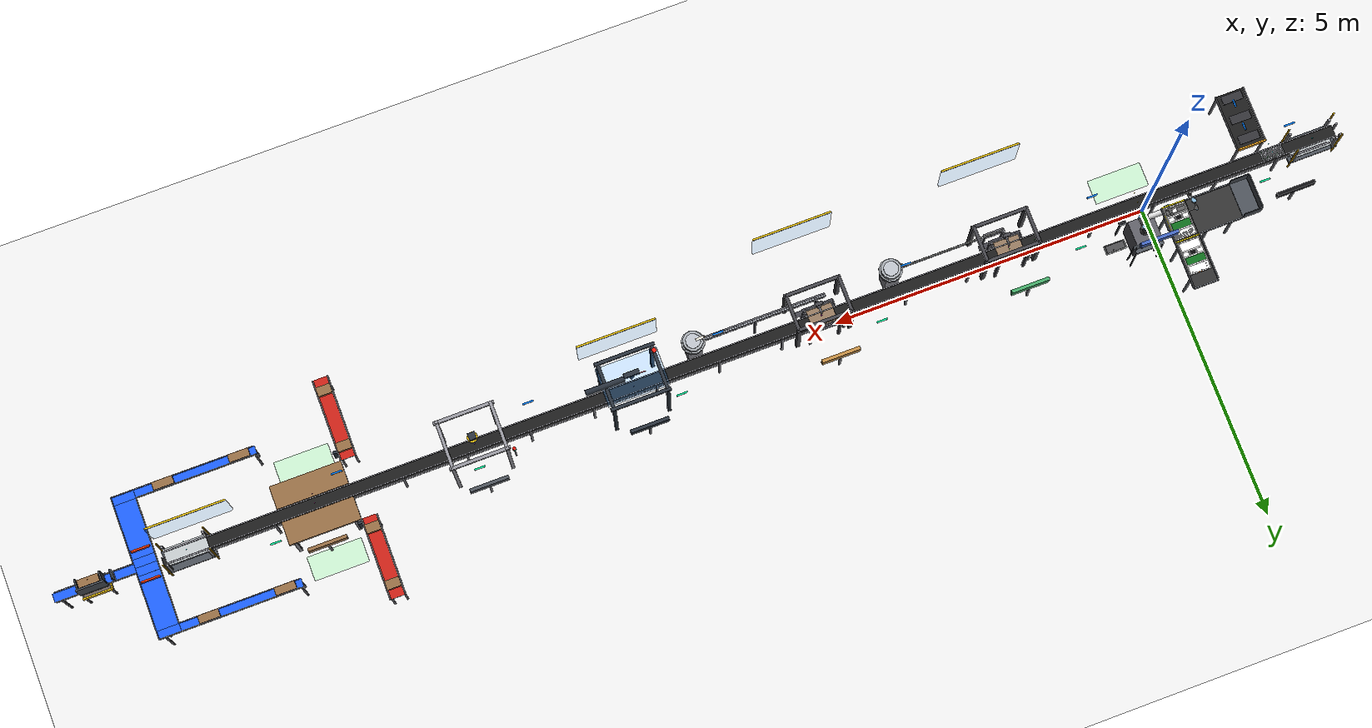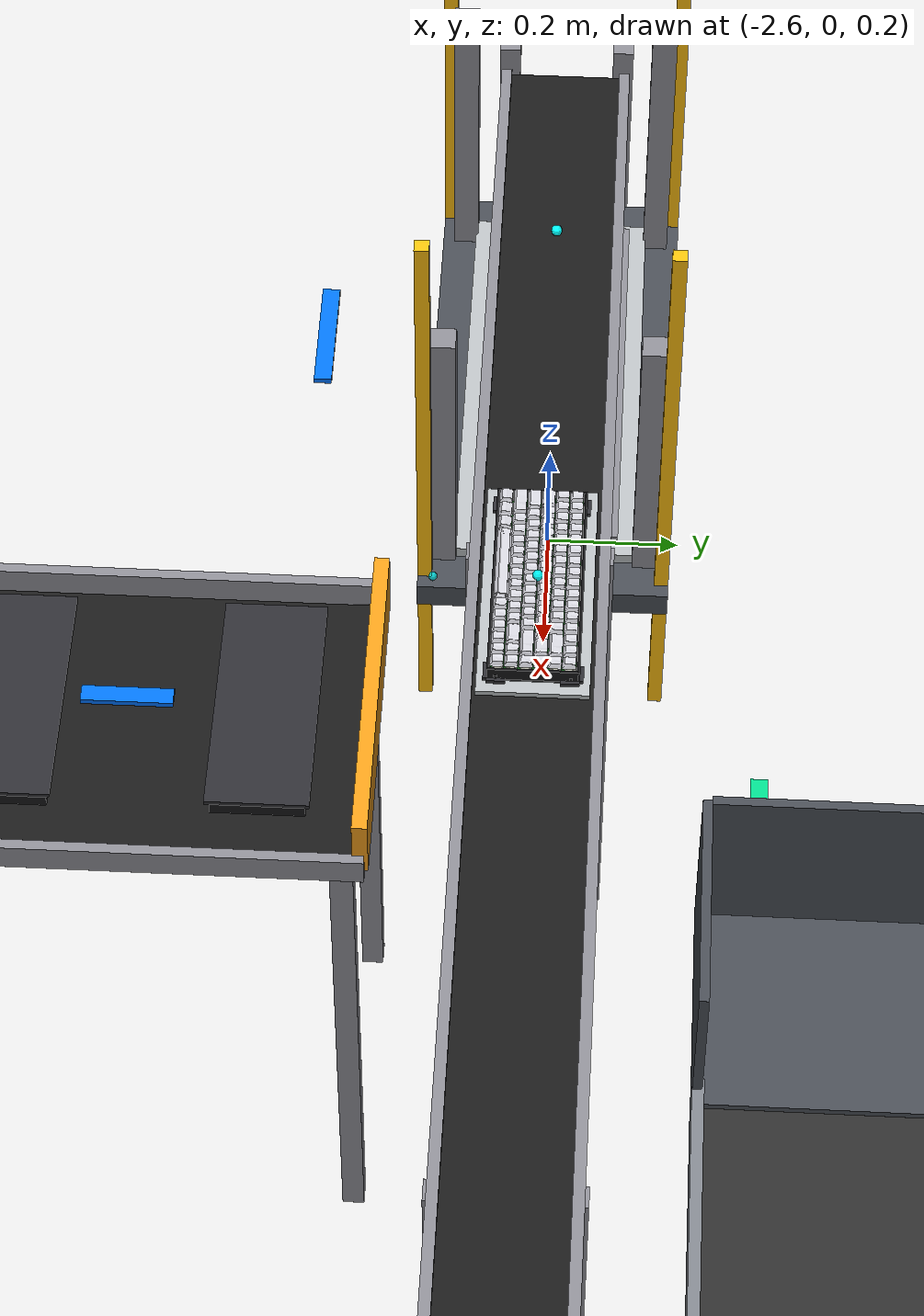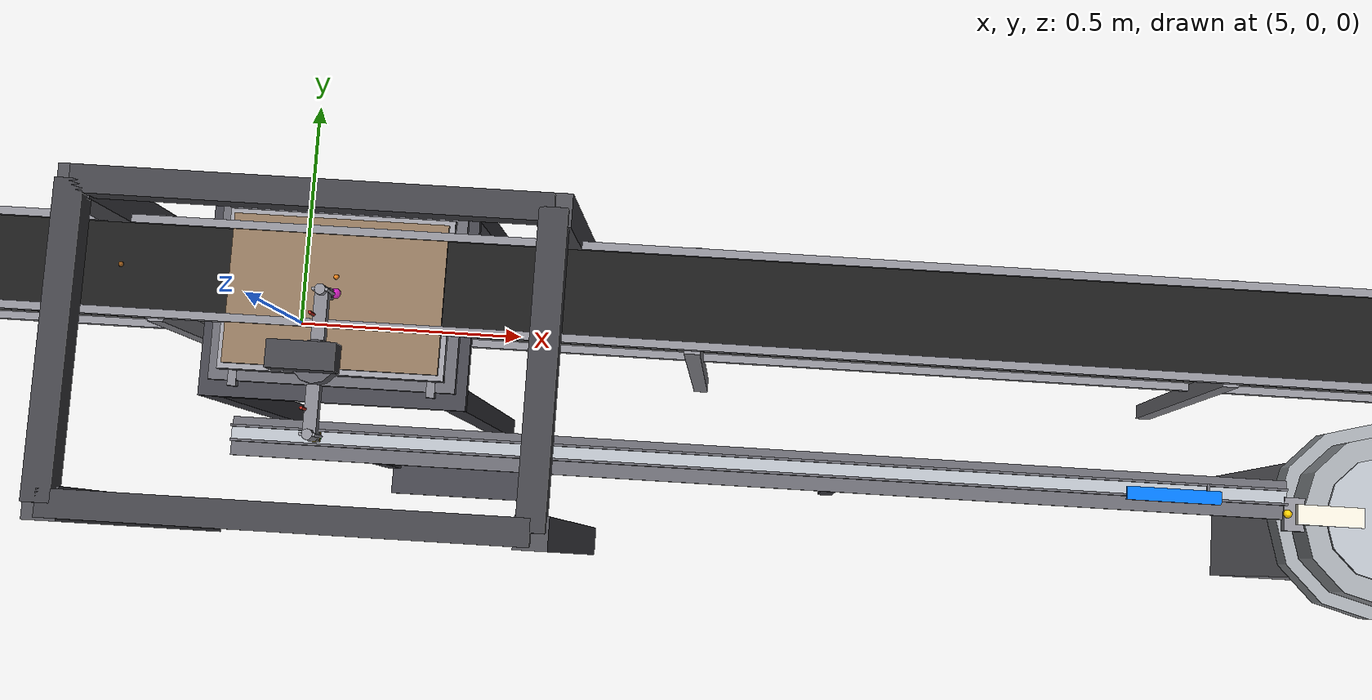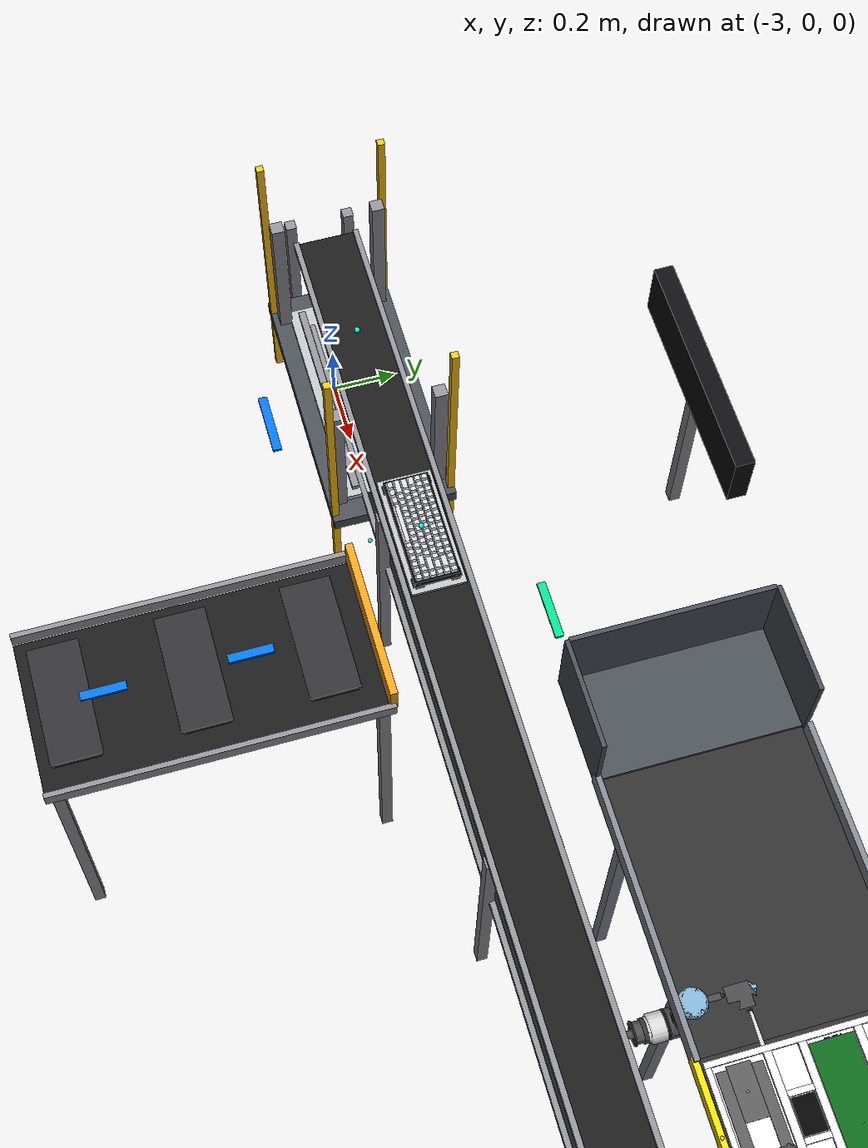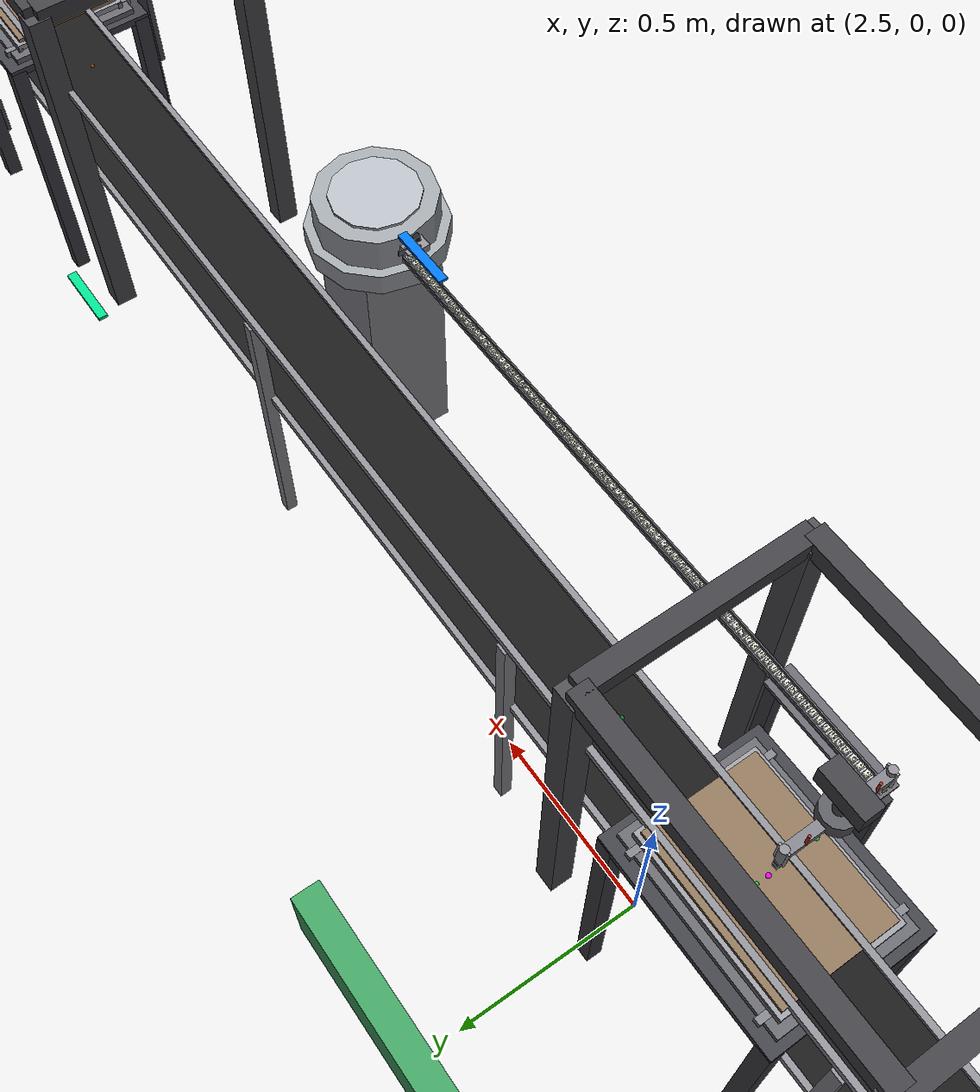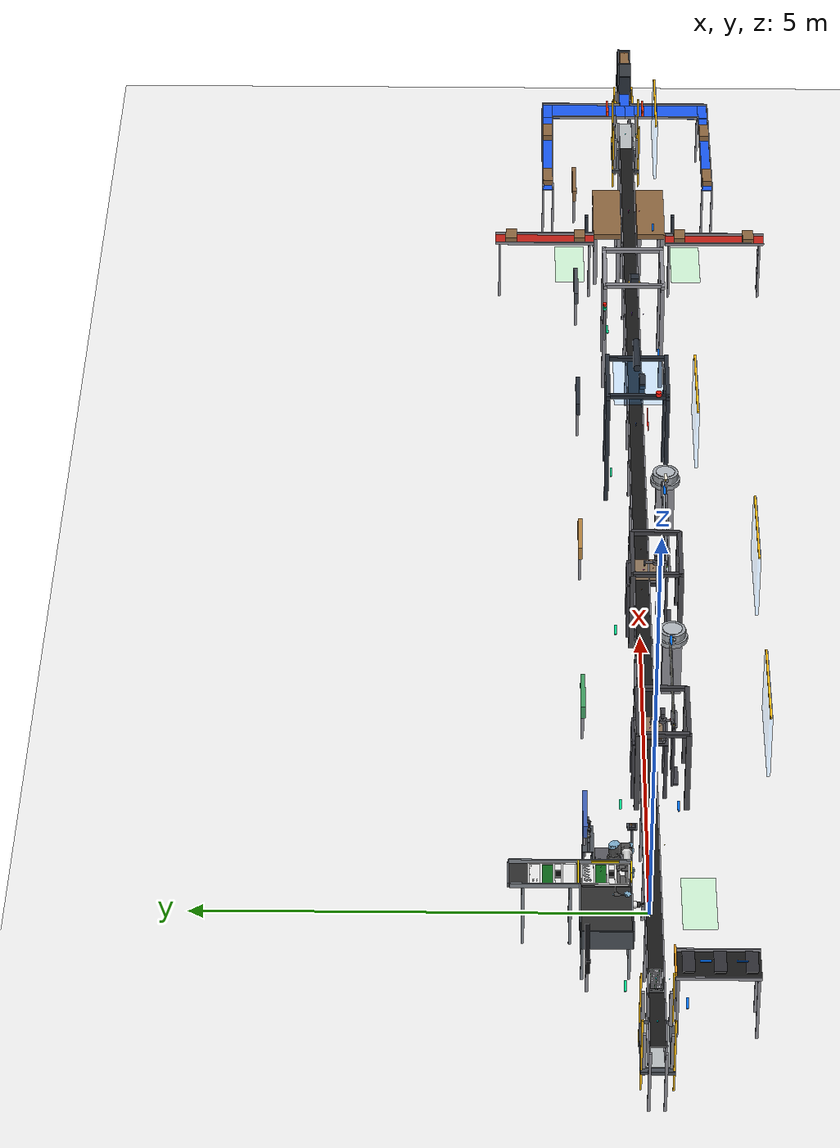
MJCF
<?xml version='1.0' encoding='UTF-8'?>
<mujoco model="assembly_cell">
  <compiler angle="radian" autolimits="true" />
  <option integrator="implicitfast" timestep="0.002" />
  <default>
    <default class="s1_ur5e">
      <material specular="0.5" shininess="0.25" />
      <joint axis="0 1 0" range="-6.28319 6.28319" armature="0.1" />
      <general gaintype="fixed" biastype="affine" ctrlrange="-6.2831 6.2831" gainprm="2000" biasprm="0 -2000 -400" forcerange="-150 150" />
      <default class="s1_size3">
        <default class="s1_size3_limited">
          <joint range="-3.1415 3.1415" />
          <general ctrlrange="-3.1415 3.1415" />
        </default>
      </default>
      <default class="s1_size1">
        <general gainprm="500" biasprm="0 -500 -100" forcerange="-28 28" />
      </default>
      <default class="s1_visual">
        <geom type="mesh" contype="0" conaffinity="0" group="2" />
      </default>
      <default class="s1_collision">
        <geom type="capsule" group="3" />
        <default class="s1_eef_collision">
          <geom type="cylinder" />
        </default>
      </default>
      <site size="0.001" rgba="0.5 0.5 0.5 0.3" group="4" />
    </default>
  </default>
  <asset>
    <texture name="grid" type="2d" builtin="checker" width="512" height="512" rgb1="0.78 0.78 0.78" rgb2="0.86 0.86 0.86" />
    <material name="floor_mat" texture="grid" texrepeat="12 12" reflectance="0.15" />
    <material name="conveyor_belt" rgba="0.10 0.10 0.10 1" />
    <material name="conveyor_rail" rgba="0.55 0.55 0.58 1" />
    <material name="stopper_mat" rgba="0.95 0.62 0.10 1" />
    <material name="aluminum_pallet" rgba="0.72 0.74 0.75 1" />
    <material name="fixture_stop" rgba="0.18 0.18 0.20 1" />
    <material name="s1_mat" rgba="0.25 0.38 0.72 1" />
    <material name="s3_mat" rgba="0.25 0.62 0.38 1" />
    <material name="s4_mat" rgba="0.72 0.52 0.25 1" />
    <material name="laser_mat" rgba="0.15 0.18 0.22 1" />
    <material name="package_mat" rgba="0.55 0.40 0.25 1" />
    <material name="abs_plastic" rgba="0.08 0.08 0.09 1" />
    <material name="mat_epdm" rgba="0.015 0.015 0.018 1" />
    <material name="mat_battery" rgba="0.08 0.18 0.10 1" />
    <material name="mat_fr4" rgba="0.04 0.36 0.12 1" />
    <material name="mat_plate" rgba="0.80 0.82 0.84 1" />
    <material name="mat_switch" rgba="0.12 0.12 0.12 1" />
    <material name="mat_keycap" rgba="0.92 0.90 0.84 1" />
    <texture type="skybox" builtin="gradient" rgb1="0.3 0.5 0.7" rgb2="0 0 0" width="512" height="3072" />
    <texture name="s1_grid" type="2d" builtin="checker" rgb1="0.3 0.3 0.3" rgb2="0.4 0.4 0.4" width="512" height="512" />
    <material name="s1_floor_mat" texture="s1_grid" texrepeat="5 5" reflectance="0.2" />
    <material name="s1_conveyor_belt" rgba="0.18 0.18 0.18 1" />
    <material name="s1_conveyor_rail" rgba="0.50 0.52 0.55 1" specular="0.4" shininess="0.3" />
    <material name="s1_stopper_mat" rgba="1.0  0.85 0.0  1" />
    <material name="s1_aluminum_pallet" rgba="0.80 0.82 0.85 1" specular="0.6" shininess="0.5" />
    <material name="s1_fixture_stop" rgba="1.0  0.75 0.0  1" />
    <material name="s1_abs_plastic" rgba="0.12 0.12 0.15 1" />
    <material name="s1_tray_alu" rgba="0.92 0.92 0.92 1" specular="0.5" shininess="0.4" />
    <material name="s1_tray_foam_epdm" rgba="0.12 0.12 0.14 1" specular="0.02" />
    <material name="s1_tray_foam_batt" rgba="0.12 0.12 0.14 1" specular="0.02" />
    <material name="s1_tray_foam_pcb" rgba="0.12 0.12 0.14 1" specular="0.02" />
    <material name="s1_tray_foam_plate" rgba="0.12 0.12 0.14 1" specular="0.02" />
    <material name="s1_tray_id" rgba="1.0  0.40 0.0  1" />
    <material name="s1_stack_mat" rgba="0.28 0.30 0.33 1" />
    <material name="s1_mat_epdm" rgba="0.35 0.35 0.35 1" specular="0.02" shininess="0.02" />
    <material name="s1_mat_lipo" rgba="0.01 0.01 0.012 1" specular="0.25" shininess="0.25" />
    <material name="s1_mat_connector" rgba="0.90 0.90 0.92 1" specular="0.9" shininess="0.8" />
    <material name="s1_mat_fr4" rgba="0.05 0.40 0.10 1" specular="0.3" shininess="0.4" />
    <material name="s1_mat_conn_dark" rgba="0.12 0.12 0.12 1" specular="0.5" shininess="0.6" />
    <material name="s1_mat_alu_silver" rgba="0.95 0.10 0.10 1" specular="0.4" shininess="0.3" />
    <material name="s1_mat_dock" rgba="0.30 0.32 0.35 1" />
    <material name="s1_mat_cup" rgba="0.55 0.55 0.58 1" />
    <material name="s1_mat_screw_box" rgba="0.25 0.25 0.28 1" />
    <material name="s1_mat_screw" rgba="0.005 0.005 0.006 1" specular="0.35" shininess="0.35" />
    <material name="s1_stab_white" rgba="0.86 0.86 0.86 1" specular="0.25" shininess="0.20" />
    <material name="s1_stab_wire" rgba="0.70 0.70 0.72 1" specular="0.7" shininess="0.7" />
    <material class="s1_ur5e" name="s1_black" rgba="0.033 0.033 0.033 1" />
    <material class="s1_ur5e" name="s1_jointgray" rgba="0.278 0.278 0.278 1" />
    <material class="s1_ur5e" name="s1_linkgray" rgba="0.82  0.82  0.82  1" />
    <material class="s1_ur5e" name="s1_urblue" rgba="0.49  0.678 0.8   1" />
    <mesh file="../robots/mujoco_menagerie/universal_robots_ur5e/assets/base_0.obj" name="s1_base_0" />
    <mesh file="../robots/mujoco_menagerie/universal_robots_ur5e/assets/base_1.obj" name="s1_base_1" />
    <mesh file="../robots/mujoco_menagerie/universal_robots_ur5e/assets/shoulder_0.obj" name="s1_shoulder_0" />
    <mesh file="../robots/mujoco_menagerie/universal_robots_ur5e/assets/shoulder_1.obj" name="s1_shoulder_1" />
    <mesh file="../robots/mujoco_menagerie/universal_robots_ur5e/assets/shoulder_2.obj" name="s1_shoulder_2" />
    <mesh file="../robots/mujoco_menagerie/universal_robots_ur5e/assets/upperarm_0.obj" name="s1_upperarm_0" />
    <mesh file="../robots/mujoco_menagerie/universal_robots_ur5e/assets/upperarm_1.obj" name="s1_upperarm_1" />
    <mesh file="../robots/mujoco_menagerie/universal_robots_ur5e/assets/upperarm_2.obj" name="s1_upperarm_2" />
    <mesh file="../robots/mujoco_menagerie/universal_robots_ur5e/assets/upperarm_3.obj" name="s1_upperarm_3" />
    <mesh file="../robots/mujoco_menagerie/universal_robots_ur5e/assets/forearm_0.obj" name="s1_forearm_0" />
    <mesh file="../robots/mujoco_menagerie/universal_robots_ur5e/assets/forearm_1.obj" name="s1_forearm_1" />
    <mesh file="../robots/mujoco_menagerie/universal_robots_ur5e/assets/forearm_2.obj" name="s1_forearm_2" />
    <mesh file="../robots/mujoco_menagerie/universal_robots_ur5e/assets/forearm_3.obj" name="s1_forearm_3" />
    <mesh file="../robots/mujoco_menagerie/universal_robots_ur5e/assets/wrist1_0.obj" name="s1_wrist1_0" />
    <mesh file="../robots/mujoco_menagerie/universal_robots_ur5e/assets/wrist1_1.obj" name="s1_wrist1_1" />
    <mesh file="../robots/mujoco_menagerie/universal_robots_ur5e/assets/wrist1_2.obj" name="s1_wrist1_2" />
    <mesh file="../robots/mujoco_menagerie/universal_robots_ur5e/assets/wrist2_0.obj" name="s1_wrist2_0" />
    <mesh file="../robots/mujoco_menagerie/universal_robots_ur5e/assets/wrist2_1.obj" name="s1_wrist2_1" />
    <mesh file="../robots/mujoco_menagerie/universal_robots_ur5e/assets/wrist2_2.obj" name="s1_wrist2_2" />
    <mesh file="../robots/mujoco_menagerie/universal_robots_ur5e/assets/wrist3.obj" name="s1_wrist3" />
    <mesh name="s1_aluminum_plate_mesh" file="../robots/mujoco_menagerie/universal_robots_ur5e/assets/aluminum_plate.stl" scale="0.001 0.001 0.001" />
    <mesh name="s1_stabilizer_mesh" file="../robots/mujoco_menagerie/universal_robots_ur5e/assets/Stabilizer_Decimated.stl" scale="0.001 0.001 0.001" refpos="-23.958 0.000 -1.712" refquat="0.7071 -0.7071 0 0" />
    <texture type="skybox" builtin="gradient" rgb1="0.3 0.5 0.7" rgb2="0 0 0" width="512" height="3072" />
    <texture name="s3_grid" type="2d" builtin="checker" rgb1="0.3 0.3 0.3" rgb2="0.4 0.4 0.4" width="512" height="512" />
    <material name="s3_floor_mat" texture="s3_grid" texrepeat="5 5" reflectance="0.2" />
    <material name="s3_aluminum_plate" rgba="0.75 0.75 0.78 1" specular="0.7" shininess="0.6" reflectance="0.20" />
    <material name="s3_fixture_stop" rgba="1.0 0.85 0.0 1" />
    <material name="s3_mat_fr4" rgba="0.06 0.30 0.08 1" specular="0.15" shininess="0.25" />
    <material name="s3_mat_epdm" rgba="0.35 0.35 0.35 1" specular="0.02" shininess="0.02" />
    <material name="s3_mat_screw" rgba="0.005 0.005 0.006 1" specular="0.35" shininess="0.35" />
    <material name="s3_stab_white" rgba="0.86 0.86 0.86 1" specular="0.25" shininess="0.20" />
    <material name="s3_stab_wire" rgba="0.70 0.70 0.72 1" specular="0.7" shininess="0.7" />
    <material name="s3_abs_plastic" rgba="0.15 0.15 0.15 1" />
    <material name="s3_table_surface" rgba="0.55 0.45 0.35 1" />
    <material name="s3_steel_dark" rgba="0.25 0.25 0.28 1" />
    <material name="s3_steel_mid" rgba="0.40 0.40 0.43 1" />
    <material name="s3_steel_light" rgba="0.60 0.60 0.63 1" />
    <material name="s3_gantry_mat" rgba="0.30 0.30 0.32 1" />
    <material name="s3_gantry_beam" rgba="0.25 0.25 0.27 1" />
    <material name="s3_column_mat" rgba="0.35 0.35 0.38 1" />
    <material name="s3_arm_mat" rgba="0.50 0.50 0.53 1" />
    <material name="s3_head_body" rgba="0.55 0.55 0.58 1" />
    <material name="s3_head_tip" rgba="0.15 0.15 0.15 1" />
    <material name="s3_tray_mat" rgba="0.70 0.72 0.75 1" />
    <material name="s3_slide_rail" rgba="0.50 0.50 0.53 1" />
    <material name="s3_abs_dark" rgba="0.88 0.88 0.82 1" specular="0.15" shininess="0.25" reflectance="0.03" />
    <material name="s3_abs_dark_collision" rgba="0.12 0.12 0.12 0.0" />
    <mesh name="s3_switch_mesh" file="../meshes/Switch_Decimated.stl" scale="0.001 0.001 0.001" refpos="-7.350 0.053 -7.350" refquat="0.7071 -0.7071 0 0" />
    <mesh name="s3_aluminum_plate_mesh" file="../meshes/aluminum_plate.stl" scale="0.001 0.001 0.001" />
    <mesh name="s3_stabilizer_mesh" file="../meshes/Stabilizer_Decimated.stl" scale="0.001 0.001 0.001" refpos="-23.958 0.000 -1.712" refquat="0.7071 -0.7071 0 0" />
    <texture type="skybox" builtin="gradient" rgb1="0.3 0.5 0.7" rgb2="0 0 0" width="512" height="3072" />
    <texture name="s4_grid" type="2d" builtin="checker" rgb1="0.3 0.3 0.3" rgb2="0.4 0.4 0.4" width="512" height="512" />
    <material name="s4_floor_mat" texture="s4_grid" texrepeat="5 5" reflectance="0.2" />
    <material name="s4_aluminum_plate" rgba="0.75 0.75 0.78 1" specular="0.7" shininess="0.6" reflectance="0.20" />
    <material name="s4_fixture_stop" rgba="1.0 0.85 0.0 1" />
    <material name="s4_mat_fr4" rgba="0.06 0.30 0.08 1" specular="0.15" shininess="0.25" />
    <material name="s4_mat_epdm" rgba="0.35 0.35 0.35 1" specular="0.02" shininess="0.02" />
    <material name="s4_mat_screw" rgba="0.005 0.005 0.006 1" specular="0.35" shininess="0.35" />
    <material name="s4_stab_white" rgba="0.86 0.86 0.86 1" specular="0.25" shininess="0.20" />
    <material name="s4_stab_wire" rgba="0.70 0.70 0.72 1" specular="0.7" shininess="0.7" />
    <material name="s4_abs_plastic" rgba="0.15 0.15 0.15 1" />
    <material name="s4_table_surface" rgba="0.55 0.45 0.35 1" />
    <material name="s4_steel_dark" rgba="0.25 0.25 0.28 1" />
    <material name="s4_steel_mid" rgba="0.40 0.40 0.43 1" />
    <material name="s4_steel_light" rgba="0.60 0.60 0.63 1" />
    <material name="s4_gantry_mat" rgba="0.30 0.30 0.32 1" />
    <material name="s4_gantry_beam" rgba="0.25 0.25 0.27 1" />
    <material name="s4_column_mat" rgba="0.35 0.35 0.38 1" />
    <material name="s4_arm_mat" rgba="0.50 0.50 0.53 1" />
    <material name="s4_head_body" rgba="0.55 0.55 0.58 1" />
    <material name="s4_head_tip" rgba="0.15 0.15 0.15 1" />
    <material name="s4_tray_mat" rgba="0.70 0.72 0.75 1" />
    <material name="s4_slide_rail" rgba="0.50 0.50 0.53 1" />
    <material name="s4_abs_dark" rgba="0.88 0.88 0.82 1" specular="0.15" shininess="0.25" reflectance="0.03" />
    <material name="s4_pbt_gray" rgba="0.82 0.82 0.85 1" specular="0.1" shininess="0.2" reflectance="0.02" />
    <mesh name="s4_switch_mesh" file="../meshes/Switch_Decimated.stl" scale="0.001 0.001 0.001" refpos="-7.350 0.053 -7.350" refquat="0.7071 -0.7071 0 0" />
    <mesh name="s4_aluminum_plate_mesh" file="../meshes/aluminum_plate.stl" scale="0.001 0.001 0.001" />
    <mesh name="s4_stabilizer_mesh" file="../meshes/Stabilizer_Decimated.stl" scale="0.001 0.001 0.001" refpos="-23.958 0.000 -1.712" refquat="0.7071 -0.7071 0 0" />
    <mesh name="s4_keycap_1u" file="../meshes/keycap_1u.stl" />
    <mesh name="s4_keycap_1_25u" file="../meshes/keycap_1_25u.stl" />
    <mesh name="s4_keycap_1_5u" file="../meshes/keycap_1_5u.stl" />
    <mesh name="s4_keycap_1_75u" file="../meshes/keycap_1_75u.stl" />
    <mesh name="s4_keycap_2u" file="../meshes/keycap_2u.stl" />
    <mesh name="s4_keycap_2_25u" file="../meshes/keycap_2_25u.stl" />
    <mesh name="s4_keycap_6_25u" file="../meshes/keycap_6_25u.stl" />
    <material name="safety_glass" rgba="0.15 0.55 0.95 0.22" />
    <material name="warning_yellow" rgba="1.0 0.75 0.05 1" />
    <material name="flow_arrow_mat" rgba="0.0 0.45 1.0 1" />
    <material name="return_arrow_mat" rgba="0.0 0.85 0.55 1" />
    <material name="operator_zone_mat" rgba="0.1 0.8 0.25 0.30" />
    <material name="label_board_mat" rgba="0.05 0.05 0.06 1" />
    <material name="bowl_feeder_mat" rgba="0.62 0.64 0.66 1" />
    <material name="box_conv_mat" rgba="0.75 0.12 0.08 1" />
    <material name="packed_conv_mat" rgba="0.10 0.35 0.95 1" />
    <material name="human_zone_mat" rgba="0.15 0.8 0.25 0.22" />
    <material name="laser_warning_mat" rgba="1 0.1 0.05 1" />
    <material name="traffic_stopper_red" rgba="1.0 0.18 0.02 1" />

    <!-- PASS 3A OVERVIEW MATERIALS START -->
    <material name="p3a_pallet_mat" rgba="0.72 0.74 0.76 1" specular="0.35" shininess="0.25" />
    <material name="p3a_fixture_mat" rgba="0.18 0.18 0.20 1" />
    <!-- PASS 3A OVERVIEW MATERIALS END -->
  </asset>
  <worldbody>
    <light name="key_light" pos="3 -5 6" dir="-0.4 0.6 -1" directional="true" diffuse="0.8 0.8 0.8" />
    <light name="fill_light" pos="9 4 5" dir="-0.3 -0.4 -1" directional="true" diffuse="0.35 0.35 0.35" />
    <geom name="floor" type="plane" size="18 7 0.05" material="floor_mat" />
    <body name="cell_cdlr" pos="6.290 0 0">
      <geom name="cdlr_belt" type="box" size="9.290 0.080 0.005" pos="0 0 0.795" material="conveyor_belt" contype="1" conaffinity="1" />
      <geom name="cdlr_rail_front" type="box" size="9.290 0.0075 0.010" pos="0 -0.0875 0.8" material="conveyor_rail" contype="1" conaffinity="1" />
      <geom name="cdlr_rail_rear" type="box" size="9.290 0.0075 0.010" pos="0 0.0875 0.8" material="conveyor_rail" contype="1" conaffinity="1" />
      <geom name="leg_00_f" type="box" size="0.015 0.015 0.392" pos="-9.375 -0.085 0.392" material="conveyor_rail" />
      <geom name="leg_00_r" type="box" size="0.015 0.015 0.392" pos="-9.375 0.085 0.392" material="conveyor_rail" />
      <geom name="leg_01_f" type="box" size="0.015 0.015 0.392" pos="-8.375 -0.085 0.392" material="conveyor_rail" />
      <geom name="leg_01_r" type="box" size="0.015 0.015 0.392" pos="-8.375 0.085 0.392" material="conveyor_rail" />
      <geom name="leg_02_f" type="box" size="0.015 0.015 0.392" pos="-7.375 -0.085 0.392" material="conveyor_rail" />
      <geom name="leg_02_r" type="box" size="0.015 0.015 0.392" pos="-7.375 0.085 0.392" material="conveyor_rail" />
      <geom name="leg_03_f" type="box" size="0.015 0.015 0.392" pos="-6.375 -0.085 0.392" material="conveyor_rail" />
      <geom name="leg_03_r" type="box" size="0.015 0.015 0.392" pos="-6.375 0.085 0.392" material="conveyor_rail" />
      <geom name="leg_04_f" type="box" size="0.015 0.015 0.392" pos="-5.375 -0.085 0.392" material="conveyor_rail" />
      <geom name="leg_04_r" type="box" size="0.015 0.015 0.392" pos="-5.375 0.085 0.392" material="conveyor_rail" />
      <geom name="leg_05_f" type="box" size="0.015 0.015 0.392" pos="-4.375 -0.085 0.392" material="conveyor_rail" />
      <geom name="leg_05_r" type="box" size="0.015 0.015 0.392" pos="-4.375 0.085 0.392" material="conveyor_rail" />
      <geom name="leg_06_f" type="box" size="0.015 0.015 0.392" pos="-3.375 -0.085 0.392" material="conveyor_rail" />
      <geom name="leg_06_r" type="box" size="0.015 0.015 0.392" pos="-3.375 0.085 0.392" material="conveyor_rail" />
      <geom name="leg_07_f" type="box" size="0.015 0.015 0.392" pos="-2.375 -0.085 0.392" material="conveyor_rail" />
      <geom name="leg_07_r" type="box" size="0.015 0.015 0.392" pos="-2.375 0.085 0.392" material="conveyor_rail" />
      <geom name="leg_08_f" type="box" size="0.015 0.015 0.392" pos="-1.375 -0.085 0.392" material="conveyor_rail" />
      <geom name="leg_08_r" type="box" size="0.015 0.015 0.392" pos="-1.375 0.085 0.392" material="conveyor_rail" />
      <geom name="leg_09_f" type="box" size="0.015 0.015 0.392" pos="-0.375 -0.085 0.392" material="conveyor_rail" />
      <geom name="leg_09_r" type="box" size="0.015 0.015 0.392" pos="-0.375 0.085 0.392" material="conveyor_rail" />
      <geom name="leg_10_f" type="box" size="0.015 0.015 0.392" pos="0.625 -0.085 0.392" material="conveyor_rail" />
      <geom name="leg_10_r" type="box" size="0.015 0.015 0.392" pos="0.625 0.085 0.392" material="conveyor_rail" />
      <geom name="leg_11_f" type="box" size="0.015 0.015 0.392" pos="1.625 -0.085 0.392" material="conveyor_rail" />
      <geom name="leg_11_r" type="box" size="0.015 0.015 0.392" pos="1.625 0.085 0.392" material="conveyor_rail" />
      <geom name="leg_12_f" type="box" size="0.015 0.015 0.392" pos="2.625 -0.085 0.392" material="conveyor_rail" />
      <geom name="leg_12_r" type="box" size="0.015 0.015 0.392" pos="2.625 0.085 0.392" material="conveyor_rail" />
      <geom name="leg_13_f" type="box" size="0.015 0.015 0.392" pos="3.625 -0.085 0.392" material="conveyor_rail" />
      <geom name="leg_13_r" type="box" size="0.015 0.015 0.392" pos="3.625 0.085 0.392" material="conveyor_rail" />
      <geom name="leg_14_f" type="box" size="0.015 0.015 0.392" pos="4.625 -0.085 0.392" material="conveyor_rail" />
      <geom name="leg_14_r" type="box" size="0.015 0.015 0.392" pos="4.625 0.085 0.392" material="conveyor_rail" />
      <geom name="leg_15_f" type="box" size="0.015 0.015 0.392" pos="5.625 -0.085 0.392" material="conveyor_rail" />
      <geom name="leg_15_r" type="box" size="0.015 0.015 0.392" pos="5.625 0.085 0.392" material="conveyor_rail" />
      <geom name="leg_16_f" type="box" size="0.015 0.015 0.392" pos="6.625 -0.085 0.392" material="conveyor_rail" />
      <geom name="leg_16_r" type="box" size="0.015 0.015 0.392" pos="6.625 0.085 0.392" material="conveyor_rail" />
      <geom name="leg_17_f" type="box" size="0.015 0.015 0.392" pos="7.625 -0.085 0.392" material="conveyor_rail" />
      <geom name="leg_17_r" type="box" size="0.015 0.015 0.392" pos="7.625 0.085 0.392" material="conveyor_rail" />
      <geom name="leg_18_f" type="box" size="0.015 0.015 0.392" pos="8.625 -0.085 0.392" material="conveyor_rail" />
      <geom name="leg_18_r" type="box" size="0.015 0.015 0.392" pos="8.625 0.085 0.392" material="conveyor_rail" />
    </body>
    <body name="cell_return_cdlr" pos="6.375 0 0">
      <geom name="return_cdlr_belt" type="box" size="9.290 0.065 0.005" pos="0 0 0.495" material="conveyor_belt" contype="1" conaffinity="1" />
      <geom name="return_cdlr_rail_front" type="box" size="9.290 0.0075 0.010" pos="0 -0.0750 0.500" material="conveyor_rail" contype="1" conaffinity="1" />
      <geom name="return_cdlr_rail_rear" type="box" size="9.290 0.0075 0.010" pos="0  0.0750 0.500" material="conveyor_rail" contype="1" conaffinity="1" />
      <geom name="return_arrow_01" type="box" size="0.160 0.012 0.006" pos="6.800 0 0.515" material="fixture_stop" contype="0" conaffinity="0" />
      <geom name="return_arrow_02" type="box" size="0.160 0.012 0.006" pos="2.800 0 0.515" material="fixture_stop" contype="0" conaffinity="0" />
      <geom name="return_arrow_03" type="box" size="0.160 0.012 0.006" pos="-1.200 0 0.515" material="fixture_stop" contype="0" conaffinity="0" />
      <site name="lower_return_track_site" type="sphere" size="0.007" pos="0 0 0.530" rgba="0.0 0.6 1.0 0.8" />
    </body>
    <body name="start_vtu" pos="-2.6500 0.0000 0.0000">
      <geom name="start_vtu_frame_base" type="box" size="0.390 0.180 0.020" pos="0 0 0.470" material="s1_stack_mat" contype="0" conaffinity="0" />
      <geom name="start_vtu_post_fl" type="box" size="0.018 0.018 0.270" pos="-0.320 -0.145 0.670" material="conveyor_rail" contype="0" conaffinity="0" />
      <geom name="start_vtu_post_fr" type="box" size="0.018 0.018 0.270" pos=" 0.320 -0.145 0.670" material="conveyor_rail" contype="0" conaffinity="0" />
      <geom name="start_vtu_post_rl" type="box" size="0.018 0.018 0.270" pos="-0.320  0.145 0.670" material="conveyor_rail" contype="0" conaffinity="0" />
      <geom name="start_vtu_post_rr" type="box" size="0.018 0.018 0.270" pos=" 0.320  0.145 0.670" material="conveyor_rail" contype="0" conaffinity="0" />
      <body name="start_vtu_platform" pos="0 0 0.495">
        <joint name="start_vtu_slide_z" type="slide" axis="0 0 1" limited="true" range="0.000 0.300" damping="20" />
        <geom name="start_vtu_platform_plate" type="box" size="0.330 0.130 0.012" pos="0 0 0" material="aluminum_pallet" contype="1" conaffinity="1" mass="4.0" />
        <geom name="start_vtu_platform_roller_f" type="box" size="0.310 0.010 0.010" pos="0 -0.095 0.018" material="conveyor_rail" contype="0" conaffinity="0" />
        <geom name="start_vtu_platform_roller_r" type="box" size="0.310 0.010 0.010" pos="0  0.095 0.018" material="conveyor_rail" contype="0" conaffinity="0" />
        <site name="start_vtu_platform_site" type="sphere" size="0.008" pos="0 0 0.035" rgba="0.0 1.0 1.0 0.9" />
      </body>
      <site name="start_vtu_upper_site" type="sphere" size="0.008" pos="0 0 0.830" rgba="0.0 1.0 1.0 0.9" />
    </body>
    <site name="s0_stop" type="sphere" size="0.006" pos="-2.0000 -0.1400 0.8300" rgba="0.0 0.9 0.9 0.8" />
    <site name="s1_stop" type="sphere" size="0.006" pos="0.185 -0.140 0.830" rgba="1 0.85 0 0.8" />
    <site name="s3_stop" type="sphere" size="0.006" pos="2.25 -0.140 0.830" rgba="0.1 0.9 0.25 0.8" />
    <site name="s4_stop" type="sphere" size="0.006" pos="5.2500 -0.1400 0.8300" rgba="1 0.55 0.1 0.8" />
    <site name="s5_stop" type="sphere" size="0.006" pos="8.2500 -0.1400 0.8300" rgba="0.2 0.45 1 0.8" />
    <site name="s6_stop" type="sphere" size="0.006" pos="10.7500 -0.1400 0.8300" rgba="0.6 0.25 1 0.8" />
    <site name="s7_stop" type="sphere" size="0.006" pos="13.2500 -0.1400 0.8300" rgba="0.95 0.20 0.75 0.8" />
    <site name="cell_pallet_s1_stop_site" type="sphere" size="0.005" pos="0.185 0.000 0.810" rgba="1 0.85 0 0.75" />
    <site name="cell_pallet_s3_buffer_site" type="sphere" size="0.005" pos="1.850 0.000 0.810" rgba="0.1 0.9 0.25 0.55" />
    <site name="cell_pallet_s3_station_site" type="sphere" size="0.005" pos="2.250 0.000 0.810" rgba="0.1 0.9 0.25 0.85" />
    <site name="cell_pallet_s3_exit_site" type="sphere" size="0.005" pos="2.650 0.000 0.810" rgba="0.1 0.9 0.25 0.55" />
    <site name="cell_pallet_s4_buffer_site" type="sphere" size="0.005" pos="4.850 0.000 0.810" rgba="1 0.55 0.1 0.55" />
    <site name="cell_pallet_s4_station_site" type="sphere" size="0.005" pos="5.250 0.000 0.810" rgba="1 0.55 0.1 0.85" />
    <site name="cell_pallet_s4_exit_site" type="sphere" size="0.005" pos="5.650 0.000 0.810" rgba="1 0.55 0.1 0.55" />

    <!-- PASS 3A OVERVIEW PATH SITES START -->
    <site name="cell_pallet_s0_load_site" type="sphere" size="0.005" pos="-2.000 0.000 0.810" rgba="0.0 0.9 0.9 0.55" />
    <site name="cell_pallet_s5_station_site" type="sphere" size="0.005" pos="8.250 0.000 0.810" rgba="0.2 0.45 1 0.55" />
    <site name="cell_pallet_s6_station_site" type="sphere" size="0.005" pos="10.750 0.000 0.810" rgba="0.6 0.25 1 0.55" />
    <site name="cell_pallet_s7_exit_site" type="sphere" size="0.005" pos="13.250 0.000 0.810" rgba="0.95 0.20 0.75 0.55" />
    <!-- PASS 3A OVERVIEW PATH SITES END -->
    <site name="end_vtu_entry" type="sphere" size="0.006" pos="15.2500 -0.1400 0.8300" rgba="0.05 0.95 0.95 0.8" />
    <body name="s4_kc_End2" pos="6.8312 -0.3000 0.8261" quat="0 0 0 1">
      <freejoint />
      <inertial pos="0 0 0.0036" mass="0.003" diaginertia="1e-7 1e-7 1e-7" />
      <geom name="s4_kc_End2_geom" type="mesh" mesh="s4_keycap_1u" material="s4_pbt_gray" contype="0" conaffinity="0" />
    </body>
    <body name="s4_kc_Right" pos="6.8121 -0.3000 0.8261" quat="0 0 0 1">
      <freejoint />
      <inertial pos="0 0 0.0036" mass="0.003" diaginertia="1e-7 1e-7 1e-7" />
      <geom name="s4_kc_Right_geom" type="mesh" mesh="s4_keycap_1u" material="s4_pbt_gray" contype="0" conaffinity="0" />
    </body>
    <body name="s4_kc_Down" pos="6.7931 -0.3000 0.8261" quat="0 0 0 1">
      <freejoint />
      <inertial pos="0 0 0.0036" mass="0.003" diaginertia="1e-7 1e-7 1e-7" />
      <geom name="s4_kc_Down_geom" type="mesh" mesh="s4_keycap_1u" material="s4_pbt_gray" contype="0" conaffinity="0" />
    </body>
    <body name="s4_kc_Left" pos="6.7740 -0.3000 0.8261" quat="0 0 0 1">
      <freejoint />
      <inertial pos="0 0 0.0036" mass="0.003" diaginertia="1e-7 1e-7 1e-7" />
      <geom name="s4_kc_Left_geom" type="mesh" mesh="s4_keycap_1u" material="s4_pbt_gray" contype="0" conaffinity="0" />
    </body>
    <body name="s4_kc_Fn" pos="6.7550 -0.3000 0.8261" quat="0 0 0 1">
      <freejoint />
      <inertial pos="0 0 0.0036" mass="0.003" diaginertia="1e-7 1e-7 1e-7" />
      <geom name="s4_kc_Fn_geom" type="mesh" mesh="s4_keycap_1u" material="s4_pbt_gray" contype="0" conaffinity="0" />
    </body>
    <body name="s4_kc_RAlt" pos="6.7359 -0.3000 0.8261" quat="0 0 0 1">
      <freejoint />
      <inertial pos="0 0 0.0036" mass="0.003" diaginertia="1e-7 1e-7 1e-7" />
      <geom name="s4_kc_RAlt_geom" type="mesh" mesh="s4_keycap_1u" material="s4_pbt_gray" contype="0" conaffinity="0" />
    </body>
    <body name="s4_kc_Space" pos="6.7168 -0.3000 0.8261" quat="0 0 0 1">
      <freejoint />
      <inertial pos="0 0 0.0036" mass="0.003" diaginertia="1e-7 1e-7 1e-7" />
      <geom name="s4_kc_Space_geom" type="mesh" mesh="s4_keycap_6_25u" pos="0 -0.00047 0" material="s4_pbt_gray" contype="0" conaffinity="0" />
    </body>
    <body name="s4_kc_LAlt" pos="6.6978 -0.3000 0.8261" quat="0 0 0 1">
      <freejoint />
      <inertial pos="0 0 0.0036" mass="0.003" diaginertia="1e-7 1e-7 1e-7" />
      <geom name="s4_kc_LAlt_geom" type="mesh" mesh="s4_keycap_1_25u" pos="0 -0.00015 0" material="s4_pbt_gray" contype="0" conaffinity="0" />
    </body>
    <body name="s4_kc_LWin" pos="6.6787 -0.3000 0.8261" quat="0 0 0 1">
      <freejoint />
      <inertial pos="0 0 0.0036" mass="0.003" diaginertia="1e-7 1e-7 1e-7" />
      <geom name="s4_kc_LWin_geom" type="mesh" mesh="s4_keycap_1_25u" pos="0 -0.00015 0" material="s4_pbt_gray" contype="0" conaffinity="0" />
    </body>
    <body name="s4_kc_LCtrl" pos="6.6597 -0.3000 0.8261" quat="0 0 0 1">
      <freejoint />
      <inertial pos="0 0 0.0036" mass="0.003" diaginertia="1e-7 1e-7 1e-7" />
      <geom name="s4_kc_LCtrl_geom" type="mesh" mesh="s4_keycap_1_25u" pos="0 -0.00015 0" material="s4_pbt_gray" contype="0" conaffinity="0" />
    </body>
    <body name="s4_kc_End" pos="6.6407 -0.3000 0.8261" quat="0 0 0 1">
      <freejoint />
      <inertial pos="0 0 0.0036" mass="0.003" diaginertia="1e-7 1e-7 1e-7" />
      <geom name="s4_kc_End_geom" type="mesh" mesh="s4_keycap_1u" material="s4_pbt_gray" contype="0" conaffinity="0" />
    </body>
    <body name="s4_kc_Up" pos="6.6216 -0.3000 0.8261" quat="0 0 0 1">
      <freejoint />
      <inertial pos="0 0 0.0036" mass="0.003" diaginertia="1e-7 1e-7 1e-7" />
      <geom name="s4_kc_Up_geom" type="mesh" mesh="s4_keycap_1u" material="s4_pbt_gray" contype="0" conaffinity="0" />
    </body>
    <body name="s4_kc_RShift" pos="6.6026 -0.3000 0.8261" quat="0 0 0 1">
      <freejoint />
      <inertial pos="0 0 0.0036" mass="0.003" diaginertia="1e-7 1e-7 1e-7" />
      <geom name="s4_kc_RShift_geom" type="mesh" mesh="s4_keycap_1_75u" pos="0 0.00100 0" material="s4_pbt_gray" contype="0" conaffinity="0" />
    </body>
    <body name="s4_kc_Slash" pos="6.5835 -0.3000 0.8261" quat="0 0 0 1">
      <freejoint />
      <inertial pos="0 0 0.0036" mass="0.003" diaginertia="1e-7 1e-7 1e-7" />
      <geom name="s4_kc_Slash_geom" type="mesh" mesh="s4_keycap_1u" material="s4_pbt_gray" contype="0" conaffinity="0" />
    </body>
    <body name="s4_kc_Period" pos="6.5645 -0.3000 0.8261" quat="0 0 0 1">
      <freejoint />
      <inertial pos="0 0 0.0036" mass="0.003" diaginertia="1e-7 1e-7 1e-7" />
      <geom name="s4_kc_Period_geom" type="mesh" mesh="s4_keycap_1u" material="s4_pbt_gray" contype="0" conaffinity="0" />
    </body>
    <body name="s4_kc_Comma" pos="6.5454 -0.3000 0.8261" quat="0 0 0 1">
      <freejoint />
      <inertial pos="0 0 0.0036" mass="0.003" diaginertia="1e-7 1e-7 1e-7" />
      <geom name="s4_kc_Comma_geom" type="mesh" mesh="s4_keycap_1u" material="s4_pbt_gray" contype="0" conaffinity="0" />
    </body>
    <body name="s4_kc_M" pos="6.5264 -0.3000 0.8261" quat="0 0 0 1">
      <freejoint />
      <inertial pos="0 0 0.0036" mass="0.003" diaginertia="1e-7 1e-7 1e-7" />
      <geom name="s4_kc_M_geom" type="mesh" mesh="s4_keycap_1u" material="s4_pbt_gray" contype="0" conaffinity="0" />
    </body>
    <body name="s4_kc_N" pos="6.5073 -0.3000 0.8261" quat="0 0 0 1">
      <freejoint />
      <inertial pos="0 0 0.0036" mass="0.003" diaginertia="1e-7 1e-7 1e-7" />
      <geom name="s4_kc_N_geom" type="mesh" mesh="s4_keycap_1u" material="s4_pbt_gray" contype="0" conaffinity="0" />
    </body>
    <body name="s4_kc_B" pos="6.4883 -0.3000 0.8261" quat="0 0 0 1">
      <freejoint />
      <inertial pos="0 0 0.0036" mass="0.003" diaginertia="1e-7 1e-7 1e-7" />
      <geom name="s4_kc_B_geom" type="mesh" mesh="s4_keycap_1u" material="s4_pbt_gray" contype="0" conaffinity="0" />
    </body>
    <body name="s4_kc_V" pos="6.4692 -0.3000 0.8261" quat="0 0 0 1">
      <freejoint />
      <inertial pos="0 0 0.0036" mass="0.003" diaginertia="1e-7 1e-7 1e-7" />
      <geom name="s4_kc_V_geom" type="mesh" mesh="s4_keycap_1u" material="s4_pbt_gray" contype="0" conaffinity="0" />
    </body>
    <body name="s4_kc_C" pos="6.4502 -0.3000 0.8261" quat="0 0 0 1">
      <freejoint />
      <inertial pos="0 0 0.0036" mass="0.003" diaginertia="1e-7 1e-7 1e-7" />
      <geom name="s4_kc_C_geom" type="mesh" mesh="s4_keycap_1u" material="s4_pbt_gray" contype="0" conaffinity="0" />
    </body>
    <body name="s4_kc_X" pos="6.4311 -0.3000 0.8261" quat="0 0 0 1">
      <freejoint />
      <inertial pos="0 0 0.0036" mass="0.003" diaginertia="1e-7 1e-7 1e-7" />
      <geom name="s4_kc_X_geom" type="mesh" mesh="s4_keycap_1u" material="s4_pbt_gray" contype="0" conaffinity="0" />
    </body>
    <body name="s4_kc_Z" pos="6.4121 -0.3000 0.8261" quat="0 0 0 1">
      <freejoint />
      <inertial pos="0 0 0.0036" mass="0.003" diaginertia="1e-7 1e-7 1e-7" />
      <geom name="s4_kc_Z_geom" type="mesh" mesh="s4_keycap_1u" material="s4_pbt_gray" contype="0" conaffinity="0" />
    </body>
    <body name="s4_kc_LShift" pos="6.3930 -0.3000 0.8261" quat="0 0 0 1">
      <freejoint />
      <inertial pos="0 0 0.0036" mass="0.003" diaginertia="1e-7 1e-7 1e-7" />
      <geom name="s4_kc_LShift_geom" type="mesh" mesh="s4_keycap_2_25u" pos="0 0.00100 0" material="s4_pbt_gray" contype="0" conaffinity="0" />
    </body>
    <body name="s4_kc_Home" pos="6.3740 -0.3000 0.8261" quat="0 0 0 1">
      <freejoint />
      <inertial pos="0 0 0.0036" mass="0.003" diaginertia="1e-7 1e-7 1e-7" />
      <geom name="s4_kc_Home_geom" type="mesh" mesh="s4_keycap_1u" material="s4_pbt_gray" contype="0" conaffinity="0" />
    </body>
    <body name="s4_kc_Enter" pos="6.3549 -0.3000 0.8261" quat="0 0 0 1">
      <freejoint />
      <inertial pos="0 0 0.0036" mass="0.003" diaginertia="1e-7 1e-7 1e-7" />
      <geom name="s4_kc_Enter_geom" type="mesh" mesh="s4_keycap_2_25u" pos="0 0.00100 0" material="s4_pbt_gray" contype="0" conaffinity="0" />
    </body>
    <body name="s4_kc_Quote" pos="6.3358 -0.3000 0.8261" quat="0 0 0 1">
      <freejoint />
      <inertial pos="0 0 0.0036" mass="0.003" diaginertia="1e-7 1e-7 1e-7" />
      <geom name="s4_kc_Quote_geom" type="mesh" mesh="s4_keycap_1u" material="s4_pbt_gray" contype="0" conaffinity="0" />
    </body>
    <body name="s4_kc_Semicol" pos="6.3168 -0.3000 0.8261" quat="0 0 0 1">
      <freejoint />
      <inertial pos="0 0 0.0036" mass="0.003" diaginertia="1e-7 1e-7 1e-7" />
      <geom name="s4_kc_Semicol_geom" type="mesh" mesh="s4_keycap_1u" material="s4_pbt_gray" contype="0" conaffinity="0" />
    </body>
    <body name="s4_kc_L" pos="6.2977 -0.3000 0.8261" quat="0 0 0 1">
      <freejoint />
      <inertial pos="0 0 0.0036" mass="0.003" diaginertia="1e-7 1e-7 1e-7" />
      <geom name="s4_kc_L_geom" type="mesh" mesh="s4_keycap_1u" material="s4_pbt_gray" contype="0" conaffinity="0" />
    </body>
    <body name="s4_kc_K" pos="6.2787 -0.3000 0.8261" quat="0 0 0 1">
      <freejoint />
      <inertial pos="0 0 0.0036" mass="0.003" diaginertia="1e-7 1e-7 1e-7" />
      <geom name="s4_kc_K_geom" type="mesh" mesh="s4_keycap_1u" material="s4_pbt_gray" contype="0" conaffinity="0" />
    </body>
    <body name="s4_kc_J" pos="6.2597 -0.3000 0.8261" quat="0 0 0 1">
      <freejoint />
      <inertial pos="0 0 0.0036" mass="0.003" diaginertia="1e-7 1e-7 1e-7" />
      <geom name="s4_kc_J_geom" type="mesh" mesh="s4_keycap_1u" material="s4_pbt_gray" contype="0" conaffinity="0" />
    </body>
    <body name="s4_kc_H" pos="6.2406 -0.3000 0.8261" quat="0 0 0 1">
      <freejoint />
      <inertial pos="0 0 0.0036" mass="0.003" diaginertia="1e-7 1e-7 1e-7" />
      <geom name="s4_kc_H_geom" type="mesh" mesh="s4_keycap_1u" material="s4_pbt_gray" contype="0" conaffinity="0" />
    </body>
    <body name="s4_kc_G" pos="6.2216 -0.3000 0.8261" quat="0 0 0 1">
      <freejoint />
      <inertial pos="0 0 0.0036" mass="0.003" diaginertia="1e-7 1e-7 1e-7" />
      <geom name="s4_kc_G_geom" type="mesh" mesh="s4_keycap_1u" material="s4_pbt_gray" contype="0" conaffinity="0" />
    </body>
    <body name="s4_kc_F" pos="6.2025 -0.3000 0.8261" quat="0 0 0 1">
      <freejoint />
      <inertial pos="0 0 0.0036" mass="0.003" diaginertia="1e-7 1e-7 1e-7" />
      <geom name="s4_kc_F_geom" type="mesh" mesh="s4_keycap_1u" material="s4_pbt_gray" contype="0" conaffinity="0" />
    </body>
    <body name="s4_kc_D" pos="6.1835 -0.3000 0.8261" quat="0 0 0 1">
      <freejoint />
      <inertial pos="0 0 0.0036" mass="0.003" diaginertia="1e-7 1e-7 1e-7" />
      <geom name="s4_kc_D_geom" type="mesh" mesh="s4_keycap_1u" material="s4_pbt_gray" contype="0" conaffinity="0" />
    </body>
    <body name="s4_kc_S" pos="6.1644 -0.3000 0.8261" quat="0 0 0 1">
      <freejoint />
      <inertial pos="0 0 0.0036" mass="0.003" diaginertia="1e-7 1e-7 1e-7" />
      <geom name="s4_kc_S_geom" type="mesh" mesh="s4_keycap_1u" material="s4_pbt_gray" contype="0" conaffinity="0" />
    </body>
    <body name="s4_kc_A" pos="6.1454 -0.3000 0.8261" quat="0 0 0 1">
      <freejoint />
      <inertial pos="0 0 0.0036" mass="0.003" diaginertia="1e-7 1e-7 1e-7" />
      <geom name="s4_kc_A_geom" type="mesh" mesh="s4_keycap_1u" material="s4_pbt_gray" contype="0" conaffinity="0" />
    </body>
    <body name="s4_kc_Caps" pos="6.1263 -0.3000 0.8261" quat="0 0 0 1">
      <freejoint />
      <inertial pos="0 0 0.0036" mass="0.003" diaginertia="1e-7 1e-7 1e-7" />
      <geom name="s4_kc_Caps_geom" type="mesh" mesh="s4_keycap_1_75u" pos="0 0.00100 0" material="s4_pbt_gray" contype="0" conaffinity="0" />
    </body>
    <body name="s4_kc_PgDn" pos="6.1073 -0.3000 0.8261" quat="0 0 0 1">
      <freejoint />
      <inertial pos="0 0 0.0036" mass="0.003" diaginertia="1e-7 1e-7 1e-7" />
      <geom name="s4_kc_PgDn_geom" type="mesh" mesh="s4_keycap_1u" material="s4_pbt_gray" contype="0" conaffinity="0" />
    </body>
    <body name="s4_kc_Bkslash" pos="6.0882 -0.3000 0.8261" quat="0 0 0 1">
      <freejoint />
      <inertial pos="0 0 0.0036" mass="0.003" diaginertia="1e-7 1e-7 1e-7" />
      <geom name="s4_kc_Bkslash_geom" type="mesh" mesh="s4_keycap_1_5u" pos="0 0.00100 0" material="s4_pbt_gray" contype="0" conaffinity="0" />
    </body>
    <body name="s4_kc_RBrace" pos="6.0692 -0.3000 0.8261" quat="0 0 0 1">
      <freejoint />
      <inertial pos="0 0 0.0036" mass="0.003" diaginertia="1e-7 1e-7 1e-7" />
      <geom name="s4_kc_RBrace_geom" type="mesh" mesh="s4_keycap_1u" material="s4_pbt_gray" contype="0" conaffinity="0" />
    </body>
    <body name="s4_kc_LBrace" pos="6.0501 -0.3000 0.8261" quat="0 0 0 1">
      <freejoint />
      <inertial pos="0 0 0.0036" mass="0.003" diaginertia="1e-7 1e-7 1e-7" />
      <geom name="s4_kc_LBrace_geom" type="mesh" mesh="s4_keycap_1u" material="s4_pbt_gray" contype="0" conaffinity="0" />
    </body>
    <body name="s4_kc_P" pos="6.0311 -0.3000 0.8261" quat="0 0 0 1">
      <freejoint />
      <inertial pos="0 0 0.0036" mass="0.003" diaginertia="1e-7 1e-7 1e-7" />
      <geom name="s4_kc_P_geom" type="mesh" mesh="s4_keycap_1u" material="s4_pbt_gray" contype="0" conaffinity="0" />
    </body>
    <body name="s4_kc_O" pos="6.0120 -0.3000 0.8261" quat="0 0 0 1">
      <freejoint />
      <inertial pos="0 0 0.0036" mass="0.003" diaginertia="1e-7 1e-7 1e-7" />
      <geom name="s4_kc_O_geom" type="mesh" mesh="s4_keycap_1u" material="s4_pbt_gray" contype="0" conaffinity="0" />
    </body>
    <body name="s4_kc_I" pos="5.9929 -0.3000 0.8261" quat="0 0 0 1">
      <freejoint />
      <inertial pos="0 0 0.0036" mass="0.003" diaginertia="1e-7 1e-7 1e-7" />
      <geom name="s4_kc_I_geom" type="mesh" mesh="s4_keycap_1u" material="s4_pbt_gray" contype="0" conaffinity="0" />
    </body>
    <body name="s4_kc_U" pos="5.9739 -0.3000 0.8261" quat="0 0 0 1">
      <freejoint />
      <inertial pos="0 0 0.0036" mass="0.003" diaginertia="1e-7 1e-7 1e-7" />
      <geom name="s4_kc_U_geom" type="mesh" mesh="s4_keycap_1u" material="s4_pbt_gray" contype="0" conaffinity="0" />
    </body>
    <body name="s4_kc_Y" pos="5.9549 -0.3000 0.8261" quat="0 0 0 1">
      <freejoint />
      <inertial pos="0 0 0.0036" mass="0.003" diaginertia="1e-7 1e-7 1e-7" />
      <geom name="s4_kc_Y_geom" type="mesh" mesh="s4_keycap_1u" material="s4_pbt_gray" contype="0" conaffinity="0" />
    </body>
    <body name="s4_kc_T" pos="5.9358 -0.3000 0.8261" quat="0 0 0 1">
      <freejoint />
      <inertial pos="0 0 0.0036" mass="0.003" diaginertia="1e-7 1e-7 1e-7" />
      <geom name="s4_kc_T_geom" type="mesh" mesh="s4_keycap_1u" material="s4_pbt_gray" contype="0" conaffinity="0" />
    </body>
    <body name="s4_kc_R" pos="5.9168 -0.3000 0.8261" quat="0 0 0 1">
      <freejoint />
      <inertial pos="0 0 0.0036" mass="0.003" diaginertia="1e-7 1e-7 1e-7" />
      <geom name="s4_kc_R_geom" type="mesh" mesh="s4_keycap_1u" material="s4_pbt_gray" contype="0" conaffinity="0" />
    </body>
    <body name="s4_kc_E" pos="5.8977 -0.3000 0.8261" quat="0 0 0 1">
      <freejoint />
      <inertial pos="0 0 0.0036" mass="0.003" diaginertia="1e-7 1e-7 1e-7" />
      <geom name="s4_kc_E_geom" type="mesh" mesh="s4_keycap_1u" material="s4_pbt_gray" contype="0" conaffinity="0" />
    </body>
    <body name="s4_kc_W" pos="5.8787 -0.3000 0.8261" quat="0 0 0 1">
      <freejoint />
      <inertial pos="0 0 0.0036" mass="0.003" diaginertia="1e-7 1e-7 1e-7" />
      <geom name="s4_kc_W_geom" type="mesh" mesh="s4_keycap_1u" material="s4_pbt_gray" contype="0" conaffinity="0" />
    </body>
    <body name="s4_kc_Q" pos="5.8596 -0.3000 0.8261" quat="0 0 0 1">
      <freejoint />
      <inertial pos="0 0 0.0036" mass="0.003" diaginertia="1e-7 1e-7 1e-7" />
      <geom name="s4_kc_Q_geom" type="mesh" mesh="s4_keycap_1u" material="s4_pbt_gray" contype="0" conaffinity="0" />
    </body>
    <body name="s4_kc_Tab" pos="5.8406 -0.3000 0.8261" quat="0 0 0 1">
      <freejoint />
      <inertial pos="0 0 0.0036" mass="0.003" diaginertia="1e-7 1e-7 1e-7" />
      <geom name="s4_kc_Tab_geom" type="mesh" mesh="s4_keycap_1_5u" pos="0 0.00100 0" material="s4_pbt_gray" contype="0" conaffinity="0" />
    </body>
    <body name="s4_kc_PgUp" pos="5.8215 -0.3000 0.8261" quat="0 0 0 1">
      <freejoint />
      <inertial pos="0 0 0.0036" mass="0.003" diaginertia="1e-7 1e-7 1e-7" />
      <geom name="s4_kc_PgUp_geom" type="mesh" mesh="s4_keycap_1u" material="s4_pbt_gray" contype="0" conaffinity="0" />
    </body>
    <body name="s4_kc_Bksp" pos="5.8024 -0.3000 0.8261" quat="0 0 0 1">
      <freejoint />
      <inertial pos="0 0 0.0036" mass="0.003" diaginertia="1e-7 1e-7 1e-7" />
      <geom name="s4_kc_Bksp_geom" type="mesh" mesh="s4_keycap_2u" pos="0 0.00100 0" material="s4_pbt_gray" contype="0" conaffinity="0" />
    </body>
    <body name="s4_kc_Equal" pos="5.7834 -0.3000 0.8261" quat="0 0 0 1">
      <freejoint />
      <inertial pos="0 0 0.0036" mass="0.003" diaginertia="1e-7 1e-7 1e-7" />
      <geom name="s4_kc_Equal_geom" type="mesh" mesh="s4_keycap_1u" material="s4_pbt_gray" contype="0" conaffinity="0" />
    </body>
    <body name="s4_kc_Minus" pos="5.7643 -0.3000 0.8261" quat="0 0 0 1">
      <freejoint />
      <inertial pos="0 0 0.0036" mass="0.003" diaginertia="1e-7 1e-7 1e-7" />
      <geom name="s4_kc_Minus_geom" type="mesh" mesh="s4_keycap_1u" material="s4_pbt_gray" contype="0" conaffinity="0" />
    </body>
    <body name="s4_kc_0" pos="5.7453 -0.3000 0.8261" quat="0 0 0 1">
      <freejoint />
      <inertial pos="0 0 0.0036" mass="0.003" diaginertia="1e-7 1e-7 1e-7" />
      <geom name="s4_kc_0_geom" type="mesh" mesh="s4_keycap_1u" material="s4_pbt_gray" contype="0" conaffinity="0" />
    </body>
    <body name="s4_kc_9" pos="5.7263 -0.3000 0.8261" quat="0 0 0 1">
      <freejoint />
      <inertial pos="0 0 0.0036" mass="0.003" diaginertia="1e-7 1e-7 1e-7" />
      <geom name="s4_kc_9_geom" type="mesh" mesh="s4_keycap_1u" material="s4_pbt_gray" contype="0" conaffinity="0" />
    </body>
    <body name="s4_kc_8" pos="5.7072 -0.3000 0.8261" quat="0 0 0 1">
      <freejoint />
      <inertial pos="0 0 0.0036" mass="0.003" diaginertia="1e-7 1e-7 1e-7" />
      <geom name="s4_kc_8_geom" type="mesh" mesh="s4_keycap_1u" material="s4_pbt_gray" contype="0" conaffinity="0" />
    </body>
    <body name="s4_kc_7" pos="5.6882 -0.3000 0.8261" quat="0 0 0 1">
      <freejoint />
      <inertial pos="0 0 0.0036" mass="0.003" diaginertia="1e-7 1e-7 1e-7" />
      <geom name="s4_kc_7_geom" type="mesh" mesh="s4_keycap_1u" material="s4_pbt_gray" contype="0" conaffinity="0" />
    </body>
    <body name="s4_kc_6" pos="5.6691 -0.3000 0.8261" quat="0 0 0 1">
      <freejoint />
      <inertial pos="0 0 0.0036" mass="0.003" diaginertia="1e-7 1e-7 1e-7" />
      <geom name="s4_kc_6_geom" type="mesh" mesh="s4_keycap_1u" material="s4_pbt_gray" contype="0" conaffinity="0" />
    </body>
    <body name="s4_kc_5" pos="5.6501 -0.3000 0.8261" quat="0 0 0 1">
      <freejoint />
      <inertial pos="0 0 0.0036" mass="0.003" diaginertia="1e-7 1e-7 1e-7" />
      <geom name="s4_kc_5_geom" type="mesh" mesh="s4_keycap_1u" material="s4_pbt_gray" contype="0" conaffinity="0" />
    </body>
    <body name="s4_kc_4" pos="5.6310 -0.3000 0.8261" quat="0 0 0 1">
      <freejoint />
      <inertial pos="0 0 0.0036" mass="0.003" diaginertia="1e-7 1e-7 1e-7" />
      <geom name="s4_kc_4_geom" type="mesh" mesh="s4_keycap_1u" material="s4_pbt_gray" contype="0" conaffinity="0" />
    </body>
    <body name="s4_kc_3" pos="5.6119 -0.3000 0.8261" quat="0 0 0 1">
      <freejoint />
      <inertial pos="0 0 0.0036" mass="0.003" diaginertia="1e-7 1e-7 1e-7" />
      <geom name="s4_kc_3_geom" type="mesh" mesh="s4_keycap_1u" material="s4_pbt_gray" contype="0" conaffinity="0" />
    </body>
    <body name="s4_kc_2" pos="5.5929 -0.3000 0.8261" quat="0 0 0 1">
      <freejoint />
      <inertial pos="0 0 0.0036" mass="0.003" diaginertia="1e-7 1e-7 1e-7" />
      <geom name="s4_kc_2_geom" type="mesh" mesh="s4_keycap_1u" material="s4_pbt_gray" contype="0" conaffinity="0" />
    </body>
    <body name="s4_kc_1" pos="5.5739 -0.3000 0.8261" quat="0 0 0 1">
      <freejoint />
      <inertial pos="0 0 0.0036" mass="0.003" diaginertia="1e-7 1e-7 1e-7" />
      <geom name="s4_kc_1_geom" type="mesh" mesh="s4_keycap_1u" material="s4_pbt_gray" contype="0" conaffinity="0" />
    </body>
    <body name="s4_kc_Grave" pos="5.5548 -0.3000 0.8261" quat="0 0 0 1">
      <freejoint />
      <inertial pos="0 0 0.0036" mass="0.003" diaginertia="1e-7 1e-7 1e-7" />
      <geom name="s4_kc_Grave_geom" type="mesh" mesh="s4_keycap_1u" material="s4_pbt_gray" contype="0" conaffinity="0" />
    </body>
    <body name="s4_kc_Del" pos="5.5358 -0.3000 0.8261" quat="0 0 0 1">
      <freejoint />
      <inertial pos="0 0 0.0036" mass="0.003" diaginertia="1e-7 1e-7 1e-7" />
      <geom name="s4_kc_Del_geom" type="mesh" mesh="s4_keycap_1u" material="s4_pbt_gray" contype="0" conaffinity="0" />
    </body>
    <body name="s4_kc_Pause" pos="5.5167 -0.3000 0.8261" quat="0 0 0 1">
      <freejoint />
      <inertial pos="0 0 0.0036" mass="0.003" diaginertia="1e-7 1e-7 1e-7" />
      <geom name="s4_kc_Pause_geom" type="mesh" mesh="s4_keycap_1u" material="s4_pbt_gray" contype="0" conaffinity="0" />
    </body>
    <body name="s4_kc_PrtSc" pos="5.4977 -0.3000 0.8261" quat="0 0 0 1">
      <freejoint />
      <inertial pos="0 0 0.0036" mass="0.003" diaginertia="1e-7 1e-7 1e-7" />
      <geom name="s4_kc_PrtSc_geom" type="mesh" mesh="s4_keycap_1u" material="s4_pbt_gray" contype="0" conaffinity="0" />
    </body>
    <body name="s4_kc_F12" pos="5.4786 -0.3000 0.8261" quat="0 0 0 1">
      <freejoint />
      <inertial pos="0 0 0.0036" mass="0.003" diaginertia="1e-7 1e-7 1e-7" />
      <geom name="s4_kc_F12_geom" type="mesh" mesh="s4_keycap_1u" material="s4_pbt_gray" contype="0" conaffinity="0" />
    </body>
    <body name="s4_kc_F11" pos="5.4596 -0.3000 0.8261" quat="0 0 0 1">
      <freejoint />
      <inertial pos="0 0 0.0036" mass="0.003" diaginertia="1e-7 1e-7 1e-7" />
      <geom name="s4_kc_F11_geom" type="mesh" mesh="s4_keycap_1u" material="s4_pbt_gray" contype="0" conaffinity="0" />
    </body>
    <body name="s4_kc_F10" pos="5.4405 -0.3000 0.8261" quat="0 0 0 1">
      <freejoint />
      <inertial pos="0 0 0.0036" mass="0.003" diaginertia="1e-7 1e-7 1e-7" />
      <geom name="s4_kc_F10_geom" type="mesh" mesh="s4_keycap_1u" material="s4_pbt_gray" contype="0" conaffinity="0" />
    </body>
    <body name="s4_kc_F9" pos="5.4215 -0.3000 0.8261" quat="0 0 0 1">
      <freejoint />
      <inertial pos="0 0 0.0036" mass="0.003" diaginertia="1e-7 1e-7 1e-7" />
      <geom name="s4_kc_F9_geom" type="mesh" mesh="s4_keycap_1u" material="s4_pbt_gray" contype="0" conaffinity="0" />
    </body>
    <body name="s4_kc_F8" pos="5.4024 -0.3000 0.8261" quat="0 0 0 1">
      <freejoint />
      <inertial pos="0 0 0.0036" mass="0.003" diaginertia="1e-7 1e-7 1e-7" />
      <geom name="s4_kc_F8_geom" type="mesh" mesh="s4_keycap_1u" material="s4_pbt_gray" contype="0" conaffinity="0" />
    </body>
    <body name="s4_kc_F7" pos="5.3833 -0.3000 0.8261" quat="0 0 0 1">
      <freejoint />
      <inertial pos="0 0 0.0036" mass="0.003" diaginertia="1e-7 1e-7 1e-7" />
      <geom name="s4_kc_F7_geom" type="mesh" mesh="s4_keycap_1u" material="s4_pbt_gray" contype="0" conaffinity="0" />
    </body>
    <body name="s4_kc_F6" pos="5.3643 -0.3000 0.8261" quat="0 0 0 1">
      <freejoint />
      <inertial pos="0 0 0.0036" mass="0.003" diaginertia="1e-7 1e-7 1e-7" />
      <geom name="s4_kc_F6_geom" type="mesh" mesh="s4_keycap_1u" material="s4_pbt_gray" contype="0" conaffinity="0" />
    </body>
    <body name="s4_kc_F5" pos="5.3453 -0.3000 0.8261" quat="0 0 0 1">
      <freejoint />
      <inertial pos="0 0 0.0036" mass="0.003" diaginertia="1e-7 1e-7 1e-7" />
      <geom name="s4_kc_F5_geom" type="mesh" mesh="s4_keycap_1u" material="s4_pbt_gray" contype="0" conaffinity="0" />
    </body>
    <body name="s4_kc_F4" pos="5.3262 -0.3000 0.8261" quat="0 0 0 1">
      <freejoint />
      <inertial pos="0 0 0.0036" mass="0.003" diaginertia="1e-7 1e-7 1e-7" />
      <geom name="s4_kc_F4_geom" type="mesh" mesh="s4_keycap_1u" material="s4_pbt_gray" contype="0" conaffinity="0" />
    </body>
    <body name="s4_kc_F3" pos="5.3072 -0.3000 0.8261" quat="0 0 0 1">
      <freejoint />
      <inertial pos="0 0 0.0036" mass="0.003" diaginertia="1e-7 1e-7 1e-7" />
      <geom name="s4_kc_F3_geom" type="mesh" mesh="s4_keycap_1u" material="s4_pbt_gray" contype="0" conaffinity="0" />
    </body>
    <body name="s4_kc_F2" pos="5.2881 -0.3000 0.8261" quat="0 0 0 1">
      <freejoint />
      <inertial pos="0 0 0.0036" mass="0.003" diaginertia="1e-7 1e-7 1e-7" />
      <geom name="s4_kc_F2_geom" type="mesh" mesh="s4_keycap_1u" material="s4_pbt_gray" contype="0" conaffinity="0" />
    </body>
    <body name="s4_kc_F1" pos="5.2691 -0.3000 0.8261" quat="0 0 0 1">
      <freejoint />
      <inertial pos="0 0 0.0036" mass="0.003" diaginertia="1e-7 1e-7 1e-7" />
      <geom name="s4_kc_F1_geom" type="mesh" mesh="s4_keycap_1u" material="s4_pbt_gray" contype="0" conaffinity="0" />
    </body>
    <body name="s4_kc_Esc" pos="5.2500 -0.3000 0.8261" quat="0 0 0 1">
      <freejoint />
      <inertial pos="0 0 0.0036" mass="0.003" diaginertia="1e-7 1e-7 1e-7" />
      <geom name="s4_kc_Esc_geom" type="mesh" mesh="s4_keycap_1u" material="s4_pbt_gray" contype="0" conaffinity="0" />
    </body>
    <body name="s4_tray_feeder" pos="5.2500 -0.3300 0.0000" quat="0 0 0 1">
      <geom name="s4_feeder_leg_FL" type="box" size="0.015 0.015 0.4056" pos="-0.958 -0.030 0.4056" material="s4_steel_dark" mass="2.0" contype="0" conaffinity="0" />
      <geom name="s4_feeder_leg_FR" type="box" size="0.015 0.015 0.4056" pos="0.010 -0.030 0.4056" material="s4_steel_dark" mass="2.0" contype="0" conaffinity="0" />
      <geom name="s4_feeder_base" type="box" size="0.155 0.040 0.008" pos="-0.143 0 0.008" material="s4_steel_dark" mass="2.0" contype="0" conaffinity="0" />
      <geom name="s4_tray_shelf" type="box" size="0.9581 0.035 0.005" pos="-0.800 -0.025 0.8311" material="s4_steel_mid" mass="1.0" contype="0" conaffinity="0" />
      <geom name="s4_tray_body" type="box" size="0.9581 0.015 0.004" pos="-0.800 -0.030 0.8371" material="s4_tray_mat" mass="6.0" contype="0" conaffinity="0" />
      <geom name="s4_tray_rail_F" type="box" size="0.9581 0.002 0.006" pos="-0.800 -0.043 0.8441" material="s4_steel_mid" mass="0.8" contype="0" conaffinity="0" />
      <geom name="s4_tray_rail_R" type="box" size="0.9581 0.002 0.006" pos="-0.800 -0.017 0.8441" material="s4_steel_mid" mass="0.8" contype="0" conaffinity="0" />
      <geom name="s4_tray_rail_back" type="box" size="0.002 0.015 0.008" pos="-1.614 -0.030 0.8431" material="s4_steel_mid" mass="0.1" contype="0" conaffinity="0" />
      <site name="s4_pick_position" pos="0 -0.030 0.8411" size="0.006" rgba="0 1 0 0.9" />
    </body>
    <body name="s4_rotating_column" pos="5.2500 -0.1700 0.9140" quat="0 0 0 1">
      <joint name="s4_column_rotation" type="hinge" axis="0 0 1" range="-3.1416 3.1416" damping="2" stiffness="0" />
      <geom name="s4_column_disc" type="cylinder" size="0.040 0.020" pos="0 0 0" material="s4_column_mat" mass="3.0" />
      <geom name="s4_arm_1" type="box" size="0.012 0.045 0.010" pos="0 -0.085 -0.005" material="s4_arm_mat" mass="0.3" />
      <geom name="s4_arm_2" type="box" size="0.012 0.045 0.010" pos="0 0.085 -0.005" material="s4_arm_mat" mass="0.3" />
      <body name="s4_head_1_slide" pos="0 0 0">
        <inertial pos="0 0 0" mass="0.01" diaginertia="1e-6 1e-6 1e-6" />
        <joint name="s4_head_1_z" type="slide" axis="0 0 1" range="-0.150 0" damping="50" stiffness="0" />
        <geom name="s4_head_1_body" type="cylinder" size="0.010 0.025" pos="0 -0.130 -0.005" material="s4_head_body" mass="0.5" />
        <geom name="s4_rod_1_L" type="cylinder" size="0.003 0.030" pos="-0.012 -0.130 -0.010" material="s4_steel_light" mass="0.05" contype="0" conaffinity="0" />
        <geom name="s4_rod_1_R" type="cylinder" size="0.003 0.030" pos="0.012 -0.130 -0.010" material="s4_steel_light" mass="0.05" contype="0" conaffinity="0" />
        <geom name="s4_head_1_tip" type="box" size="0.009 0.009 0.008" pos="0 -0.130 -0.038" material="s4_head_tip" mass="0.1" />
        <geom name="s4_keycap_1_visual" type="box" size="0.009 0.009 0.004" pos="0 -0.130 -0.050" rgba="0.82 0.82 0.85 1" contype="0" conaffinity="0" />
        <geom name="s4_hose_1" type="cylinder" size="0.003 0.020" pos="0.010 -0.085 0.018" rgba="0.7 0.15 0.10 1" contype="0" conaffinity="0" />
        <site name="s4_head_1_tip_site" pos="0 -0.130 -0.058" size="0.004" rgba="1 1 0 0.9" />
      </body>
      <body name="s4_head_2_slide" pos="0 0 0">
        <inertial pos="0 0 0" mass="0.01" diaginertia="1e-6 1e-6 1e-6" />
        <joint name="s4_head_2_z" type="slide" axis="0 0 1" range="-0.150 0" damping="50" stiffness="0" />
        <geom name="s4_head_2_body" type="cylinder" size="0.010 0.025" pos="0 0.130 -0.005" material="s4_head_body" mass="0.5" />
        <geom name="s4_rod_2_L" type="cylinder" size="0.003 0.030" pos="-0.012 0.130 -0.010" material="s4_steel_light" mass="0.05" contype="0" conaffinity="0" />
        <geom name="s4_rod_2_R" type="cylinder" size="0.003 0.030" pos="0.012 0.130 -0.010" material="s4_steel_light" mass="0.05" contype="0" conaffinity="0" />
        <geom name="s4_head_2_body2" type="cylinder" size="0.010 0.025" pos="0 0.130 -0.005" material="s4_head_body" mass="0.0" />
        <geom name="s4_head_2_tip" type="box" size="0.009 0.009 0.008" pos="0 0.130 -0.038" material="s4_head_tip" mass="0.1" />
        <geom name="s4_keycap_2_visual" type="box" size="0.009 0.009 0.004" pos="0 0.130 -0.050" rgba="0.9 0.75 0.1 1" contype="0" conaffinity="0" />
        <geom name="s4_hose_2" type="cylinder" size="0.003 0.020" pos="0.010 0.085 0.018" rgba="0.7 0.15 0.10 1" contype="0" conaffinity="0" />
        <site name="s4_head_2_tip_site" pos="0 0.130 -0.058" size="0.004" rgba="0 1 0 0.9" />
      </body>
    </body>
    <body name="s4_gantry_frame" pos="5.2500 0.0000 0.0000" quat="0 0 0 1">
      <geom name="s4_post_FL" type="box" size="0.030 0.030 0.519" pos="-0.420 -0.110 0.519" material="s4_gantry_mat" mass="8.0" />
      <geom name="s4_post_FR" type="box" size="0.030 0.030 0.519" pos="0.420 -0.110 0.519" material="s4_gantry_mat" mass="8.0" />
      <geom name="s4_post_RL" type="box" size="0.030 0.030 0.519" pos="-0.420 0.450 0.519" material="s4_gantry_mat" mass="8.0" />
      <geom name="s4_post_RR" type="box" size="0.030 0.030 0.519" pos="0.420 0.450 0.519" material="s4_gantry_mat" mass="8.0" />
      <geom name="s4_beam_front" type="box" size="0.420 0.025 0.025" pos="0 -0.110 1.039" material="s4_gantry_beam" mass="3.0" />
      <geom name="s4_beam_rear" type="box" size="0.420 0.025 0.025" pos="0 0.450 1.039" material="s4_gantry_beam" mass="3.0" />
      <geom name="s4_beam_left" type="box" size="0.025 0.280 0.025" pos="-0.420 0.170 1.039" material="s4_gantry_beam" mass="2.0" />
      <geom name="s4_beam_right" type="box" size="0.025 0.280 0.025" pos="0.420 0.170 1.039" material="s4_gantry_beam" mass="2.0" />
      <geom name="s4_beam_center" type="box" size="0.060 0.025 0.025" pos="0 0.170 1.014" material="s4_gantry_beam" mass="1.5" />
      <geom name="s4_drop_shaft" type="cylinder" size="0.015 0.035" pos="0 0.170 0.964" material="s4_gantry_mat" mass="0.5" contype="0" conaffinity="0" />
    </body>
    <body name="s4_table_base" pos="5.2500 -0.0300 0.0000" quat="0 0 0 1">
      <geom name="s4_leg_fl" type="box" size="0.020 0.020 0.375" pos="-0.230 -0.180 0.375" material="s4_steel_dark" mass="5.0" />
      <geom name="s4_leg_fr" type="box" size="0.020 0.020 0.375" pos="0.230 -0.180 0.375" material="s4_steel_dark" mass="5.0" />
      <geom name="s4_leg_rl" type="box" size="0.020 0.020 0.375" pos="-0.230 0.180 0.375" material="s4_steel_dark" mass="5.0" />
      <geom name="s4_leg_rr" type="box" size="0.020 0.020 0.375" pos="0.230 0.180 0.375" material="s4_steel_dark" mass="5.0" />
      <geom name="s4_base_plate_xy" type="box" size="0.250 0.200 0.010" pos="0 0 0.750" material="s4_steel_dark" mass="8.0" />
      <geom name="s4_rail_y_left" type="box" size="0.008 0.180 0.008" pos="-0.185 0 0.768" material="s4_slide_rail" mass="0.8" />
      <geom name="s4_rail_y_right" type="box" size="0.008 0.180 0.008" pos="0.185 0 0.768" material="s4_slide_rail" mass="0.8" />
      <body name="s4_y_slide" pos="0 0 0.7675">
        <joint name="s4_y_joint" type="slide" axis="0 1 0" range="-0.115 0.115" damping="10" stiffness="0" />
        <geom name="s4_y_slide_plate" type="box" size="0.230 0.170 0.0075" pos="0 0 0" material="s4_steel_mid" mass="4.0" />
        <geom name="s4_rail_x_front" type="box" size="0.210 0.006 0.008" pos="0 -0.145 0.016" material="s4_slide_rail" mass="0.4" />
        <geom name="s4_rail_x_rear" type="box" size="0.210 0.006 0.008" pos="0 0.145 0.016" material="s4_slide_rail" mass="0.4" />
        <body name="s4_x_slide" pos="0 0 0.020">
          <joint name="s4_x_joint" type="slide" axis="1 0 0" range="-0.160 0.160" damping="10" stiffness="0" />
          <geom name="s4_x_slide_plate" type="box" size="0.210 0.150 0.0075" pos="0 0 0" material="s4_steel_light" mass="3.0" />
          <body name="s4_table_top_body" pos="0 0 0.0075">
            <geom name="s4_table_top_surf" type="box" size="0.200 0.140 0.005" pos="0 0 0.005" material="s4_table_surface" mass="2.0" contype="0" conaffinity="0" />
            <site name="s4_pallet_clamp_site" type="sphere" pos="0 0.000 0.010" quat="1 0 0 0" size="0.010" rgba="1 0 1 0.7" />
            <site name="s4_kc_Esc" type="cylinder" size="0.003 0.001" pos="-0.1429 0.0480 0.0050" rgba="1 0.5 0 0.7" />
            <site name="s4_kc_F1" type="cylinder" size="0.003 0.001" pos="-0.1238 0.0480 0.0050" rgba="1 0.5 0 0.7" />
            <site name="s4_kc_F2" type="cylinder" size="0.003 0.001" pos="-0.1048 0.0480 0.0050" rgba="1 0.5 0 0.7" />
            <site name="s4_kc_F3" type="cylinder" size="0.003 0.001" pos="-0.0857 0.0480 0.0050" rgba="1 0.5 0 0.7" />
            <site name="s4_kc_F4" type="cylinder" size="0.003 0.001" pos="-0.0667 0.0480 0.0050" rgba="1 0.5 0 0.7" />
            <site name="s4_kc_F5" type="cylinder" size="0.003 0.001" pos="-0.0476 0.0480 0.0050" rgba="1 0.5 0 0.7" />
            <site name="s4_kc_F6" type="cylinder" size="0.003 0.001" pos="-0.0286 0.0480 0.0050" rgba="1 0.5 0 0.7" />
            <site name="s4_kc_F7" type="cylinder" size="0.003 0.001" pos="-0.0095 0.0480 0.0050" rgba="1 0.5 0 0.7" />
            <site name="s4_kc_F8" type="cylinder" size="0.003 0.001" pos="0.0095 0.0480 0.0050" rgba="1 0.5 0 0.7" />
            <site name="s4_kc_F9" type="cylinder" size="0.003 0.001" pos="0.0286 0.0480 0.0050" rgba="1 0.5 0 0.7" />
            <site name="s4_kc_F10" type="cylinder" size="0.003 0.001" pos="0.0476 0.0480 0.0050" rgba="1 0.5 0 0.7" />
            <site name="s4_kc_F11" type="cylinder" size="0.003 0.001" pos="0.0667 0.0480 0.0050" rgba="1 0.5 0 0.7" />
            <site name="s4_kc_F12" type="cylinder" size="0.003 0.001" pos="0.0857 0.0480 0.0050" rgba="1 0.5 0 0.7" />
            <site name="s4_kc_PrtSc" type="cylinder" size="0.003 0.001" pos="0.1048 0.0480 0.0050" rgba="1 0.5 0 0.7" />
            <site name="s4_kc_Pause" type="cylinder" size="0.003 0.001" pos="0.1238 0.0480 0.0050" rgba="1 0.5 0 0.7" />
            <site name="s4_kc_Del" type="cylinder" size="0.003 0.001" pos="0.1429 0.0480 0.0050" rgba="1 0.5 0 0.7" />
            <site name="s4_kc_Grave" type="cylinder" size="0.003 0.001" pos="-0.1429 0.0290 0.0050" rgba="1 0.5 0 0.7" />
            <site name="s4_kc_1" type="cylinder" size="0.003 0.001" pos="-0.1238 0.0290 0.0050" rgba="1 0.5 0 0.7" />
            <site name="s4_kc_2" type="cylinder" size="0.003 0.001" pos="-0.1048 0.0290 0.0050" rgba="1 0.5 0 0.7" />
            <site name="s4_kc_3" type="cylinder" size="0.003 0.001" pos="-0.0857 0.0290 0.0050" rgba="1 0.5 0 0.7" />
            <site name="s4_kc_4" type="cylinder" size="0.003 0.001" pos="-0.0667 0.0290 0.0050" rgba="1 0.5 0 0.7" />
            <site name="s4_kc_5" type="cylinder" size="0.003 0.001" pos="-0.0476 0.0290 0.0050" rgba="1 0.5 0 0.7" />
            <site name="s4_kc_6" type="cylinder" size="0.003 0.001" pos="-0.0286 0.0290 0.0050" rgba="1 0.5 0 0.7" />
            <site name="s4_kc_7" type="cylinder" size="0.003 0.001" pos="-0.0095 0.0290 0.0050" rgba="1 0.5 0 0.7" />
            <site name="s4_kc_8" type="cylinder" size="0.003 0.001" pos="0.0095 0.0290 0.0050" rgba="1 0.5 0 0.7" />
            <site name="s4_kc_9" type="cylinder" size="0.003 0.001" pos="0.0286 0.0290 0.0050" rgba="1 0.5 0 0.7" />
            <site name="s4_kc_0" type="cylinder" size="0.003 0.001" pos="0.0476 0.0290 0.0050" rgba="1 0.5 0 0.7" />
            <site name="s4_kc_Minus" type="cylinder" size="0.003 0.001" pos="0.0667 0.0290 0.0050" rgba="1 0.5 0 0.7" />
            <site name="s4_kc_Equal" type="cylinder" size="0.003 0.001" pos="0.0857 0.0290 0.0050" rgba="1 0.5 0 0.7" />
            <site name="s4_kc_Bksp" type="cylinder" size="0.003 0.001" pos="0.1143 0.0290 0.0050" rgba="1 0.5 0 0.7" />
            <site name="s4_kc_PgUp" type="cylinder" size="0.003 0.001" pos="0.1429 0.0290 0.0050" rgba="1 0.5 0 0.7" />
            <site name="s4_kc_Tab" type="cylinder" size="0.003 0.001" pos="-0.1381 0.0099 0.0050" rgba="1 0.5 0 0.7" />
            <site name="s4_kc_Q" type="cylinder" size="0.003 0.001" pos="-0.1143 0.0099 0.0050" rgba="1 0.5 0 0.7" />
            <site name="s4_kc_W" type="cylinder" size="0.003 0.001" pos="-0.0953 0.0099 0.0050" rgba="1 0.5 0 0.7" />
            <site name="s4_kc_E" type="cylinder" size="0.003 0.001" pos="-0.0762 0.0099 0.0050" rgba="1 0.5 0 0.7" />
            <site name="s4_kc_R" type="cylinder" size="0.003 0.001" pos="-0.0572 0.0099 0.0050" rgba="1 0.5 0 0.7" />
            <site name="s4_kc_T" type="cylinder" size="0.003 0.001" pos="-0.0381 0.0099 0.0050" rgba="1 0.5 0 0.7" />
            <site name="s4_kc_Y" type="cylinder" size="0.003 0.001" pos="-0.0191 0.0099 0.0050" rgba="1 0.5 0 0.7" />
            <site name="s4_kc_U" type="cylinder" size="0.003 0.001" pos="0.0000 0.0099 0.0050" rgba="1 0.5 0 0.7" />
            <site name="s4_kc_I" type="cylinder" size="0.003 0.001" pos="0.0191 0.0099 0.0050" rgba="1 0.5 0 0.7" />
            <site name="s4_kc_O" type="cylinder" size="0.003 0.001" pos="0.0381 0.0099 0.0050" rgba="1 0.5 0 0.7" />
            <site name="s4_kc_P" type="cylinder" size="0.003 0.001" pos="0.0572 0.0099 0.0050" rgba="1 0.5 0 0.7" />
            <site name="s4_kc_LBrace" type="cylinder" size="0.003 0.001" pos="0.0762 0.0099 0.0050" rgba="1 0.5 0 0.7" />
            <site name="s4_kc_RBrace" type="cylinder" size="0.003 0.001" pos="0.0953 0.0099 0.0050" rgba="1 0.5 0 0.7" />
            <site name="s4_kc_Bkslash" type="cylinder" size="0.003 0.001" pos="0.1191 0.0099 0.0050" rgba="1 0.5 0 0.7" />
            <site name="s4_kc_PgDn" type="cylinder" size="0.003 0.001" pos="0.1429 0.0099 0.0050" rgba="1 0.5 0 0.7" />
            <site name="s4_kc_Caps" type="cylinder" size="0.003 0.001" pos="-0.1357 -0.0092 0.0050" rgba="1 0.5 0 0.7" />
            <site name="s4_kc_A" type="cylinder" size="0.003 0.001" pos="-0.1095 -0.0092 0.0050" rgba="1 0.5 0 0.7" />
            <site name="s4_kc_S" type="cylinder" size="0.003 0.001" pos="-0.0905 -0.0092 0.0050" rgba="1 0.5 0 0.7" />
            <site name="s4_kc_D" type="cylinder" size="0.003 0.001" pos="-0.0714 -0.0092 0.0050" rgba="1 0.5 0 0.7" />
            <site name="s4_kc_F" type="cylinder" size="0.003 0.001" pos="-0.0524 -0.0092 0.0050" rgba="1 0.5 0 0.7" />
            <site name="s4_kc_G" type="cylinder" size="0.003 0.001" pos="-0.0333 -0.0092 0.0050" rgba="1 0.5 0 0.7" />
            <site name="s4_kc_H" type="cylinder" size="0.003 0.001" pos="-0.0143 -0.0092 0.0050" rgba="1 0.5 0 0.7" />
            <site name="s4_kc_J" type="cylinder" size="0.003 0.001" pos="0.0048 -0.0092 0.0050" rgba="1 0.5 0 0.7" />
            <site name="s4_kc_K" type="cylinder" size="0.003 0.001" pos="0.0238 -0.0092 0.0050" rgba="1 0.5 0 0.7" />
            <site name="s4_kc_L" type="cylinder" size="0.003 0.001" pos="0.0429 -0.0092 0.0050" rgba="1 0.5 0 0.7" />
            <site name="s4_kc_Semicol" type="cylinder" size="0.003 0.001" pos="0.0619 -0.0092 0.0050" rgba="1 0.5 0 0.7" />
            <site name="s4_kc_Quote" type="cylinder" size="0.003 0.001" pos="0.0810 -0.0092 0.0050" rgba="1 0.5 0 0.7" />
            <site name="s4_kc_Enter" type="cylinder" size="0.003 0.001" pos="0.1119 -0.0092 0.0050" rgba="1 0.5 0 0.7" />
            <site name="s4_kc_Home" type="cylinder" size="0.003 0.001" pos="0.1429 -0.0092 0.0050" rgba="1 0.5 0 0.7" />
            <site name="s4_kc_LShift" type="cylinder" size="0.003 0.001" pos="-0.1310 -0.0282 0.0050" rgba="1 0.5 0 0.7" />
            <site name="s4_kc_Z" type="cylinder" size="0.003 0.001" pos="-0.1000 -0.0282 0.0050" rgba="1 0.5 0 0.7" />
            <site name="s4_kc_X" type="cylinder" size="0.003 0.001" pos="-0.0810 -0.0282 0.0050" rgba="1 0.5 0 0.7" />
            <site name="s4_kc_C" type="cylinder" size="0.003 0.001" pos="-0.0619 -0.0282 0.0050" rgba="1 0.5 0 0.7" />
            <site name="s4_kc_V" type="cylinder" size="0.003 0.001" pos="-0.0429 -0.0282 0.0050" rgba="1 0.5 0 0.7" />
            <site name="s4_kc_B" type="cylinder" size="0.003 0.001" pos="-0.0238 -0.0282 0.0050" rgba="1 0.5 0 0.7" />
            <site name="s4_kc_N" type="cylinder" size="0.003 0.001" pos="-0.0048 -0.0282 0.0050" rgba="1 0.5 0 0.7" />
            <site name="s4_kc_M" type="cylinder" size="0.003 0.001" pos="0.0143 -0.0282 0.0050" rgba="1 0.5 0 0.7" />
            <site name="s4_kc_Comma" type="cylinder" size="0.003 0.001" pos="0.0333 -0.0282 0.0050" rgba="1 0.5 0 0.7" />
            <site name="s4_kc_Period" type="cylinder" size="0.003 0.001" pos="0.0524 -0.0282 0.0050" rgba="1 0.5 0 0.7" />
            <site name="s4_kc_Slash" type="cylinder" size="0.003 0.001" pos="0.0714 -0.0282 0.0050" rgba="1 0.5 0 0.7" />
            <site name="s4_kc_RShift" type="cylinder" size="0.003 0.001" pos="0.0976 -0.0282 0.0050" rgba="1 0.5 0 0.7" />
            <site name="s4_kc_Up" type="cylinder" size="0.003 0.001" pos="0.1238 -0.0282 0.0050" rgba="1 0.5 0 0.7" />
            <site name="s4_kc_End" type="cylinder" size="0.003 0.001" pos="0.1429 -0.0282 0.0050" rgba="1 0.5 0 0.7" />
            <site name="s4_kc_LCtrl" type="cylinder" size="0.003 0.001" pos="-0.1405 -0.0473 0.0050" rgba="1 0.5 0 0.7" />
            <site name="s4_kc_LWin" type="cylinder" size="0.003 0.001" pos="-0.1167 -0.0473 0.0050" rgba="1 0.5 0 0.7" />
            <site name="s4_kc_LAlt" type="cylinder" size="0.003 0.001" pos="-0.0929 -0.0473 0.0050" rgba="1 0.5 0 0.7" />
            <site name="s4_kc_Space" type="cylinder" size="0.003 0.001" pos="-0.0214 -0.0473 0.0050" rgba="1 0.5 0 0.7" />
            <site name="s4_kc_RAlt" type="cylinder" size="0.003 0.001" pos="0.0476 -0.0473 0.0050" rgba="1 0.5 0 0.7" />
            <site name="s4_kc_Fn" type="cylinder" size="0.003 0.001" pos="0.0667 -0.0473 0.0050" rgba="1 0.5 0 0.7" />
            <site name="s4_kc_Left" type="cylinder" size="0.003 0.001" pos="0.0857 -0.0473 0.0050" rgba="1 0.5 0 0.7" />
            <site name="s4_kc_Down" type="cylinder" size="0.003 0.001" pos="0.1048 -0.0473 0.0050" rgba="1 0.5 0 0.7" />
            <site name="s4_kc_Right" type="cylinder" size="0.003 0.001" pos="0.1238 -0.0473 0.0050" rgba="1 0.5 0 0.7" />
            <site name="s4_kc_End2" type="cylinder" size="0.003 0.001" pos="0.1429 -0.0473 0.0050" rgba="1 0.5 0 0.7" />
          </body>
        </body>
      </body>
    </body>
    <body name="s3_sw_End2" pos="3.8312 -0.3 0.82455" quat="0 0 0 1">
      <freejoint name="s3_swj_End2" />
      <geom name="s3_swg_End2" type="mesh" mesh="s3_switch_mesh" pos="-0.01475 0 0.00945" material="s3_abs_dark" contype="0" conaffinity="0" />
    </body>
    <body name="s3_sw_Right" pos="3.8121 -0.3 0.82455" quat="0 0 0 1">
      <freejoint name="s3_swj_Right" />
      <geom name="s3_swg_Right" type="mesh" mesh="s3_switch_mesh" pos="-0.01475 0 0.00945" material="s3_abs_dark" contype="0" conaffinity="0" />
    </body>
    <body name="s3_sw_Down" pos="3.7931 -0.3 0.82455" quat="0 0 0 1">
      <freejoint name="s3_swj_Down" />
      <geom name="s3_swg_Down" type="mesh" mesh="s3_switch_mesh" pos="-0.01475 0 0.00945" material="s3_abs_dark" contype="0" conaffinity="0" />
    </body>
    <body name="s3_sw_Left" pos="3.774 -0.3 0.82455" quat="0 0 0 1">
      <freejoint name="s3_swj_Left" />
      <geom name="s3_swg_Left" type="mesh" mesh="s3_switch_mesh" pos="-0.01475 0 0.00945" material="s3_abs_dark" contype="0" conaffinity="0" />
    </body>
    <body name="s3_sw_Fn" pos="3.755 -0.3 0.82455" quat="0 0 0 1">
      <freejoint name="s3_swj_Fn" />
      <geom name="s3_swg_Fn" type="mesh" mesh="s3_switch_mesh" pos="-0.01475 0 0.00945" material="s3_abs_dark" contype="0" conaffinity="0" />
    </body>
    <body name="s3_sw_RAlt" pos="3.7359 -0.3 0.82455" quat="0 0 0 1">
      <freejoint name="s3_swj_RAlt" />
      <geom name="s3_swg_RAlt" type="mesh" mesh="s3_switch_mesh" pos="-0.01475 0 0.00945" material="s3_abs_dark" contype="0" conaffinity="0" />
    </body>
    <body name="s3_sw_Space" pos="3.7168 -0.3 0.82455" quat="0 0 0 1">
      <freejoint name="s3_swj_Space" />
      <geom name="s3_swg_Space" type="mesh" mesh="s3_switch_mesh" pos="-0.01475 0 0.00945" material="s3_abs_dark" contype="0" conaffinity="0" />
    </body>
    <body name="s3_sw_LAlt" pos="3.6978 -0.3 0.82455" quat="0 0 0 1">
      <freejoint name="s3_swj_LAlt" />
      <geom name="s3_swg_LAlt" type="mesh" mesh="s3_switch_mesh" pos="-0.01475 0 0.00945" material="s3_abs_dark" contype="0" conaffinity="0" />
    </body>
    <body name="s3_sw_LWin" pos="3.6787 -0.3 0.82455" quat="0 0 0 1">
      <freejoint name="s3_swj_LWin" />
      <geom name="s3_swg_LWin" type="mesh" mesh="s3_switch_mesh" pos="-0.01475 0 0.00945" material="s3_abs_dark" contype="0" conaffinity="0" />
    </body>
    <body name="s3_sw_LCtrl" pos="3.6597 -0.3 0.82455" quat="0 0 0 1">
      <freejoint name="s3_swj_LCtrl" />
      <geom name="s3_swg_LCtrl" type="mesh" mesh="s3_switch_mesh" pos="-0.01475 0 0.00945" material="s3_abs_dark" contype="0" conaffinity="0" />
    </body>
    <body name="s3_sw_End" pos="3.6407 -0.3 0.82455" quat="0 0 0 1">
      <freejoint name="s3_swj_End" />
      <geom name="s3_swg_End" type="mesh" mesh="s3_switch_mesh" pos="-0.01475 0 0.00945" material="s3_abs_dark" contype="0" conaffinity="0" />
    </body>
    <body name="s3_sw_Up" pos="3.6216 -0.3 0.82455" quat="0 0 0 1">
      <freejoint name="s3_swj_Up" />
      <geom name="s3_swg_Up" type="mesh" mesh="s3_switch_mesh" pos="-0.01475 0 0.00945" material="s3_abs_dark" contype="0" conaffinity="0" />
    </body>
    <body name="s3_sw_RShift" pos="3.6026 -0.3 0.82455" quat="0 0 0 1">
      <freejoint name="s3_swj_RShift" />
      <geom name="s3_swg_RShift" type="mesh" mesh="s3_switch_mesh" pos="-0.01475 0 0.00945" material="s3_abs_dark" contype="0" conaffinity="0" />
    </body>
    <body name="s3_sw_Slash" pos="3.5835 -0.3 0.82455" quat="0 0 0 1">
      <freejoint name="s3_swj_Slash" />
      <geom name="s3_swg_Slash" type="mesh" mesh="s3_switch_mesh" pos="-0.01475 0 0.00945" material="s3_abs_dark" contype="0" conaffinity="0" />
    </body>
    <body name="s3_sw_Period" pos="3.5645 -0.3 0.82455" quat="0 0 0 1">
      <freejoint name="s3_swj_Period" />
      <geom name="s3_swg_Period" type="mesh" mesh="s3_switch_mesh" pos="-0.01475 0 0.00945" material="s3_abs_dark" contype="0" conaffinity="0" />
    </body>
    <body name="s3_sw_Comma" pos="3.5454 -0.3 0.82455" quat="0 0 0 1">
      <freejoint name="s3_swj_Comma" />
      <geom name="s3_swg_Comma" type="mesh" mesh="s3_switch_mesh" pos="-0.01475 0 0.00945" material="s3_abs_dark" contype="0" conaffinity="0" />
    </body>
    <body name="s3_sw_M" pos="3.5264 -0.3 0.82455" quat="0 0 0 1">
      <freejoint name="s3_swj_M" />
      <geom name="s3_swg_M" type="mesh" mesh="s3_switch_mesh" pos="-0.01475 0 0.00945" material="s3_abs_dark" contype="0" conaffinity="0" />
    </body>
    <body name="s3_sw_N" pos="3.5073 -0.3 0.82455" quat="0 0 0 1">
      <freejoint name="s3_swj_N" />
      <geom name="s3_swg_N" type="mesh" mesh="s3_switch_mesh" pos="-0.01475 0 0.00945" material="s3_abs_dark" contype="0" conaffinity="0" />
    </body>
    <body name="s3_sw_B" pos="3.4883 -0.3 0.82455" quat="0 0 0 1">
      <freejoint name="s3_swj_B" />
      <geom name="s3_swg_B" type="mesh" mesh="s3_switch_mesh" pos="-0.01475 0 0.00945" material="s3_abs_dark" contype="0" conaffinity="0" />
    </body>
    <body name="s3_sw_V" pos="3.4692 -0.3 0.82455" quat="0 0 0 1">
      <freejoint name="s3_swj_V" />
      <geom name="s3_swg_V" type="mesh" mesh="s3_switch_mesh" pos="-0.01475 0 0.00945" material="s3_abs_dark" contype="0" conaffinity="0" />
    </body>
    <body name="s3_sw_C" pos="3.4502 -0.3 0.82455" quat="0 0 0 1">
      <freejoint name="s3_swj_C" />
      <geom name="s3_swg_C" type="mesh" mesh="s3_switch_mesh" pos="-0.01475 0 0.00945" material="s3_abs_dark" contype="0" conaffinity="0" />
    </body>
    <body name="s3_sw_X" pos="3.4311 -0.3 0.82455" quat="0 0 0 1">
      <freejoint name="s3_swj_X" />
      <geom name="s3_swg_X" type="mesh" mesh="s3_switch_mesh" pos="-0.01475 0 0.00945" material="s3_abs_dark" contype="0" conaffinity="0" />
    </body>
    <body name="s3_sw_Z" pos="3.4121 -0.3 0.82455" quat="0 0 0 1">
      <freejoint name="s3_swj_Z" />
      <geom name="s3_swg_Z" type="mesh" mesh="s3_switch_mesh" pos="-0.01475 0 0.00945" material="s3_abs_dark" contype="0" conaffinity="0" />
    </body>
    <body name="s3_sw_LShift" pos="3.393 -0.3 0.82455" quat="0 0 0 1">
      <freejoint name="s3_swj_LShift" />
      <geom name="s3_swg_LShift" type="mesh" mesh="s3_switch_mesh" pos="-0.01475 0 0.00945" material="s3_abs_dark" contype="0" conaffinity="0" />
    </body>
    <body name="s3_sw_Home" pos="3.374 -0.3 0.82455" quat="0 0 0 1">
      <freejoint name="s3_swj_Home" />
      <geom name="s3_swg_Home" type="mesh" mesh="s3_switch_mesh" pos="-0.01475 0 0.00945" material="s3_abs_dark" contype="0" conaffinity="0" />
    </body>
    <body name="s3_sw_Enter" pos="3.3549 -0.3 0.82455" quat="0 0 0 1">
      <freejoint name="s3_swj_Enter" />
      <geom name="s3_swg_Enter" type="mesh" mesh="s3_switch_mesh" pos="-0.01475 0 0.00945" material="s3_abs_dark" contype="0" conaffinity="0" />
    </body>
    <body name="s3_sw_Quote" pos="3.3358 -0.3 0.82455" quat="0 0 0 1">
      <freejoint name="s3_swj_Quote" />
      <geom name="s3_swg_Quote" type="mesh" mesh="s3_switch_mesh" pos="-0.01475 0 0.00945" material="s3_abs_dark" contype="0" conaffinity="0" />
    </body>
    <body name="s3_sw_Semicol" pos="3.3168 -0.3 0.82455" quat="0 0 0 1">
      <freejoint name="s3_swj_Semicol" />
      <geom name="s3_swg_Semicol" type="mesh" mesh="s3_switch_mesh" pos="-0.01475 0 0.00945" material="s3_abs_dark" contype="0" conaffinity="0" />
    </body>
    <body name="s3_sw_L" pos="3.2977 -0.3 0.82455" quat="0 0 0 1">
      <freejoint name="s3_swj_L" />
      <geom name="s3_swg_L" type="mesh" mesh="s3_switch_mesh" pos="-0.01475 0 0.00945" material="s3_abs_dark" contype="0" conaffinity="0" />
    </body>
    <body name="s3_sw_K" pos="3.2787 -0.3 0.82455" quat="0 0 0 1">
      <freejoint name="s3_swj_K" />
      <geom name="s3_swg_K" type="mesh" mesh="s3_switch_mesh" pos="-0.01475 0 0.00945" material="s3_abs_dark" contype="0" conaffinity="0" />
    </body>
    <body name="s3_sw_J" pos="3.2597 -0.3 0.82455" quat="0 0 0 1">
      <freejoint name="s3_swj_J" />
      <geom name="s3_swg_J" type="mesh" mesh="s3_switch_mesh" pos="-0.01475 0 0.00945" material="s3_abs_dark" contype="0" conaffinity="0" />
    </body>
    <body name="s3_sw_H" pos="3.2406 -0.3 0.82455" quat="0 0 0 1">
      <freejoint name="s3_swj_H" />
      <geom name="s3_swg_H" type="mesh" mesh="s3_switch_mesh" pos="-0.01475 0 0.00945" material="s3_abs_dark" contype="0" conaffinity="0" />
    </body>
    <body name="s3_sw_G" pos="3.2216 -0.3 0.82455" quat="0 0 0 1">
      <freejoint name="s3_swj_G" />
      <geom name="s3_swg_G" type="mesh" mesh="s3_switch_mesh" pos="-0.01475 0 0.00945" material="s3_abs_dark" contype="0" conaffinity="0" />
    </body>
    <body name="s3_sw_F" pos="3.2025 -0.3 0.82455" quat="0 0 0 1">
      <freejoint name="s3_swj_F" />
      <geom name="s3_swg_F" type="mesh" mesh="s3_switch_mesh" pos="-0.01475 0 0.00945" material="s3_abs_dark" contype="0" conaffinity="0" />
    </body>
    <body name="s3_sw_D" pos="3.1835 -0.3 0.82455" quat="0 0 0 1">
      <freejoint name="s3_swj_D" />
      <geom name="s3_swg_D" type="mesh" mesh="s3_switch_mesh" pos="-0.01475 0 0.00945" material="s3_abs_dark" contype="0" conaffinity="0" />
    </body>
    <body name="s3_sw_S" pos="3.1644 -0.3 0.82455" quat="0 0 0 1">
      <freejoint name="s3_swj_S" />
      <geom name="s3_swg_S" type="mesh" mesh="s3_switch_mesh" pos="-0.01475 0 0.00945" material="s3_abs_dark" contype="0" conaffinity="0" />
    </body>
    <body name="s3_sw_A" pos="3.1454 -0.3 0.82455" quat="0 0 0 1">
      <freejoint name="s3_swj_A" />
      <geom name="s3_swg_A" type="mesh" mesh="s3_switch_mesh" pos="-0.01475 0 0.00945" material="s3_abs_dark" contype="0" conaffinity="0" />
    </body>
    <body name="s3_sw_Caps" pos="3.1263 -0.3 0.82455" quat="0 0 0 1">
      <freejoint name="s3_swj_Caps" />
      <geom name="s3_swg_Caps" type="mesh" mesh="s3_switch_mesh" pos="-0.01475 0 0.00945" material="s3_abs_dark" contype="0" conaffinity="0" />
    </body>
    <body name="s3_sw_PgDn" pos="3.1073 -0.3 0.82455" quat="0 0 0 1">
      <freejoint name="s3_swj_PgDn" />
      <geom name="s3_swg_PgDn" type="mesh" mesh="s3_switch_mesh" pos="-0.01475 0 0.00945" material="s3_abs_dark" contype="0" conaffinity="0" />
    </body>
    <body name="s3_sw_Bkslash" pos="3.0882 -0.3 0.82455" quat="0 0 0 1">
      <freejoint name="s3_swj_Bkslash" />
      <geom name="s3_swg_Bkslash" type="mesh" mesh="s3_switch_mesh" pos="-0.01475 0 0.00945" material="s3_abs_dark" contype="0" conaffinity="0" />
    </body>
    <body name="s3_sw_RBrace" pos="3.0692 -0.3 0.82455" quat="0 0 0 1">
      <freejoint name="s3_swj_RBrace" />
      <geom name="s3_swg_RBrace" type="mesh" mesh="s3_switch_mesh" pos="-0.01475 0 0.00945" material="s3_abs_dark" contype="0" conaffinity="0" />
    </body>
    <body name="s3_sw_LBrace" pos="3.0501 -0.3 0.82455" quat="0 0 0 1">
      <freejoint name="s3_swj_LBrace" />
      <geom name="s3_swg_LBrace" type="mesh" mesh="s3_switch_mesh" pos="-0.01475 0 0.00945" material="s3_abs_dark" contype="0" conaffinity="0" />
    </body>
    <body name="s3_sw_P" pos="3.0311 -0.3 0.82455" quat="0 0 0 1">
      <freejoint name="s3_swj_P" />
      <geom name="s3_swg_P" type="mesh" mesh="s3_switch_mesh" pos="-0.01475 0 0.00945" material="s3_abs_dark" contype="0" conaffinity="0" />
    </body>
    <body name="s3_sw_O" pos="3.012 -0.3 0.82455" quat="0 0 0 1">
      <freejoint name="s3_swj_O" />
      <geom name="s3_swg_O" type="mesh" mesh="s3_switch_mesh" pos="-0.01475 0 0.00945" material="s3_abs_dark" contype="0" conaffinity="0" />
    </body>
    <body name="s3_sw_I" pos="2.9929 -0.3 0.82455" quat="0 0 0 1">
      <freejoint name="s3_swj_I" />
      <geom name="s3_swg_I" type="mesh" mesh="s3_switch_mesh" pos="-0.01475 0 0.00945" material="s3_abs_dark" contype="0" conaffinity="0" />
    </body>
    <body name="s3_sw_U" pos="2.9739 -0.3 0.82455" quat="0 0 0 1">
      <freejoint name="s3_swj_U" />
      <geom name="s3_swg_U" type="mesh" mesh="s3_switch_mesh" pos="-0.01475 0 0.00945" material="s3_abs_dark" contype="0" conaffinity="0" />
    </body>
    <body name="s3_sw_Y" pos="2.9549 -0.3 0.82455" quat="0 0 0 1">
      <freejoint name="s3_swj_Y" />
      <geom name="s3_swg_Y" type="mesh" mesh="s3_switch_mesh" pos="-0.01475 0 0.00945" material="s3_abs_dark" contype="0" conaffinity="0" />
    </body>
    <body name="s3_sw_T" pos="2.9358 -0.3 0.82455" quat="0 0 0 1">
      <freejoint name="s3_swj_T" />
      <geom name="s3_swg_T" type="mesh" mesh="s3_switch_mesh" pos="-0.01475 0 0.00945" material="s3_abs_dark" contype="0" conaffinity="0" />
    </body>
    <body name="s3_sw_R" pos="2.9168 -0.3 0.82455" quat="0 0 0 1">
      <freejoint name="s3_swj_R" />
      <geom name="s3_swg_R" type="mesh" mesh="s3_switch_mesh" pos="-0.01475 0 0.00945" material="s3_abs_dark" contype="0" conaffinity="0" />
    </body>
    <body name="s3_sw_E" pos="2.8977 -0.3 0.82455" quat="0 0 0 1">
      <freejoint name="s3_swj_E" />
      <geom name="s3_swg_E" type="mesh" mesh="s3_switch_mesh" pos="-0.01475 0 0.00945" material="s3_abs_dark" contype="0" conaffinity="0" />
    </body>
    <body name="s3_sw_W" pos="2.8787 -0.3 0.82455" quat="0 0 0 1">
      <freejoint name="s3_swj_W" />
      <geom name="s3_swg_W" type="mesh" mesh="s3_switch_mesh" pos="-0.01475 0 0.00945" material="s3_abs_dark" contype="0" conaffinity="0" />
    </body>
    <body name="s3_sw_Q" pos="2.8596 -0.3 0.82455" quat="0 0 0 1">
      <freejoint name="s3_swj_Q" />
      <geom name="s3_swg_Q" type="mesh" mesh="s3_switch_mesh" pos="-0.01475 0 0.00945" material="s3_abs_dark" contype="0" conaffinity="0" />
    </body>
    <body name="s3_sw_Tab" pos="2.8406 -0.3 0.82455" quat="0 0 0 1">
      <freejoint name="s3_swj_Tab" />
      <geom name="s3_swg_Tab" type="mesh" mesh="s3_switch_mesh" pos="-0.01475 0 0.00945" material="s3_abs_dark" contype="0" conaffinity="0" />
    </body>
    <body name="s3_sw_PgUp" pos="2.8215 -0.3 0.82455" quat="0 0 0 1">
      <freejoint name="s3_swj_PgUp" />
      <geom name="s3_swg_PgUp" type="mesh" mesh="s3_switch_mesh" pos="-0.01475 0 0.00945" material="s3_abs_dark" contype="0" conaffinity="0" />
    </body>
    <body name="s3_sw_Bksp" pos="2.8024 -0.3 0.82455" quat="0 0 0 1">
      <freejoint name="s3_swj_Bksp" />
      <geom name="s3_swg_Bksp" type="mesh" mesh="s3_switch_mesh" pos="-0.01475 0 0.00945" material="s3_abs_dark" contype="0" conaffinity="0" />
    </body>
    <body name="s3_sw_Equal" pos="2.7834 -0.3 0.82455" quat="0 0 0 1">
      <freejoint name="s3_swj_Equal" />
      <geom name="s3_swg_Equal" type="mesh" mesh="s3_switch_mesh" pos="-0.01475 0 0.00945" material="s3_abs_dark" contype="0" conaffinity="0" />
    </body>
    <body name="s3_sw_Minus" pos="2.7643 -0.3 0.82455" quat="0 0 0 1">
      <freejoint name="s3_swj_Minus" />
      <geom name="s3_swg_Minus" type="mesh" mesh="s3_switch_mesh" pos="-0.01475 0 0.00945" material="s3_abs_dark" contype="0" conaffinity="0" />
    </body>
    <body name="s3_sw_0" pos="2.7453 -0.3 0.82455" quat="0 0 0 1">
      <freejoint name="s3_swj_0" />
      <geom name="s3_swg_0" type="mesh" mesh="s3_switch_mesh" pos="-0.01475 0 0.00945" material="s3_abs_dark" contype="0" conaffinity="0" />
    </body>
    <body name="s3_sw_9" pos="2.7263 -0.3 0.82455" quat="0 0 0 1">
      <freejoint name="s3_swj_9" />
      <geom name="s3_swg_9" type="mesh" mesh="s3_switch_mesh" pos="-0.01475 0 0.00945" material="s3_abs_dark" contype="0" conaffinity="0" />
    </body>
    <body name="s3_sw_8" pos="2.7072 -0.3 0.82455" quat="0 0 0 1">
      <freejoint name="s3_swj_8" />
      <geom name="s3_swg_8" type="mesh" mesh="s3_switch_mesh" pos="-0.01475 0 0.00945" material="s3_abs_dark" contype="0" conaffinity="0" />
    </body>
    <body name="s3_sw_7" pos="2.6882 -0.3 0.82455" quat="0 0 0 1">
      <freejoint name="s3_swj_7" />
      <geom name="s3_swg_7" type="mesh" mesh="s3_switch_mesh" pos="-0.01475 0 0.00945" material="s3_abs_dark" contype="0" conaffinity="0" />
    </body>
    <body name="s3_sw_6" pos="2.6691 -0.3 0.82455" quat="0 0 0 1">
      <freejoint name="s3_swj_6" />
      <geom name="s3_swg_6" type="mesh" mesh="s3_switch_mesh" pos="-0.01475 0 0.00945" material="s3_abs_dark" contype="0" conaffinity="0" />
    </body>
    <body name="s3_sw_5" pos="2.6501 -0.3 0.82455" quat="0 0 0 1">
      <freejoint name="s3_swj_5" />
      <geom name="s3_swg_5" type="mesh" mesh="s3_switch_mesh" pos="-0.01475 0 0.00945" material="s3_abs_dark" contype="0" conaffinity="0" />
    </body>
    <body name="s3_sw_4" pos="2.631 -0.3 0.82455" quat="0 0 0 1">
      <freejoint name="s3_swj_4" />
      <geom name="s3_swg_4" type="mesh" mesh="s3_switch_mesh" pos="-0.01475 0 0.00945" material="s3_abs_dark" contype="0" conaffinity="0" />
    </body>
    <body name="s3_sw_3" pos="2.6119 -0.3 0.82455" quat="0 0 0 1">
      <freejoint name="s3_swj_3" />
      <geom name="s3_swg_3" type="mesh" mesh="s3_switch_mesh" pos="-0.01475 0 0.00945" material="s3_abs_dark" contype="0" conaffinity="0" />
    </body>
    <body name="s3_sw_2" pos="2.5929 -0.3 0.82455" quat="0 0 0 1">
      <freejoint name="s3_swj_2" />
      <geom name="s3_swg_2" type="mesh" mesh="s3_switch_mesh" pos="-0.01475 0 0.00945" material="s3_abs_dark" contype="0" conaffinity="0" />
    </body>
    <body name="s3_sw_1" pos="2.5739 -0.3 0.82455" quat="0 0 0 1">
      <freejoint name="s3_swj_1" />
      <geom name="s3_swg_1" type="mesh" mesh="s3_switch_mesh" pos="-0.01475 0 0.00945" material="s3_abs_dark" contype="0" conaffinity="0" />
    </body>
    <body name="s3_sw_Grave" pos="2.5548 -0.3 0.82455" quat="0 0 0 1">
      <freejoint name="s3_swj_Grave" />
      <geom name="s3_swg_Grave" type="mesh" mesh="s3_switch_mesh" pos="-0.01475 0 0.00945" material="s3_abs_dark" contype="0" conaffinity="0" />
    </body>
    <body name="s3_sw_Del" pos="2.5358 -0.3 0.82455" quat="0 0 0 1">
      <freejoint name="s3_swj_Del" />
      <geom name="s3_swg_Del" type="mesh" mesh="s3_switch_mesh" pos="-0.01475 0 0.00945" material="s3_abs_dark" contype="0" conaffinity="0" />
    </body>
    <body name="s3_sw_Pause" pos="2.5167 -0.3 0.82455" quat="0 0 0 1">
      <freejoint name="s3_swj_Pause" />
      <geom name="s3_swg_Pause" type="mesh" mesh="s3_switch_mesh" pos="-0.01475 0 0.00945" material="s3_abs_dark" contype="0" conaffinity="0" />
    </body>
    <body name="s3_sw_PrtSc" pos="2.4977 -0.3 0.82455" quat="0 0 0 1">
      <freejoint name="s3_swj_PrtSc" />
      <geom name="s3_swg_PrtSc" type="mesh" mesh="s3_switch_mesh" pos="-0.01475 0 0.00945" material="s3_abs_dark" contype="0" conaffinity="0" />
    </body>
    <body name="s3_sw_F12" pos="2.4786 -0.3 0.82455" quat="0 0 0 1">
      <freejoint name="s3_swj_F12" />
      <geom name="s3_swg_F12" type="mesh" mesh="s3_switch_mesh" pos="-0.01475 0 0.00945" material="s3_abs_dark" contype="0" conaffinity="0" />
    </body>
    <body name="s3_sw_F11" pos="2.4596 -0.3 0.82455" quat="0 0 0 1">
      <freejoint name="s3_swj_F11" />
      <geom name="s3_swg_F11" type="mesh" mesh="s3_switch_mesh" pos="-0.01475 0 0.00945" material="s3_abs_dark" contype="0" conaffinity="0" />
    </body>
    <body name="s3_sw_F10" pos="2.4405 -0.3 0.82455" quat="0 0 0 1">
      <freejoint name="s3_swj_F10" />
      <geom name="s3_swg_F10" type="mesh" mesh="s3_switch_mesh" pos="-0.01475 0 0.00945" material="s3_abs_dark" contype="0" conaffinity="0" />
    </body>
    <body name="s3_sw_F9" pos="2.4215 -0.3 0.82455" quat="0 0 0 1">
      <freejoint name="s3_swj_F9" />
      <geom name="s3_swg_F9" type="mesh" mesh="s3_switch_mesh" pos="-0.01475 0 0.00945" material="s3_abs_dark" contype="0" conaffinity="0" />
    </body>
    <body name="s3_sw_F8" pos="2.4024 -0.3 0.82455" quat="0 0 0 1">
      <freejoint name="s3_swj_F8" />
      <geom name="s3_swg_F8" type="mesh" mesh="s3_switch_mesh" pos="-0.01475 0 0.00945" material="s3_abs_dark" contype="0" conaffinity="0" />
    </body>
    <body name="s3_sw_F7" pos="2.3833 -0.3 0.82455" quat="0 0 0 1">
      <freejoint name="s3_swj_F7" />
      <geom name="s3_swg_F7" type="mesh" mesh="s3_switch_mesh" pos="-0.01475 0 0.00945" material="s3_abs_dark" contype="0" conaffinity="0" />
    </body>
    <body name="s3_sw_F6" pos="2.3643 -0.3 0.82455" quat="0 0 0 1">
      <freejoint name="s3_swj_F6" />
      <geom name="s3_swg_F6" type="mesh" mesh="s3_switch_mesh" pos="-0.01475 0 0.00945" material="s3_abs_dark" contype="0" conaffinity="0" />
    </body>
    <body name="s3_sw_F5" pos="2.3453 -0.3 0.82455" quat="0 0 0 1">
      <freejoint name="s3_swj_F5" />
      <geom name="s3_swg_F5" type="mesh" mesh="s3_switch_mesh" pos="-0.01475 0 0.00945" material="s3_abs_dark" contype="0" conaffinity="0" />
    </body>
    <body name="s3_sw_F4" pos="2.3262 -0.3 0.82455" quat="0 0 0 1">
      <freejoint name="s3_swj_F4" />
      <geom name="s3_swg_F4" type="mesh" mesh="s3_switch_mesh" pos="-0.01475 0 0.00945" material="s3_abs_dark" contype="0" conaffinity="0" />
    </body>
    <body name="s3_sw_F3" pos="2.3072 -0.3 0.82455" quat="0 0 0 1">
      <freejoint name="s3_swj_F3" />
      <geom name="s3_swg_F3" type="mesh" mesh="s3_switch_mesh" pos="-0.01475 0 0.00945" material="s3_abs_dark" contype="0" conaffinity="0" />
    </body>
    <body name="s3_sw_F2" pos="2.2881 -0.3 0.82455" quat="0 0 0 1">
      <freejoint name="s3_swj_F2" />
      <geom name="s3_swg_F2" type="mesh" mesh="s3_switch_mesh" pos="-0.01475 0 0.00945" material="s3_abs_dark" contype="0" conaffinity="0" />
    </body>
    <body name="s3_sw_F1" pos="2.2691 -0.3 0.82455" quat="0 0 0 1">
      <freejoint name="s3_swj_F1" />
      <geom name="s3_swg_F1" type="mesh" mesh="s3_switch_mesh" pos="-0.01475 0 0.00945" material="s3_abs_dark" contype="0" conaffinity="0" />
    </body>
    <body name="s3_sw_Esc" pos="2.25 -0.3 0.82455" quat="0 0 0 1">
      <freejoint name="s3_swj_Esc" />
      <geom name="s3_swg_Esc" type="mesh" mesh="s3_switch_mesh" pos="-0.01475 0 0.00945" material="s3_abs_dark" contype="0" conaffinity="0" />
    </body>
    <body name="s3_tray_feeder" pos="2.25 -0.33 0" quat="0 0 0 1">
      <geom name="s3_feeder_leg_FL" type="box" size="0.015 0.015 0.4056" pos="-0.285 -0.030 0.4056" material="s3_steel_dark" mass="2.0" contype="0" conaffinity="0" />
      <geom name="s3_feeder_leg_FR" type="box" size="0.015 0.015 0.4056" pos="0.010 -0.030 0.4056" material="s3_steel_dark" mass="2.0" contype="0" conaffinity="0" />
      <geom name="s3_feeder_base" type="box" size="0.155 0.040 0.008" pos="-0.143 0 0.008" material="s3_steel_dark" mass="2.0" contype="0" conaffinity="0" />
      <geom name="s3_tray_shelf" type="box" size="0.155 0.035 0.005" pos="-0.143 -0.025 0.8161" material="s3_steel_mid" mass="1.0" contype="0" conaffinity="0" />
      <geom name="s3_tray_body" type="box" size="0.800 0.015 0.004" pos="-0.800 -0.030 0.8221" material="s3_tray_mat" mass="6.0" contype="0" conaffinity="0" />
      <geom name="s3_tray_rail_F" type="box" size="0.800 0.002 0.006" pos="-0.800 -0.043 0.8291" material="s3_steel_mid" mass="0.8" contype="0" conaffinity="0" />
      <geom name="s3_tray_rail_R" type="box" size="0.800 0.002 0.006" pos="-0.800 -0.017 0.8291" material="s3_steel_mid" mass="0.8" contype="0" conaffinity="0" />
      <geom name="s3_tray_rail_back" type="box" size="0.002 0.015 0.008" pos="-1.614 -0.030 0.8281" material="s3_steel_mid" mass="0.1" contype="0" conaffinity="0" />
      <site name="s3_pick_position" pos="0 -0.030 0.8261" size="0.006" rgba="0 1 0 0.9" />
    </body>
    <body name="s3_rotating_column" pos="2.25 -0.17 0.914" quat="0 0 0 1">
      <joint name="s3_column_rotation" type="hinge" axis="0 0 1" range="-3.1416 3.1416" damping="2" stiffness="0" />
      <geom name="s3_column_disc" type="cylinder" size="0.040 0.020" pos="0 0 0" material="s3_column_mat" mass="3.0" />
      <geom name="s3_arm_1" type="box" size="0.012 0.045 0.010" pos="0 -0.085 -0.005" material="s3_arm_mat" mass="0.3" />
      <geom name="s3_arm_2" type="box" size="0.012 0.045 0.010" pos="0 0.085 -0.005" material="s3_arm_mat" mass="0.3" />
      <body name="s3_head_1_slide" pos="0 0 0">
        <inertial pos="0 0 0" mass="0.01" diaginertia="1e-6 1e-6 1e-6" />
        <joint name="s3_head_1_z" type="slide" axis="0 0 1" range="-0.150 0" damping="50" stiffness="0" />
        <geom name="s3_head_1_body" type="cylinder" size="0.010 0.025" pos="0 -0.130 -0.005" material="s3_head_body" mass="0.5" />
        <geom name="s3_rod_1_L" type="cylinder" size="0.003 0.030" pos="-0.012 -0.130 -0.010" material="s3_steel_light" mass="0.05" contype="0" conaffinity="0" />
        <geom name="s3_rod_1_R" type="cylinder" size="0.003 0.030" pos="0.012 -0.130 -0.010" material="s3_steel_light" mass="0.05" contype="0" conaffinity="0" />
        <geom name="s3_head_1_tip" type="box" size="0.007 0.007 0.012" pos="0 -0.130 -0.042" material="s3_head_tip" mass="0.1" />
        <geom name="s3_switch_1" type="box" size="0.007 0.007 0.006" pos="0 -0.130 -0.060" rgba="0.15 0.15 0.15 1" contype="0" conaffinity="0" />
        <geom name="s3_hose_1" type="cylinder" size="0.003 0.020" pos="0.010 -0.085 0.018" rgba="0.7 0.15 0.10 1" contype="0" conaffinity="0" />
        <site name="s3_head_1_tip_site" pos="0 -0.130 -0.066" size="0.004" rgba="1 1 0 0.9" />
      </body>
      <body name="s3_head_2_slide" pos="0 0 0">
        <inertial pos="0 0 0" mass="0.01" diaginertia="1e-6 1e-6 1e-6" />
        <joint name="s3_head_2_z" type="slide" axis="0 0 1" range="-0.150 0" damping="50" stiffness="0" />
        <geom name="s3_head_2_body" type="cylinder" size="0.010 0.025" pos="0 0.130 -0.005" material="s3_head_body" mass="0.5" />
        <geom name="s3_rod_2_L" type="cylinder" size="0.003 0.030" pos="-0.012 0.130 -0.010" material="s3_steel_light" mass="0.05" contype="0" conaffinity="0" />
        <geom name="s3_rod_2_R" type="cylinder" size="0.003 0.030" pos="0.012 0.130 -0.010" material="s3_steel_light" mass="0.05" contype="0" conaffinity="0" />
        <geom name="s3_head_2_tip" type="box" size="0.007 0.007 0.012" pos="0 0.130 -0.042" material="s3_head_tip" mass="0.1" />
        <geom name="s3_switch_2" type="box" size="0.007 0.007 0.006" pos="0 0.130 -0.060" rgba="0.9 0.75 0.1 1" contype="0" conaffinity="0" />
        <geom name="s3_hose_2" type="cylinder" size="0.003 0.020" pos="0.010 0.085 0.018" rgba="0.7 0.15 0.10 1" contype="0" conaffinity="0" />
        <site name="s3_head_2_tip_site" pos="0 0.130 -0.066" size="0.004" rgba="0 1 0 0.9" />
      </body>
    </body>
    <body name="s3_gantry_frame" pos="2.25 0 0" quat="0 0 0 1">
      <geom name="s3_post_FL" type="box" size="0.030 0.030 0.519" pos="-0.420 -0.110 0.519" material="s3_gantry_mat" mass="8.0" />
      <geom name="s3_post_FR" type="box" size="0.030 0.030 0.519" pos="0.420 -0.110 0.519" material="s3_gantry_mat" mass="8.0" />
      <geom name="s3_post_RL" type="box" size="0.030 0.030 0.519" pos="-0.420 0.450 0.519" material="s3_gantry_mat" mass="8.0" />
      <geom name="s3_post_RR" type="box" size="0.030 0.030 0.519" pos="0.420 0.450 0.519" material="s3_gantry_mat" mass="8.0" />
      <geom name="s3_beam_front" type="box" size="0.420 0.025 0.025" pos="0 -0.110 1.039" material="s3_gantry_beam" mass="3.0" />
      <geom name="s3_beam_rear" type="box" size="0.420 0.025 0.025" pos="0 0.450 1.039" material="s3_gantry_beam" mass="3.0" />
      <geom name="s3_beam_left" type="box" size="0.025 0.280 0.025" pos="-0.420 0.170 1.039" material="s3_gantry_beam" mass="2.0" />
      <geom name="s3_beam_right" type="box" size="0.025 0.280 0.025" pos="0.420 0.170 1.039" material="s3_gantry_beam" mass="2.0" />
      <geom name="s3_beam_center" type="box" size="0.060 0.025 0.025" pos="0 0.170 1.014" material="s3_gantry_beam" mass="1.5" />
      <geom name="s3_drop_shaft" type="cylinder" size="0.015 0.035" pos="0 0.170 0.964" material="s3_gantry_mat" mass="0.5" contype="0" conaffinity="0" />
    </body>
    <body name="s3_table_base" pos="2.25 -0.03 0" quat="0 0 0 1">
      <geom name="s3_leg_fl" type="box" size="0.020 0.020 0.375" pos="-0.230 -0.180 0.375" material="s3_steel_dark" mass="5.0" />
      <geom name="s3_leg_fr" type="box" size="0.020 0.020 0.375" pos="0.230 -0.180 0.375" material="s3_steel_dark" mass="5.0" />
      <geom name="s3_leg_rl" type="box" size="0.020 0.020 0.375" pos="-0.230 0.180 0.375" material="s3_steel_dark" mass="5.0" />
      <geom name="s3_leg_rr" type="box" size="0.020 0.020 0.375" pos="0.230 0.180 0.375" material="s3_steel_dark" mass="5.0" />
      <geom name="s3_base_plate_xy" type="box" size="0.250 0.200 0.010" pos="0 0 0.750" material="s3_steel_dark" mass="8.0" contype="1" conaffinity="1" />
      <geom name="s3_rail_y_left" type="box" size="0.008 0.180 0.008" pos="-0.185 0 0.768" material="s3_slide_rail" mass="0.8" />
      <geom name="s3_rail_y_right" type="box" size="0.008 0.180 0.008" pos="0.185 0 0.768" material="s3_slide_rail" mass="0.8" />
      <body name="s3_y_slide" pos="0 0 0.7675">
        <joint name="s3_y_joint" type="slide" axis="0 1 0" range="-0.115 0.115" damping="10" stiffness="0" />
        <geom name="s3_y_slide_plate" type="box" size="0.230 0.170 0.0075" pos="0 0 0" material="s3_steel_mid" mass="4.0" />
        <geom name="s3_rail_x_front" type="box" size="0.210 0.006 0.008" pos="0 -0.145 0.016" material="s3_slide_rail" mass="0.4" />
        <geom name="s3_rail_x_rear" type="box" size="0.210 0.006 0.008" pos="0 0.145 0.016" material="s3_slide_rail" mass="0.4" />
        <body name="s3_x_slide" pos="0 0 0.020">
          <joint name="s3_x_joint" type="slide" axis="1 0 0" range="-0.160 0.160" damping="10" stiffness="0" />
          <geom name="s3_x_slide_plate" type="box" size="0.210 0.150 0.0075" pos="0 0 0" material="s3_steel_light" mass="3.0" />
          <body name="s3_table_top_body" pos="0 0 0.0075">
            <geom name="s3_table_top_surf" type="box" size="0.200 0.140 0.005" pos="0 0 0.005" material="s3_table_surface" mass="2.0" contype="0" conaffinity="0" />
            <site name="s3_pallet_clamp_site" type="sphere" size="0.006" pos="0 0.000 0.010" rgba="1 0 1 0.9" />
          </body>
        </body>
      </body>
    </body>
    <body name="s1_slider_mount" pos="-0.105 0.5 0.82">
      <geom name="s1_slider_bracket" type="box" size="0.010 0.080 0.025" pos="0.015 0 0" material="s1_conveyor_rail" contype="1" conaffinity="1" mass="0.5" />
      <body name="s1_slider_pusher" pos="0 0 0">
        <joint name="s1_slider_joint" type="slide" axis="-1 0 0" range="0 0.300" damping="50" stiffness="0" />
        <geom name="s1_slider_plate" type="box" size="0.008 0.150 0.020" pos="-0.008 0 0" material="s1_stopper_mat" contype="1" conaffinity="1" mass="0.3" />
        <site name="s1_s_slider_tip" type="sphere" size="0.004" pos="-0.016 0 0" rgba="1 0.5 0 1" />
      </body>
    </body>
    <body name="s1_screw_RR" pos="0.53 0.21 0.806">
      <freejoint name="s1_jnt_screw_RR" />
      <inertial pos="0 0 0.006" mass="0.0005" diaginertia="1e-9 1e-9 5e-10" />
      <geom name="s1_sRR_s" type="cylinder" size="0.0014 0.005" pos="0 0 0.005" material="s1_mat_screw" contype="0" conaffinity="0" />
      <geom name="s1_sRR_h" type="cylinder" size="0.002 0.001" pos="0 0 0.011" material="s1_mat_screw" contype="0" conaffinity="0" />
      <site name="s1_sRR_tip" type="sphere" size="0.001" pos="0 0 0" rgba="1 0.2 0.2 0.9" />
      <site name="s1_sRR_eng" type="sphere" size="0.001" pos="0 0 0.016" rgba="0 0.6 1.0 0.9" />
    </body>
    <body name="s1_screw_RL" pos="0.51 0.21 0.806">
      <freejoint name="s1_jnt_screw_RL" />
      <inertial pos="0 0 0.006" mass="0.0005" diaginertia="1e-9 1e-9 5e-10" />
      <geom name="s1_sRL_s" type="cylinder" size="0.0014 0.005" pos="0 0 0.005" material="s1_mat_screw" contype="0" conaffinity="0" />
      <geom name="s1_sRL_h" type="cylinder" size="0.0020 0.001" pos="0 0 0.011" material="s1_mat_screw" contype="0" conaffinity="0" />
      <site name="s1_sRL_tip" type="sphere" size="0.001" pos="0 0 0" rgba="1 0.2 0.2 0.9" />
      <site name="s1_sRL_eng" type="sphere" size="0.001" pos="0 0 0.016" rgba="0 0.6 1.0 0.9" />
    </body>
    <body name="s1_screw_FR" pos="0.53 0.19 0.806">
      <freejoint name="s1_jnt_screw_FR" />
      <inertial pos="0 0 0.006" mass="0.0005" diaginertia="1e-9 1e-9 5e-10" />
      <geom name="s1_sFR_s" type="cylinder" size="0.0014 0.005" pos="0 0 0.005" material="s1_mat_screw" contype="0" conaffinity="0" />
      <geom name="s1_sFR_h" type="cylinder" size="0.002 0.001" pos="0 0 0.011" material="s1_mat_screw" contype="0" conaffinity="0" />
      <site name="s1_sFR_tip" type="sphere" size="0.001" pos="0 0 0" rgba="1 0.2 0.2 0.9" />
      <site name="s1_sFR_eng" type="sphere" size="0.001" pos="0 0 0.016" rgba="0 0.6 1.0 0.9" />
    </body>
    <body name="s1_screw_FL" pos="0.51 0.19 0.806">
      <freejoint name="s1_jnt_screw_FL" />
      <inertial pos="0 0 0.006" mass="0.0005" diaginertia="1e-9 1e-9 5e-10" />
      <geom name="s1_sFL_s" type="cylinder" size="0.0014 0.005" pos="0 0 0.005" material="s1_mat_screw" contype="0" conaffinity="0" />
      <geom name="s1_sFL_h" type="cylinder" size="0.002 0.001" pos="0 0 0.011" material="s1_mat_screw" contype="0" conaffinity="0" />
      <site name="s1_sFL_tip" type="sphere" size="0.001" pos="0 0 0" rgba="1 0.2 0.2 0.9" />
      <site name="s1_sFL_eng" type="sphere" size="0.001" pos="0 0 0.016" rgba="0 0.6 1.0 0.9" />
    </body>
    <body name="s1_screw_box" pos="0.52 0.2 0.8">
      <geom name="s1_sbox_pedestal_top" type="box" size="0.055 0.055 0.006" pos="0 0 -0.006" material="s1_mat_dock" contype="1" conaffinity="1" mass="1.0" />
      <geom name="s1_sbox_pedestal_leg" type="box" size="0.012 0.012 0.390" pos="0 0 -0.402" material="s1_mat_dock" contype="1" conaffinity="1" mass="2.0" />
      <geom name="s1_sbox_floor" type="box" size="0.033 0.033 0.003" pos="0 0 0.003" material="s1_mat_screw_box" contype="1" conaffinity="1" mass="0.2" />
      <geom name="s1_sbox_wf" type="box" size="0.033 0.003 0.010" pos="0 -0.033 0.010" material="s1_mat_screw_box" contype="0" conaffinity="0" />
      <geom name="s1_sbox_wr" type="box" size="0.033 0.003 0.010" pos="0  0.033 0.010" material="s1_mat_screw_box" contype="0" conaffinity="0" />
      <geom name="s1_sbox_wl" type="box" size="0.003 0.033 0.010" pos="-0.033 0 0.010" material="s1_mat_screw_box" contype="0" conaffinity="0" />
      <geom name="s1_sbox_wrr" type="box" size="0.003 0.033 0.010" pos=" 0.033 0 0.010" material="s1_mat_screw_box" contype="0" conaffinity="0" />
      <site name="s1_screw_pick_site" type="sphere" size="0.004" pos="0 0 0.020" rgba="1 0.5 0 0.9" />
      <site name="s1_screw_pick_FL" type="sphere" size="0.003" pos="-0.010 -0.010 0.022" rgba="1 0.5 0 0.9" />
      <site name="s1_screw_pick_FR" type="sphere" size="0.003" pos=" 0.010 -0.010 0.022" rgba="1 0.5 0 0.9" />
      <site name="s1_screw_pick_RL" type="sphere" size="0.003" pos="-0.010  0.010 0.022" rgba="1 0.5 0 0.9" />
      <site name="s1_screw_pick_RR" type="sphere" size="0.003" pos=" 0.010  0.010 0.022" rgba="1 0.5 0 0.9" />
    </body>
    <body name="s1_tool_dock" pos="0.28 0.68 0.87">
      <geom name="s1_dock_base" type="box" size="0.225 0.060 0.004" pos="0 0 -0.05" material="s1_mat_dock" contype="1" conaffinity="1" mass="2.0" />
      <geom name="s1_dock_post_1" type="box" size="0.012 0.012 0.07" pos="-0.205 0 0.009" material="s1_mat_dock" contype="1" conaffinity="1" mass="0.5" />
      <geom name="s1_dock_post_2" type="box" size="0.012 0.012 0.07" pos="0.205 0 0.009" material="s1_mat_dock" contype="1" conaffinity="1" mass="0.5" />
      <geom name="s1_dock_arm" type="box" size="0.215 0.012 0.010" pos="0 0 0.074" material="s1_mat_dock" contype="1" conaffinity="1" mass="0.3" />
      <geom name="s1_dock_leg_fl" type="box" size="0.008 0.008 0.408" pos="-0.215 -0.050 -0.46" material="s1_mat_dock" contype="1" conaffinity="1" />
      <geom name="s1_dock_leg_fr" type="box" size="0.008 0.008 0.408" pos=" 0.215 -0.050 -0.46" material="s1_mat_dock" contype="1" conaffinity="1" />
      <geom name="s1_dock_leg_rl" type="box" size="0.008 0.008 0.408" pos="-0.215  0.050 -0.46" material="s1_mat_dock" contype="1" conaffinity="1" />
      <geom name="s1_dock_leg_rr" type="box" size="0.008 0.008 0.408" pos=" 0.215  0.050 -0.46" material="s1_mat_dock" contype="1" conaffinity="1" />
      <geom name="s1_cup_vac" type="cylinder" size="0.022 0.008" pos="-0.120 0 0.082" material="s1_mat_cup" contype="0" conaffinity="0" />
      <site name="s1_dock_vac_W2" type="sphere" size="0.003" pos="-0.120 0 0.090" rgba="0 1 0 0.9" />
      <site name="s1_dock_vac_flat_axis" type="box" size="0.032 0.002 0.002" pos="-0.120 0 0.098" rgba="1 1 0 0.45" />
      <geom name="s1_cup_pin" type="cylinder" size="0.022 0.008" pos="0 0 0.082" material="s1_mat_cup" contype="0" conaffinity="0" />
      <site name="s1_dock_pin_W2" type="sphere" size="0.003" pos="0 0 0.090" rgba="0 1 0 0.9" />
      <site name="s1_dock_pin_flat_axis" type="box" size="0.032 0.002 0.002" pos="0 0 0.098" rgba="1 1 0 0.45" />
      <geom name="s1_cup_sd" type="cylinder" size="0.022 0.008" pos="0.120 0 0.082" material="s1_mat_cup" contype="0" conaffinity="0" />
      <site name="s1_dock_sd_W2" type="sphere" size="0.003" pos="0.120 0 0.090" rgba="0 1 0 0.9" />
      <site name="s1_dock_sd_flat_axis" type="box" size="0.032 0.002 0.002" pos="0.120 0 0.098" rgba="1 1 0 0.45" />
      <body name="s1_dock_vac_vis" pos="-0.120 0 0.090" euler="3.1416 0 0">
        <geom type="cylinder" size="0.032 0.005" pos="0 0 0.005" rgba="0.22 0.22 0.22 0" contype="0" conaffinity="0" />
        <geom type="cylinder" size="0.028 0.010" pos="0 0 0.020" rgba="0.30 0.30 0.30 0" contype="0" conaffinity="0" />
        <geom type="cylinder" size="0.032 0.002" pos="0 0 0.032" rgba="0.18 0.18 0.18 0" contype="0" conaffinity="0" />
        <geom type="cylinder" size="0.010 0.008" pos="0 0 0.042" rgba="0.30 0.30 0.30 0" contype="0" conaffinity="0" />
        <geom type="cylinder" size="0.020 0.006" pos="0 0 0.056" rgba="0.08 0.08 0.08 0" contype="0" conaffinity="0" />
        <geom type="cylinder" size="0.018 0.004" pos="0 0 0.066" rgba="0.08 0.08 0.08 0" contype="0" conaffinity="0" />
        <geom type="cylinder" size="0.022 0.002" pos="0 0 0.072" rgba="0.05 0.05 0.05 0" contype="0" conaffinity="0" />
      </body>
      <body name="s1_dock_pin_vis" pos="0 0.000 0.090" euler="3.1416 0 0">
        <geom type="cylinder" size="0.032 0.005" pos="0 0 0.005" rgba="0.22 0.22 0.22 1" contype="0" conaffinity="0" />
        <geom type="cylinder" size="0.028 0.010" pos="0 0 0.020" rgba="0.30 0.30 0.30 1" contype="0" conaffinity="0" />
        <geom type="cylinder" size="0.032 0.002" pos="0 0 0.032" rgba="0.18 0.18 0.18 1" contype="0" conaffinity="0" />
        <geom type="box" size="0.075 0.012 0.006" pos="0 0 0.042" rgba="0.05 0.38 0.95 1" contype="0" conaffinity="0" />
        <geom type="box" size="0.001 0.0045 0.006" pos="-0.05715 0 0.054" rgba="0.95 0.75 0.10 1" contype="0" conaffinity="0" />
        <geom type="box" size="0.0025 0.0045 0.001" pos="-0.06065 0 0.061" rgba="0.95 0.45 0.05 1" contype="0" conaffinity="0" />
        <geom type="box" size="0.001 0.0045 0.006" pos=" 0.05715 0 0.054" rgba="0.95 0.75 0.10 1" contype="0" conaffinity="0" />
        <geom type="box" size="0.0025 0.0045 0.001" pos=" 0.06065 0 0.061" rgba="0.95 0.45 0.05 1" contype="0" conaffinity="0" />
      </body>
      <body name="s1_dock_sd_vis" pos="0.120 0 0.090" euler="3.1416 0 0">
        <geom type="cylinder" size="0.032 0.005" pos="0 0 0.005" rgba="0.22 0.22 0.22 1" contype="0" conaffinity="0" />
        <geom type="cylinder" size="0.028 0.010" pos="0 0 0.020" rgba="0.30 0.30 0.30 1" contype="0" conaffinity="0" />
        <geom type="cylinder" size="0.032 0.002" pos="0 0 0.032" rgba="0.18 0.18 0.18 1" contype="0" conaffinity="0" />
        <geom type="cylinder" size="0.018 0.020" pos="0 0 0.054" rgba="1.00 0.45 0.00 1" contype="0" conaffinity="0" />
        <geom type="cylinder" size="0.008 0.008" pos="0 0 0.082" rgba="0.70 0.70 0.70 1" contype="0" conaffinity="0" />
        <geom type="cylinder" size="0.005 0.012" pos="0 0 0.102" rgba="0.85 0.85 0.87 1" contype="0" conaffinity="0" />
        <geom type="cylinder" size="0.003 0.006" pos="0 0 0.120" rgba="0.50 0.50 0.50 1" contype="0" conaffinity="0" />
      </body>
    </body>
    <body name="s1_s1_alu_plate" pos="-0.3 0.68745 0.81775" quat="0 0 0 1">
      <freejoint name="s1_jnt_alu_plate" />
      <inertial pos="0 0 0.00075" mass="0.138" diaginertia="1.4e-4 1.3e-3 1.4e-3" />
      <geom name="s1_alu_vis" type="mesh" mesh="s1_aluminum_plate_mesh" pos="-0.002361 0.000056 0.000747" rgba="0.76 0.78 0.80 1" />
      <site name="s1_s1_alu_gl" type="sphere" size="0.004" pos="-0.06 0 0.0015" rgba="0 0 0 0" />
      <site name="s1_s1_alu_gr" type="sphere" size="0.004" pos=" 0.06 0 0.0015" rgba="0 0 0 0" />
      <body name="s1_stab_space_L" pos="-0.07693 -0.05113 -0.00550">
        <geom name="s1_stab_space_L_mesh" type="mesh" mesh="s1_stabilizer_mesh" pos="-0.047852 0.0017 0.00650" material="s1_stab_white" contype="0" conaffinity="0" />
      </body>
      <body name="s1_stab_space_R" pos="0.02307 -0.05113 -0.00550">
        <geom name="s1_stab_space_R_mesh" type="mesh" mesh="s1_stabilizer_mesh" pos="-0.047852 0.0017 0.00650" material="s1_stab_white" contype="0" conaffinity="0" />
      </body>
      <body name="s1_stab_lshift_L" pos="-0.14841 -0.03208 -0.00550">
        <geom name="s1_stab_lshift_L_mesh" type="mesh" mesh="s1_stabilizer_mesh" pos="-0.047852 0.0017 0.00650" material="s1_stab_white" contype="0" conaffinity="0" />
      </body>
      <body name="s1_stab_lshift_R" pos="-0.12453 -0.03208 -0.00550">
        <geom name="s1_stab_lshift_R_mesh" type="mesh" mesh="s1_stabilizer_mesh" pos="-0.047852 0.0017 0.00650" material="s1_stab_white" contype="0" conaffinity="0" />
      </body>
      <body name="s1_stab_enter_L" pos="0.09448 -0.01302 -0.00550">
        <geom name="s1_stab_enter_L_mesh" type="mesh" mesh="s1_stabilizer_mesh" pos="-0.047852 0.0017 0.00650" material="s1_stab_white" contype="0" conaffinity="0" />
      </body>
      <body name="s1_stab_enter_R" pos="0.11836 -0.01302 -0.00550">
        <geom name="s1_stab_enter_R_mesh" type="mesh" mesh="s1_stabilizer_mesh" pos="-0.047852 0.0017 0.00650" material="s1_stab_white" contype="0" conaffinity="0" />
      </body>
      <body name="s1_stab_bksp_L" pos="0.09686 0.02508 -0.00550">
        <geom name="s1_stab_bksp_L_mesh" type="mesh" mesh="s1_stabilizer_mesh" pos="-0.047852 0.0017 0.00650" material="s1_stab_white" contype="0" conaffinity="0" />
      </body>
      <body name="s1_stab_bksp_R" pos="0.12074 0.02508 -0.00550">
        <geom name="s1_stab_bksp_R_mesh" type="mesh" mesh="s1_stabilizer_mesh" pos="-0.047852 0.0017 0.00650" material="s1_stab_white" contype="0" conaffinity="0" />
      </body>
    </body>
    <body name="s1_s1_pcb" pos="-0.3 0.5483 0.812">
      <freejoint name="s1_jnt_pcb" />
      <inertial pos="0 0 0" mass="0.100" diaginertia="9.3e-5 8.1e-4 8.9e-4" />
      <geom name="s1_pcb_board" type="box" size="0.1510 0.0560 0.002" pos="0 0 0.002" material="s1_mat_fr4" density="1850" friction="0.6 0.005 0.0001" condim="4" />
      <geom name="s1_pcb_usbc" type="box" size="0.0015 0.0045 0.002" pos="-0.1525  0.028  0.001" material="s1_mat_conn_dark" contype="0" conaffinity="0" />
      <geom name="s1_pcb_pwr" type="box" size="0.0015 0.007  0.003" pos="-0.1525  0.0105 0.002" material="s1_mat_conn_dark" contype="0" conaffinity="0" />
      <geom name="s1_pcb_os" type="box" size="0.0015 0.007  0.003" pos="-0.1525 -0.0095 0.002" material="s1_mat_conn_dark" contype="0" conaffinity="0" />
      <site name="s1_s1_pcb_gl" type="sphere" size="0.004" pos="0.05 0 0.0008" rgba="0.2 1.0 0.4 0.9" />
      <site name="s1_s1_pcb_gr" type="sphere" size="0.004" pos="0.12 0 0.0008" rgba="0.2 1.0 0.4 0.9" />
    </body>
    <body name="s1_s1_battery" pos="-0.3 0.4363 0.813">
      <freejoint name="s1_jnt_battery" />
      <inertial pos="0 0 0" mass="0.080" diaginertia="3.6e-5 1.6e-4 1.8e-4" />
      <geom name="s1_batt_body" type="box" size="0.045 0.030 0.004" pos="0 0 0.004" material="s1_mat_lipo" density="2400" friction="0.6 0.005 0.0001" condim="4" />
      <geom name="s1_batt_jst" type="box" size="0.001 0.004 0.002" pos="-0.046 0 -0.001" material="s1_mat_connector" contype="0" conaffinity="0" />
      <site name="s1_s1_battery_grasp" type="sphere" size="0.004" pos="0 0 0.003" rgba="1.0 0.9 0.2 0.9" />
      <site name="s1_s1_jst_face" type="sphere" size="0.002" pos="-0.045 0 0" rgba="1 0.4 0 0.8" />
    </body>
    <body name="s1_s1_epdm" pos="-0.3 0.31915 0.81375">
      <freejoint name="s1_jnt_epdm" />
      <inertial pos="0 0 0" mass="0.008" diaginertia="1.2e-5 3.8e-5 5.0e-5" />
      <geom name="s1_epdm_front" type="box" size="0.1454 0.01408 0.00075" pos="0 -0.04408 0.002" material="s1_mat_epdm" density="200" friction="0.8 0.005 0.0001" condim="4" />
      <geom name="s1_epdm_rear" type="box" size="0.1454 0.01408 0.00075" pos="0  0.04408 0.002" material="s1_mat_epdm" density="200" friction="0.8 0.005 0.0001" condim="4" />
      <geom name="s1_epdm_left" type="box" size="0.06670 0.030 0.00075" pos="-0.08670 0 0.002" material="s1_mat_epdm" density="200" friction="0.8 0.005 0.0001" condim="4" />
      <geom name="s1_epdm_right" type="box" size="0.04170 0.030 0.00075" pos=" 0.11170 0 0.002" material="s1_mat_epdm" density="200" friction="0.8 0.005 0.0001" condim="4" />
      <site name="s1_s1_epdm_grasp" type="sphere" size="0.004" pos="-0.087 0 0.00075" rgba="0.4 0.7 1.0 0.9" />
    </body>
    <body name="s1_ps_plate" pos="-0.3 1.25745 0.81375" quat="0 0 0 1">
      <freejoint name="s1_jnt_ps_plate" />
      <inertial pos="0 0 0.00075" mass="0.138" diaginertia="1.4e-4 1.3e-3 1.4e-3" />
      <geom name="s1_ps_alu_vis" type="mesh" mesh="s1_aluminum_plate_mesh" pos="-0.002361 0.000056 0.000747" rgba="0.76 0.78 0.80 1" density="2700" friction="0.4 0.005 0.0001" condim="4" />
      <body name="s1_ps_stab_space_L" pos="-0.07693 -0.05113 -0.00550">
        <geom name="s1_ps_stab_space_L_mesh" type="mesh" mesh="s1_stabilizer_mesh" pos="-0.047852 0.0017 0.00650" material="s1_stab_white" contype="0" conaffinity="0" />
      </body>
      <body name="s1_ps_stab_space_R" pos="0.02307 -0.05113 -0.00550">
        <geom name="s1_ps_stab_space_R_mesh" type="mesh" mesh="s1_stabilizer_mesh" pos="-0.047852 0.0017 0.00650" material="s1_stab_white" contype="0" conaffinity="0" />
      </body>
      <body name="s1_ps_stab_lshift_L" pos="-0.14841 -0.03208 -0.00550">
        <geom name="s1_ps_stab_lshift_L_mesh" type="mesh" mesh="s1_stabilizer_mesh" pos="-0.047852 0.0017 0.00650" material="s1_stab_white" contype="0" conaffinity="0" />
      </body>
      <body name="s1_ps_stab_lshift_R" pos="-0.12453 -0.03208 -0.00550">
        <geom name="s1_ps_stab_lshift_R_mesh" type="mesh" mesh="s1_stabilizer_mesh" pos="-0.047852 0.0017 0.00650" material="s1_stab_white" contype="0" conaffinity="0" />
      </body>
      <body name="s1_ps_stab_enter_L" pos="0.09448 -0.01302 -0.00550">
        <geom name="s1_ps_stab_enter_L_mesh" type="mesh" mesh="s1_stabilizer_mesh" pos="-0.047852 0.0017 0.00650" material="s1_stab_white" contype="0" conaffinity="0" />
      </body>
      <body name="s1_ps_stab_enter_R" pos="0.11836 -0.01302 -0.00550">
        <geom name="s1_ps_stab_enter_R_mesh" type="mesh" mesh="s1_stabilizer_mesh" pos="-0.047852 0.0017 0.00650" material="s1_stab_white" contype="0" conaffinity="0" />
      </body>
      <body name="s1_ps_stab_bksp_L" pos="0.09686 0.02508 -0.00550">
        <geom name="s1_ps_stab_bksp_L_mesh" type="mesh" mesh="s1_stabilizer_mesh" pos="-0.047852 0.0017 0.00650" material="s1_stab_white" contype="0" conaffinity="0" />
      </body>
      <body name="s1_ps_stab_bksp_R" pos="0.12074 0.02508 -0.00550">
        <geom name="s1_ps_stab_bksp_R_mesh" type="mesh" mesh="s1_stabilizer_mesh" pos="-0.047852 0.0017 0.00650" material="s1_stab_white" contype="0" conaffinity="0" />
      </body>
    </body>
         Tray world: (−0.200, 0.400, 0.815), pocket floor z=0.810
         EPDM local Y=−0.181 → world (−0.200, 0.21915, 0.81075)
         ══════════════════════════════════════════════════════════════════ --&gt;

    <body name="s1_ps_pcb" pos="-0.3 1.1183 0.812">
      <freejoint name="s1_jnt_ps_pcb" />
      <inertial pos="0 0 0" mass="0.100" diaginertia="9.3e-5 8.1e-4 8.9e-4" />
      <geom name="s1_ps_pcb_board" type="box" size="0.1510 0.0560 0.002" pos="0 0 0.002" material="s1_mat_fr4" density="1850" friction="0.6 0.005 0.0001" condim="4" />
    </body>
    <body name="s1_ps_battery" pos="-0.3 1.0063 0.813">
      <freejoint name="s1_jnt_ps_battery" />
      <inertial pos="0 0 0" mass="0.080" diaginertia="3.6e-5 1.6e-4 1.8e-4" />
      <geom name="s1_ps_batt_body" type="box" size="0.045 0.030 0.004" pos="0 0 0.004" material="s1_mat_lipo" density="2400" friction="0.6 0.005 0.0001" condim="4" />
    </body>
    <body name="s1_ps_epdm" pos="-0.3 0.88915 0.81075">
      <freejoint name="s1_jnt_ps_epdm" />
      <inertial pos="0 0 0" mass="0.008" diaginertia="1.2e-5 3.8e-5 5.0e-5" />
      <geom name="s1_ps_epdm_f" type="box" size="0.1454 0.01408 0.00075" pos="0 -0.04408 0.002" material="s1_mat_epdm" density="200" friction="0.8 0.005 0.0001" condim="4" />
      <geom name="s1_ps_epdm_r" type="box" size="0.1454 0.01408 0.00075" pos="0  0.04408 0.002" material="s1_mat_epdm" density="200" friction="0.8 0.005 0.0001" condim="4" />
      <geom name="s1_ps_epdm_l" type="box" size="0.06670 0.030 0.00075" pos="-0.08670 0 0.002" material="s1_mat_epdm" density="200" friction="0.8 0.005 0.0001" condim="4" />
      <geom name="s1_ps_epdm_g" type="box" size="0.04170 0.030 0.00075" pos=" 0.11170 0 0.002" material="s1_mat_epdm" density="200" friction="0.8 0.005 0.0001" condim="4" />
    </body>
    <body name="s1_kit_tray_prestage" pos="-0.3 1.07 0.815">
      <freejoint name="s1_jnt_tray_ps" />
      <inertial pos="0 0 -0.0075" mass="3.5" diaginertia="5.0e-2 1.2e-1 1.5e-1" />
      <geom name="s1_ps_slab" type="box" size="0.175 0.260 0.0075" pos="0 0 -0.0075" material="s1_tray_alu" contype="1" conaffinity="1" />
      <geom name="s1_ps_wl" type="box" size="0.0075 0.260 0.004" pos="-0.1675 0 0.004" material="s1_tray_alu" contype="0" conaffinity="0" />
      <geom name="s1_ps_wr" type="box" size="0.0075 0.260 0.004" pos=" 0.1675 0 0.004" material="s1_tray_alu" contype="0" conaffinity="0" />
      <geom name="s1_ps_wb" type="box" size="0.1600 0.0075 0.004" pos="0 -0.2525 0.004" material="s1_tray_alu" contype="0" conaffinity="0" />
      <geom name="s1_ps_wt" type="box" size="0.1600 0.0075 0.004" pos="0  0.2525 0.004" material="s1_tray_alu" contype="0" conaffinity="0" />
      <geom name="s1_ps_div1" type="box" size="0.1600 0.010 0.004" pos="0 -0.10700 0.004" material="s1_tray_alu" contype="0" conaffinity="0" />
      <geom name="s1_ps_div2" type="box" size="0.1600 0.010 0.004" pos="0 -0.02100 0.004" material="s1_tray_alu" contype="0" conaffinity="0" />
      <geom name="s1_ps_div3" type="box" size="0.1600 0.010 0.004" pos="0  0.11700 0.004" material="s1_tray_alu" contype="0" conaffinity="0" />
      <geom name="s1_ps_bsl" type="box" size="0.0075 0.0330 0.004" pos="-0.0555 -0.06370 0.004" material="s1_tray_alu" contype="0" conaffinity="0" />
      <geom name="s1_ps_bsr" type="box" size="0.0075 0.0330 0.004" pos=" 0.0555 -0.06370 0.004" material="s1_tray_alu" contype="0" conaffinity="0" />
      <geom name="s1_ps_fl_epdm" type="box" size="0.1564 0.06415 0.0015" pos="0 -0.18085 -0.0065" material="s1_tray_foam_epdm" contype="0" conaffinity="0" />
      <geom name="s1_ps_fl_batt" type="box" size="0.0480 0.0330  0.0015" pos="0 -0.06370 -0.0065" material="s1_tray_foam_batt" contype="0" conaffinity="0" />
      <geom name="s1_ps_fl_pcb" type="box" size="0.1540 0.0590  0.0015" pos="0  0.04830 -0.0065" material="s1_tray_foam_pcb" contype="0" conaffinity="0" />
      <geom name="s1_ps_fl_plt" type="box" size="0.1554 0.06015 0.0015" pos="0  0.18745 -0.0065" material="s1_tray_foam_plate" contype="0" conaffinity="0" />
      <geom name="s1_ps_id" type="box" size="0.040 0.0015 0.002" pos="0  0.2600  0.006" material="s1_tray_id" contype="0" conaffinity="0" />
    </body>
    <body name="s1_kit_tray_pickzone" pos="-0.3 0.5 0.815">
      <freejoint name="s1_jnt_tray_pz" />
      <inertial pos="0 0 -0.0075" mass="3.5" diaginertia="5.0e-2 1.2e-1 1.5e-1" />
      <geom name="s1_pz_slab" type="box" size="0.175 0.260 0.0075" pos="0 0 -0.0075" material="s1_tray_alu" contype="1" conaffinity="1" />
      <geom name="s1_pz_wl" type="box" size="0.0075 0.260 0.004" pos="-0.1675 0 0.004" material="s1_tray_alu" contype="0" conaffinity="0" />
      <geom name="s1_pz_wr" type="box" size="0.0075 0.260 0.004" pos=" 0.1675 0 0.004" material="s1_tray_alu" contype="0" conaffinity="0" />
      <geom name="s1_pz_wb" type="box" size="0.1600 0.0075 0.004" pos="0 -0.2525 0.004" material="s1_tray_alu" contype="0" conaffinity="0" />
      <geom name="s1_pz_wt" type="box" size="0.1600 0.0075 0.004" pos="0  0.2525 0.004" material="s1_tray_alu" contype="0" conaffinity="0" />
      <geom name="s1_pz_div1" type="box" size="0.1600 0.010 0.004" pos="0 -0.10700 0.004" material="s1_tray_alu" contype="0" conaffinity="0" />
      <geom name="s1_pz_div2" type="box" size="0.1600 0.010 0.004" pos="0 -0.02100 0.004" material="s1_tray_alu" contype="0" conaffinity="0" />
      <geom name="s1_pz_div3" type="box" size="0.1600 0.010 0.004" pos="0  0.11700 0.004" material="s1_tray_alu" contype="0" conaffinity="0" />
      <geom name="s1_pz_bsl" type="box" size="0.0075 0.0330 0.004" pos="-0.0555 -0.06370 0.004" material="s1_tray_alu" contype="0" conaffinity="0" />
      <geom name="s1_pz_bsr" type="box" size="0.0075 0.0330 0.004" pos=" 0.0555 -0.06370 0.004" material="s1_tray_alu" contype="0" conaffinity="0" />
      <geom name="s1_pz_fl_epdm" type="box" size="0.1564 0.06415 0.0015" pos="0 -0.18085 -0.0065" material="s1_tray_foam_epdm" contype="1" conaffinity="1" />
      <geom name="s1_pz_fl_batt" type="box" size="0.0480 0.0330  0.0015" pos="0 -0.06370 -0.0065" material="s1_tray_foam_batt" contype="1" conaffinity="1" />
      <geom name="s1_pz_fl_pcb" type="box" size="0.1540 0.0590  0.0015" pos="0  0.04830 -0.0065" material="s1_tray_foam_pcb" contype="1" conaffinity="1" />
      <geom name="s1_pz_fl_plt" type="box" size="0.1554 0.06015 0.0015" pos="0  0.18745 -0.0065" material="s1_tray_foam_plate" contype="1" conaffinity="1" />
      <geom name="s1_pz_id" type="box" size="0.040 0.0015 0.002" pos="0 0.2600 0.006" material="s1_tray_id" contype="0" conaffinity="0" />
      <site name="s1_pz_pick_epdm" type="sphere" size="0.004" pos="0 -0.18085 -0.00425" rgba="0.5 0.6 1.0 0.9" />
      <site name="s1_pz_pick_batt" type="sphere" size="0.004" pos="0 -0.06370 -0.002" rgba="0.9 0.9 0.3 0.9" />
      <site name="s1_pz_pick_pcb" type="sphere" size="0.004" pos="0  0.04830 -0.0042" rgba="0.3 0.9 0.4 0.9" />
      <site name="s1_pz_pick_plate" type="sphere" size="0.004" pos="0  0.18745 -0.00425" rgba="0.9 0.9 0.9 0.9" />
    </body>
    <body name="s1_tray_stack" pos="-1.348 0.5 0.8">
      <geom name="s1_ts_base" type="box" size="0.140 0.270 0.008" pos="0 0 0" material="s1_stack_mat" contype="1" conaffinity="1" mass="5.0" />
      <geom name="s1_ts_wall_l" type="box" size="0.006 0.270 0.120" pos="-0.146 0 0.120" material="s1_stack_mat" contype="0" conaffinity="0" />
      <geom name="s1_ts_wall_f" type="box" size="0.146 0.006 0.120" pos="0 -0.276 0.120" material="s1_stack_mat" contype="0" conaffinity="0" />
      <geom name="s1_ts_wall_b" type="box" size="0.146 0.006 0.120" pos="0  0.276 0.120" material="s1_stack_mat" contype="0" conaffinity="0" />
    </body>
    <body name="s1_feeder_horiz" pos="-0.8475 0.5 0">
      <geom name="s1_fh_belt" type="box" size="0.360 0.280 0.005" pos="0 0 0.795" material="s1_conveyor_belt" contype="1" conaffinity="1" />
      <geom name="s1_fh_rail_r" type="box" size="0.350 0.0075 0.030" pos="0  0.2775 0.820" material="s1_conveyor_rail" contype="1" conaffinity="1" />
      <geom name="s1_fh_rail_f" type="box" size="0.370 0.0075 0.030" pos="0 -0.275 0.820" material="s1_conveyor_rail" contype="1" conaffinity="1" />
      <geom name="s1_fhl1f" type="box" size="0.015 0.015 0.392" pos="-0.200 -0.250 0.392" material="s1_conveyor_rail" />
      <geom name="s1_fhl1r" type="box" size="0.015 0.015 0.392" pos="-0.200  0.250 0.392" material="s1_conveyor_rail" />
      <geom name="s1_fhl2f" type="box" size="0.015 0.015 0.392" pos=" 0.200 -0.250 0.392" material="s1_conveyor_rail" />
      <geom name="s1_fhl2r" type="box" size="0.015 0.015 0.392" pos=" 0.200  0.250 0.392" material="s1_conveyor_rail" />
    </body>
    <body name="s1_feeder_vert" pos="-0.3 0.8737 0">
      <geom name="s1_fv_belt" type="box" size="0.190 0.6562 0.005" pos="0 0 0.795" material="s1_conveyor_belt" contype="1" conaffinity="1" />
      <geom name="s1_fv_rail_l" type="box" size="0.0075 0.3750 0.030" pos="-0.1975 0.2713 0.820" material="s1_conveyor_rail" contype="1" conaffinity="1" />
      <geom name="s1_fv_rail_r" type="box" size="0.0075 0.6562 0.030" pos=" 0.1975 0 0.820" material="s1_conveyor_rail" contype="1" conaffinity="1" />
      <geom name="s1_fv_cap_top" type="box" size="0.1975 0.0075 0.030" pos="0  0.6637 0.820" material="s1_conveyor_rail" contype="0" conaffinity="0" />
      <geom name="s1_fvl1r" type="box" size="0.015 0.015 0.392" pos=" 0.180 -0.506 0.392" material="s1_conveyor_rail" />
      <geom name="s1_fvl2l" type="box" size="0.015 0.015 0.392" pos="-0.180  0.000 0.392" material="s1_conveyor_rail" />
      <geom name="s1_fvl2r" type="box" size="0.015 0.015 0.392" pos=" 0.180  0.000 0.392" material="s1_conveyor_rail" />
      <geom name="s1_fvl3l" type="box" size="0.015 0.015 0.392" pos="-0.180  0.506 0.392" material="s1_conveyor_rail" />
      <geom name="s1_fvl3r" type="box" size="0.015 0.015 0.392" pos=" 0.180  0.506 0.392" material="s1_conveyor_rail" />
      <geom name="s1_fv_stop_pick" type="box" size="0.190 0.008 0.020" pos="0 -0.6515 0.820" material="s1_stopper_mat" contype="1" conaffinity="1" />
      <site name="s1_s_stop_pick" type="sphere" size="0.005" pos="0 -0.6517 0.840" rgba="1 0.85 0 1" />
      <geom name="s1_fv_stop_pre" type="box" size="0.190 0.008 0.030" pos="0 -0.0817 0.820" material="s1_stopper_mat" contype="1" conaffinity="1" />
      <site name="s1_s_stop_pre" type="sphere" size="0.005" pos="0 -0.0817 0.840" rgba="1 0.85 0 1" />
    </body>
    <body name="s1_ur5e_mount" pos="0.2 0.4 0.6" euler="0 0 3.1416">
      <body name="s1_base" childclass="s1_ur5e">
        <inertial mass="4.0" pos="0 0 0" diaginertia="0.00443333156 0.00443333156 0.0072" />
        <geom mesh="s1_base_0" material="s1_black" class="s1_visual" />
        <geom mesh="s1_base_1" material="s1_jointgray" class="s1_visual" />
        <body name="s1_shoulder_link" pos="0 0 0.163">
          <inertial mass="3.7" pos="0 0 0" diaginertia="0.0102675 0.0102675 0.00666" />
          <joint name="s1_shoulder_pan_joint" class="s1_size3" axis="0 0 1" />
          <geom mesh="s1_shoulder_0" material="s1_urblue" class="s1_visual" />
          <geom mesh="s1_shoulder_1" material="s1_black" class="s1_visual" />
          <geom mesh="s1_shoulder_2" material="s1_jointgray" class="s1_visual" />
          <geom class="s1_collision" size="0.06 0.06" pos="0 0 -0.04" />
          <body name="s1_upper_arm_link" pos="0 0.138 0" quat="1 0 1 0">
            <inertial mass="8.393" pos="0 0 0.2125" diaginertia="0.133886 0.133886 0.0151074" />
            <joint name="s1_shoulder_lift_joint" class="s1_size3" />
            <geom mesh="s1_upperarm_0" material="s1_linkgray" class="s1_visual" />
            <geom mesh="s1_upperarm_1" material="s1_black" class="s1_visual" />
            <geom mesh="s1_upperarm_2" material="s1_jointgray" class="s1_visual" />
            <geom mesh="s1_upperarm_3" material="s1_urblue" class="s1_visual" />
            <geom class="s1_collision" pos="0 -0.04 0" quat="1 1 0 0" size="0.06 0.06" />
            <geom class="s1_collision" size="0.05 0.2" pos="0 0 0.2" />
            <body name="s1_forearm_link" pos="0 -0.131 0.425">
              <inertial mass="2.275" pos="0 0 0.196" diaginertia="0.0311796 0.0311796 0.004095" />
              <joint name="s1_elbow_joint" class="s1_size3_limited" />
              <geom mesh="s1_forearm_0" material="s1_urblue" class="s1_visual" />
              <geom mesh="s1_forearm_1" material="s1_linkgray" class="s1_visual" />
              <geom mesh="s1_forearm_2" material="s1_black" class="s1_visual" />
              <geom mesh="s1_forearm_3" material="s1_jointgray" class="s1_visual" />
              <geom class="s1_collision" pos="0 0.08 0" quat="1 1 0 0" size="0.055 0.06" />
              <geom class="s1_collision" size="0.038 0.19" pos="0 0 0.2" />
              <body name="s1_wrist_1_link" pos="0 0 0.392" quat="1 0 1 0">
                <inertial mass="1.219" pos="0 0.127 0" diaginertia="0.0025599 0.0025599 0.0021942" />
                <joint name="s1_wrist_1_joint" class="s1_size1" />
                <geom mesh="s1_wrist1_0" material="s1_black" class="s1_visual" />
                <geom mesh="s1_wrist1_1" material="s1_urblue" class="s1_visual" />
                <geom mesh="s1_wrist1_2" material="s1_jointgray" class="s1_visual" />
                <geom class="s1_collision" pos="0 0.05 0" quat="1 1 0 0" size="0.04 0.07" />
                <body name="s1_wrist_2_link" pos="0 0.127 0">
                  <inertial mass="1.219" pos="0 0 0.1" diaginertia="0.0025599 0.0025599 0.0021942" />
                  <joint name="s1_wrist_2_joint" axis="0 0 1" class="s1_size1" />
                  <geom mesh="s1_wrist2_0" material="s1_black" class="s1_visual" />
                  <geom mesh="s1_wrist2_1" material="s1_urblue" class="s1_visual" />
                  <geom mesh="s1_wrist2_2" material="s1_jointgray" class="s1_visual" />
                  <geom class="s1_collision" size="0.04 0.06" pos="0 0 0.04" />
                  <geom class="s1_collision" pos="0 0.02 0.1" quat="1 1 0 0" size="0.04 0.04" />
                  <body name="s1_wrist_3_link" pos="0 0 0.1">
                    <inertial mass="0.1889" pos="0 0.0771683 0" quat="1 0 0 1" diaginertia="0.000132134 9.90863e-05 9.90863e-05" />
                    <joint name="s1_wrist_3_joint" class="s1_size1" />
                    <geom material="s1_linkgray" mesh="s1_wrist3" class="s1_visual" />
                    <geom class="s1_eef_collision" pos="0 0.08 0" quat="1 1 0 0" size="0.04 0.02" />
                    <site name="s1_attachment_site" pos="0 0.1 0" quat="-1 1 0 0" />
                    <body name="s1_gripper" pos="0 0.1 0">
                      <geom name="s1_g_mount_flange" type="cylinder" size="0.032 0.005" pos="0 0.005 0" euler="1.5708 0 0" rgba="0.22 0.22 0.22 1" contype="0" conaffinity="0" mass="0.05" />
                      <geom name="s1_g_base_body" type="cylinder" size="0.028 0.010" pos="0 0.020 0" euler="1.5708 0 0" rgba="0.30 0.30 0.30 1" contype="0" conaffinity="0" mass="0.10" />
                      <geom name="s1_g_base_ring" type="cylinder" size="0.032 0.002" pos="0 0.032 0" euler="1.5708 0 0" rgba="0.18 0.18 0.18 1" contype="0" conaffinity="0" mass="0.02" />
                      <geom name="s1_g_neck" type="cylinder" size="0.010 0.008" pos="0 0.042 0" euler="1.5708 0 0" rgba="0.30 0.30 0.30 1" contype="0" conaffinity="0" mass="0.02" />
                      <geom name="s1_g_bellows" type="cylinder" size="0.020 0.006" pos="0 0.056 0" euler="1.5708 0 0" rgba="0.08 0.08 0.08 1" contype="0" conaffinity="0" mass="0.03" />
                      <geom name="s1_g_bellows2" type="cylinder" size="0.018 0.004" pos="0 0.066 0" euler="1.5708 0 0" rgba="0.08 0.08 0.08 1" contype="0" conaffinity="0" mass="0.02" />
                      <geom name="s1_g_cup_rim" type="cylinder" size="0.022 0.002" pos="0 0.072 0" euler="1.5708 0 0" rgba="0.05 0.05 0.05 1" contype="0" conaffinity="0" mass="0.01" />
                      <site name="s1_gripper_tip" pos="0 0.074 0" size="0.003" rgba="1 1 0 0.8" />
                      <body name="s1_pin_gripper" pos="0 0 0">
                        <geom name="s1_pin_mount_flange" type="cylinder" size="0.032 0.005" pos="0 0.005 0" euler="1.5708 0 0" rgba="0.22 0.22 0.22 0" contype="0" conaffinity="0" mass="0.05" />
                        <geom name="s1_pin_base_body" type="cylinder" size="0.028 0.010" pos="0 0.020 0" euler="1.5708 0 0" rgba="0.30 0.30 0.30 0" contype="0" conaffinity="0" mass="0.10" />
                        <geom name="s1_pin_base_ring" type="cylinder" size="0.032 0.002" pos="0 0.032 0" euler="1.5708 0 0" rgba="0.18 0.18 0.18 0" contype="0" conaffinity="0" mass="0.02" />
                        <geom name="s1_ilock_base_block" type="box" size="0.075 0.006 0.012" pos="0 0.042 0" rgba="0.05 0.38 0.95 0" contype="0" conaffinity="0" mass="0.20" />
                        <geom name="s1_ilock_L_stem" type="box" size="0.001 0.006 0.0045" pos="-0.05715 0.054 0" rgba="0.95 0.75 0.10 0" contype="0" conaffinity="0" mass="0.006" />
                        <geom name="s1_ilock_L_hook" type="box" size="0.0025 0.001 0.0045" pos="-0.06065 0.061 0" rgba="0.95 0.45 0.05 0" contype="0" conaffinity="0" mass="0.004" />
                        <geom name="s1_ilock_R_stem" type="box" size="0.001 0.006 0.0045" pos=" 0.05715 0.054 0" rgba="0.95 0.75 0.10 0" contype="0" conaffinity="0" mass="0.006" />
                        <geom name="s1_ilock_R_hook" type="box" size="0.0025 0.001 0.0045" pos=" 0.06065 0.061 0" rgba="0.95 0.45 0.05 0" contype="0" conaffinity="0" mass="0.004" />
                        <site name="s1_pin_tip" pos="0 0.061 0" size="0.003" rgba="1 0.8 0 0" />
                        <site name="s1_plate_lock_tcp" pos="0 0.068 0" size="0.004" rgba="0 1 1 0.8" />
                        <site name="s1_pin_L_tip" pos="-0.05715 0.061 0" size="0.0025" rgba="1 1 0 0.8" />
                        <site name="s1_pin_R_tip" pos=" 0.05715 0.061 0" size="0.0025" rgba="1 1 0 0.8" />
                        <site name="s1_pin_L_hook_contact" pos="-0.06065 0.061 0" size="0.0025" rgba="1 0.2 0 0.8" />
                        <site name="s1_pin_R_hook_contact" pos=" 0.06065 0.061 0" size="0.0025" rgba="1 0.2 0 0.8" />
                        <site name="s1_plate_attach_marker" pos="0 0.068 0" size="0.004" rgba="0 1 1 0.8" />
                      </body>
                      <body name="s1_screwdriver" pos="0 0 0">
                        <geom name="s1_sd_flange" type="cylinder" size="0.030 0.005" pos="0 0.005 0" euler="1.5708 0 0" rgba="0.278 0.278 0.278 0" contype="0" conaffinity="0" />
                        <geom name="s1_sd_spring" type="cylinder" size="0.008 0.008" pos="0 0.018 0" euler="1.5708 0 0" rgba="0.7 0.7 0.7 0" contype="0" conaffinity="0" />
                        <geom name="s1_sd_body" type="cylinder" size="0.018 0.020" pos="0 0.046 0" euler="1.5708 0 0" rgba="1.0 0.45 0.0 0" contype="0" conaffinity="0" />
                        <geom name="s1_sd_shaft" type="cylinder" size="0.005 0.012" pos="0 0.078 0" euler="1.5708 0 0" rgba="0.8 0.8 0.82 0" contype="0" conaffinity="0" />
                        <geom name="s1_sd_bit" type="cylinder" size="0.003 0.006" pos="0 0.096 0" euler="1.5708 0 0" rgba="0.5 0.5 0.5 0" contype="0" conaffinity="0" />
                        <site name="s1_screwdriver_tip" pos="0 0.102 0" size="0.003" rgba="0 0 0 0" />
                      </body>
                    </body>
                  </body>
                </body>
              </body>
            </body>
          </body>
        </body>
      </body>
    </body>
    <body name="s1_robot_raiser" pos="0.2 0.4 0">
      <geom name="s1_raiser" type="box" size="0.200 0.200 0.300" pos="0 0 0.300" rgba="0.35 0.35 0.38 1" contype="1" conaffinity="1" mass="50.0" />
    </body>
    <body name="s5_laser_station" pos="8.2500 0.0000 0.0000">
      <geom name="s5_col_fl" type="box" size="0.025 0.025 0.7575" pos="-0.4200 -0.3600 0.7575" material="laser_mat" />
      <geom name="s5_col_fr" type="box" size="0.025 0.025 0.7575" pos="0.4200 -0.3600 0.7575" material="laser_mat" />
      <geom name="s5_col_rl" type="box" size="0.025 0.025 0.7575" pos="-0.4200 0.3600 0.7575" material="laser_mat" />
      <geom name="s5_col_rr" type="box" size="0.025 0.025 0.7575" pos="0.4200 0.3600 0.7575" material="laser_mat" />
      <geom name="s5_xbeam_front" type="box" size="0.470 0.025 0.025" pos="0 -0.360 1.515" material="laser_mat" />
      <geom name="s5_xbeam_rear" type="box" size="0.470 0.025 0.025" pos="0  0.360 1.515" material="laser_mat" />
      <geom name="s5_ybeam_left" type="box" size="0.025 0.385 0.025" pos="-0.420 0 1.515" material="laser_mat" />
      <geom name="s5_ybeam_right" type="box" size="0.025 0.385 0.025" pos=" 0.420 0 1.515" material="laser_mat" />
      <geom name="s5_laser_carriage_x" type="box" size="0.120 0.035 0.035" pos="0 -0.060 1.455" material="laser_mat" />
      <geom name="s5_laser_head" type="cylinder" size="0.035 0.085" pos="0 -0.060 1.340" material="laser_mat" />
      <geom name="s5_laser_nozzle" type="cylinder" size="0.012 0.035" pos="0 -0.060 1.220" material="laser_mat" />
      <geom name="s5_laser_beam_visual" type="cylinder" size="0.003 0.145" pos="0 -0.060 1.055" rgba="0.1 0.8 1 0.35" contype="0" conaffinity="0" />
      <site name="s5_station_origin" type="sphere" size="0.008" pos="0 0 0.840" rgba="0.2 0.45 1 1" />
    </body>
    <body name="s6_gantry_station" pos="10.7500 0.0000 0.0000">
      <geom name="s6_col_fl" type="box" size="0.025 0.025 0.7575" pos="-0.4200 -0.3600 0.7575" material="conveyor_rail" />
      <geom name="s6_col_fr" type="box" size="0.025 0.025 0.7575" pos="0.4200 -0.3600 0.7575" material="conveyor_rail" />
      <geom name="s6_col_rl" type="box" size="0.025 0.025 0.7575" pos="-0.4200 0.3600 0.7575" material="conveyor_rail" />
      <geom name="s6_col_rr" type="box" size="0.025 0.025 0.7575" pos="0.4200 0.3600 0.7575" material="conveyor_rail" />
      <geom name="s6_xbeam_front" type="box" size="0.470 0.025 0.025" pos="0 -0.360 1.515" material="conveyor_rail" />
      <geom name="s6_xbeam_rear" type="box" size="0.470 0.025 0.025" pos="0  0.360 1.515" material="conveyor_rail" />
      <geom name="s6_ybeam_left" type="box" size="0.025 0.385 0.025" pos="-0.420 0 1.515" material="conveyor_rail" />
      <geom name="s6_ybeam_right" type="box" size="0.025 0.385 0.025" pos=" 0.420 0 1.515" material="conveyor_rail" />
      <site name="s6_station_origin" type="sphere" size="0.008" pos="0 0 0.840" rgba="0.6 0.25 1 1" />
    </body>
    <body name="end_vtu" pos="15.2500 0.0000 0.0000">
      <geom name="end_vtu_frame_base" type="box" size="0.390 0.180 0.020" pos="0 0 0.470" material="s1_stack_mat" contype="0" conaffinity="0" />
      <geom name="end_vtu_post_fl" type="box" size="0.018 0.018 0.270" pos="-0.320 -0.145 0.670" material="conveyor_rail" contype="0" conaffinity="0" />
      <geom name="end_vtu_post_fr" type="box" size="0.018 0.018 0.270" pos=" 0.320 -0.145 0.670" material="conveyor_rail" contype="0" conaffinity="0" />
      <geom name="end_vtu_post_rl" type="box" size="0.018 0.018 0.270" pos="-0.320  0.145 0.670" material="conveyor_rail" contype="0" conaffinity="0" />
      <geom name="end_vtu_post_rr" type="box" size="0.018 0.018 0.270" pos=" 0.320  0.145 0.670" material="conveyor_rail" contype="0" conaffinity="0" />
      <body name="end_vtu_platform" pos="0 0 0.795">
        <joint name="end_vtu_slide_z" type="slide" axis="0 0 1" limited="true" range="-0.300 0.000" damping="20" />
        <geom name="end_vtu_platform_plate" type="box" size="0.330 0.130 0.012" pos="0 0 0" material="aluminum_pallet" contype="1" conaffinity="1" mass="4.0" />
        <geom name="end_vtu_platform_roller_f" type="box" size="0.310 0.010 0.010" pos="0 -0.095 0.018" material="conveyor_rail" contype="0" conaffinity="0" />
        <geom name="end_vtu_platform_roller_r" type="box" size="0.310 0.010 0.010" pos="0  0.095 0.018" material="conveyor_rail" contype="0" conaffinity="0" />
        <site name="end_vtu_top_site" type="sphere" size="0.008" pos="0 0 0.035" rgba="0.0 1.0 1.0 0.9" />
      </body>
      <site name="end_vtu_lower_site" type="sphere" size="0.008" pos="0 0 0.530" rgba="0.0 0.6 1.0 0.9" />
    </body>
    <body name="pallet" pos="0.185 0 -2.000">
      <freejoint name="pallet_joint" />
      <geom name="pallet_plate" type="box" size="0.175 0.075 0.004" pos="0 0 -0.004" material="aluminum_pallet" mass="1.5" contype="0" conaffinity="0" />
      <geom name="stop_FL_x" type="box" size="0.0125 0.0025 0.003" pos="-0.1439 -0.0637 0.003" material="fixture_stop" mass="0.02" contype="0" conaffinity="0" />
      <geom name="stop_FL_y" type="box" size="0.0025 0.0125 0.003" pos="-0.1589 -0.04865 0.003" material="fixture_stop" mass="0.02" contype="0" conaffinity="0" />
      <geom name="stop_FR_x" type="box" size="0.0125 0.0025 0.003" pos="0.1439 -0.0637 0.003" material="fixture_stop" mass="0.02" contype="0" conaffinity="0" />
      <geom name="stop_FR_y" type="box" size="0.0025 0.0125 0.003" pos="0.1589 -0.04865 0.003" material="fixture_stop" mass="0.02" contype="0" conaffinity="0" />
      <geom name="stop_RL_x" type="box" size="0.0125 0.0025 0.003" pos="-0.1439 0.0637 0.003" material="fixture_stop" mass="0.02" contype="0" conaffinity="0" />
      <geom name="stop_RL_y" type="box" size="0.0025 0.0125 0.003" pos="-0.1589 0.04865 0.003" material="fixture_stop" mass="0.02" contype="0" conaffinity="0" />
      <geom name="stop_RR_x" type="box" size="0.0125 0.0025 0.003" pos="0.1439 0.0637 0.003" material="fixture_stop" mass="0.02" contype="0" conaffinity="0" />
      <geom name="stop_RR_y" type="box" size="0.0025 0.0125 0.003" pos="0.1589 0.04865 0.003" material="fixture_stop" mass="0.02" contype="0" conaffinity="0" />
      <body name="cell_bottom_case" pos="0 0 0.011" euler="0 0 0">
        <geom name="cell_case_floor" type="box" size="0.1564 0.06115 0.0015" pos="0 0 -0.0095" material="abs_plastic" density="1050" contype="0" conaffinity="0" />
        <geom name="cell_case_wl_A" type="box" size="0.0015 0.01433 0.0095" pos="-0.1549  0.04682  0.0015" material="abs_plastic" density="1050" contype="0" conaffinity="0" />
        <geom name="cell_case_wl_ub" type="box" size="0.0015 0.0045  0.0045" pos="-0.1549  0.028   -0.0035" material="abs_plastic" density="1050" contype="0" conaffinity="0" />
        <geom name="cell_case_wl_ua" type="box" size="0.0015 0.0045  0.003" pos="-0.1549  0.028    0.008" material="abs_plastic" density="1050" contype="0" conaffinity="0" />
        <geom name="cell_case_wl_B" type="box" size="0.0015 0.003   0.0095" pos="-0.1549  0.0205   0.0015" material="abs_plastic" density="1050" contype="0" conaffinity="0" />
        <geom name="cell_case_wl_pb" type="box" size="0.0015 0.007   0.004" pos="-0.1549  0.0105  -0.004" material="abs_plastic" density="1050" contype="0" conaffinity="0" />
        <geom name="cell_case_wl_pa" type="box" size="0.0015 0.007   0.0025" pos="-0.1549  0.0105   0.0085" material="abs_plastic" density="1050" contype="0" conaffinity="0" />
        <geom name="cell_case_wl_C" type="box" size="0.0015 0.005   0.0095" pos="-0.1549 -0.0005   0.0015" material="abs_plastic" density="1050" contype="0" conaffinity="0" />
        <geom name="cell_case_wl_ob" type="box" size="0.0015 0.007   0.004" pos="-0.1549 -0.0095  -0.004" material="abs_plastic" density="1050" contype="0" conaffinity="0" />
        <geom name="cell_case_wl_oa" type="box" size="0.0015 0.007   0.0025" pos="-0.1549 -0.0095   0.0085" material="abs_plastic" density="1050" contype="0" conaffinity="0" />
        <geom name="cell_case_wl_D" type="box" size="0.0015 0.02233 0.0095" pos="-0.1549 -0.03883  0.0015" material="abs_plastic" density="1050" contype="0" conaffinity="0" />
        <site name="cell_case_usbc" type="box" size="0.001 0.0045 0.002" pos="-0.1565  0.028   0.003" rgba="0 0.5 1 0.9" />
        <site name="cell_case_pwr" type="box" size="0.001 0.007  0.002" pos="-0.1565  0.0105  0.003" rgba="1 0.5 0 0.9" />
        <site name="cell_case_os" type="box" size="0.001 0.007  0.002" pos="-0.1565 -0.0095  0.003" rgba="1 0.5 0 0.9" />
        <geom name="cell_case_wr" type="box" size="0.0015 0.06115 0.0095" pos=" 0.1549  0       0.0015" material="abs_plastic" density="1050" contype="0" conaffinity="0" />
        <geom name="cell_case_wrear" type="box" size="0.1564 0.0015  0.0095" pos="0  0.05965 0.0015" material="abs_plastic" density="1050" contype="0" conaffinity="0" />
        <geom name="cell_case_wfrt" type="box" size="0.1564 0.0015  0.0095" pos="0 -0.05965 0.0015" material="abs_plastic" density="1050" contype="0" conaffinity="0" />
        <geom name="cell_case_brl" type="box" size="0.045  0.00075 0.002" pos=" 0.025  -0.03075 -0.006" material="abs_plastic" density="1050" contype="0" conaffinity="0" />
        <geom name="cell_case_brr" type="box" size="0.045  0.00075 0.002" pos=" 0.025   0.03075 -0.006" material="abs_plastic" density="1050" contype="0" conaffinity="0" />
        <geom name="cell_case_brfl" type="box" size="0.00075 0.0125 0.002" pos="-0.02025 -0.0175  -0.006" material="abs_plastic" density="1050" contype="0" conaffinity="0" />
        <geom name="cell_case_brfr" type="box" size="0.00075 0.0125 0.002" pos="-0.02025  0.0175  -0.006" material="abs_plastic" density="1050" contype="0" conaffinity="0" />
        <geom name="cell_case_brrr" type="box" size="0.00075 0.030  0.002" pos=" 0.07025  0       -0.006" material="abs_plastic" density="1050" contype="0" conaffinity="0" />
        <geom name="cell_case_boss_FL" type="cylinder" size="0.003 0.004" pos="-0.1515 -0.0495 -0.004" material="abs_plastic" density="1050" contype="0" conaffinity="0" />
        <geom name="cell_case_boss_FR" type="cylinder" size="0.003 0.004" pos=" 0.1545 -0.0495 -0.004" material="abs_plastic" density="1050" contype="0" conaffinity="0" />
        <geom name="cell_case_boss_RL" type="cylinder" size="0.003 0.004" pos="-0.1515  0.0495 -0.004" material="abs_plastic" density="1050" contype="0" conaffinity="0" />
        <geom name="cell_case_boss_RR" type="cylinder" size="0.003 0.004" pos=" 0.1545  0.0495 -0.004" material="abs_plastic" density="1050" contype="0" conaffinity="0" />
        <site name="cell_case_boss_FL_s" type="cylinder" size="0.003 0.001" pos="-0.1515 -0.0495 -0.0085" rgba="0.8 0.2 0.2 1" />
        <site name="cell_case_boss_FR_s" type="cylinder" size="0.003 0.001" pos=" 0.1545 -0.0495 -0.0085" rgba="0.8 0.2 0.2 1" />
        <site name="cell_case_boss_RL_s" type="cylinder" size="0.003 0.001" pos="-0.1515  0.0495 -0.0085" rgba="0.8 0.2 0.2 1" />
        <site name="cell_case_boss_RR_s" type="cylinder" size="0.003 0.001" pos=" 0.1545  0.0495 -0.0085" rgba="0.8 0.2 0.2 1" />
        <site name="cell_case_case_top" type="sphere" size="0.002" pos="0 0 0.011" rgba="0 0.6 0.8 0.4" />
      </body>
      <site name="pallet_ctr" type="sphere" size="0.004" pos="0 0 0" rgba="1 0.8 0 0.8" />
    </body>
    <camera name="cell_overview" pos="6.8 -7.0 4.8" xyaxes="1 0 0 0 0.62 0.78" />
    <camera name="cell_top" pos="6.8 0 9.0" xyaxes="1 0 0 0 1 0" />
    <camera name="s1_view" pos="0.2 -2.0 1.7" xyaxes="1 0 0 0 0.65 0.76" />
    <camera name="s3_view" pos="0.984 -2.0 1.7" xyaxes="1 0 0 0 0.65 0.76" />
    <camera name="s4_view" pos="5.5100 -2.0000 1.7000" xyaxes="1 0 0 0 0.65 0.76" />
    <body name="s0_bottom_case_feed" pos="-2.0000 0 0">
      <geom name="s0_case_feeder_belt_wide" type="box" size="0.210 0.450 0.007" pos="0.250 -0.650 0.805" material="conveyor_belt" />
      <geom name="s0_case_feeder_rail_l" type="box" size="0.007 0.450 0.020" pos="0.025 -0.650 0.822" material="conveyor_rail" />
      <geom name="s0_case_feeder_rail_r" type="box" size="0.007 0.450 0.020" pos="0.475 -0.650 0.822" material="conveyor_rail" />
      <geom name="s0_case_feeder_leg_fl" type="box" size="0.015 0.015 0.402" pos="0.045 -1.070 0.402" material="conveyor_rail" />
      <geom name="s0_case_feeder_leg_fr" type="box" size="0.015 0.015 0.402" pos="0.455 -1.070 0.402" material="conveyor_rail" />
      <geom name="s0_case_feeder_leg_rl" type="box" size="0.015 0.015 0.402" pos="0.045 -0.230 0.402" material="conveyor_rail" />
      <geom name="s0_case_feeder_leg_rr" type="box" size="0.015 0.015 0.402" pos="0.455 -0.230 0.402" material="conveyor_rail" />
      <geom name="s0_bottom_case_01" type="box" size="0.156 0.061 0.012" pos="0.250 -1.000 0.845" material="abs_plastic" contype="0" conaffinity="0" />
      <geom name="s0_bottom_case_01_rim" type="box" size="0.162 0.067 0.003" pos="0.250 -1.000 0.861" material="fixture_stop" contype="0" conaffinity="0" />
      <geom name="s0_bottom_case_02" type="box" size="0.156 0.061 0.012" pos="0.250 -0.670 0.845" material="abs_plastic" contype="0" conaffinity="0" />
      <geom name="s0_bottom_case_02_rim" type="box" size="0.162 0.067 0.003" pos="0.250 -0.670 0.861" material="fixture_stop" contype="0" conaffinity="0" />
      <geom name="s0_bottom_case_03" type="box" size="0.156 0.061 0.012" pos="0.250 -0.340 0.845" material="abs_plastic" contype="0" conaffinity="0" />
      <geom name="s0_bottom_case_03_rim" type="box" size="0.162 0.067 0.003" pos="0.250 -0.340 0.861" material="fixture_stop" contype="0" conaffinity="0" />
      <geom name="s0_feeder_flow_arrow_1" type="box" size="0.012 0.060 0.004" pos="0.250 -0.900 0.865" material="flow_arrow_mat" />
      <geom name="s0_feeder_flow_arrow_2" type="box" size="0.012 0.060 0.004" pos="0.250 -0.520 0.865" material="flow_arrow_mat" />
      <geom name="s0_case_feeder_end_stopper" type="box" size="0.220 0.010 0.045" pos="0.250 -0.205 0.855" material="stopper_mat" contype="0" conaffinity="0" />
      <site name="s0_station_origin" type="sphere" size="0.008" pos="0 0 0.840" rgba="0.0 0.9 0.9 1" />
    </body>
    <body name="s3_vibratory_bowl_feeder" pos="4.0300 -0.3300 0.0000">
      <geom name="s3_bowl_stand" type="box" size="0.110 0.110 0.360" pos="0 0 0.360" material="conveyor_rail" />
      <geom name="s3_bowl_base" type="cylinder" size="0.180 0.030" pos="0 0 0.735" material="bowl_feeder_mat" contype="0" conaffinity="0" />
      <geom name="s3_bowl_cup" type="cylinder" size="0.155 0.060" pos="0 0 0.795" material="bowl_feeder_mat" contype="0" conaffinity="0" />
      <geom name="s3_bowl_inner" type="cylinder" size="0.115 0.062" pos="0 0 0.800" material="s3_tray_mat" contype="0" conaffinity="0" />
      <geom name="s3_bowl_to_linear_chute" type="box" size="0.090 0.030 0.010" pos="-0.095 0.000 0.820" material="conveyor_rail" contype="0" conaffinity="0" />
      <geom name="s3_bowl_chute_parts" type="box" size="0.060 0.018 0.008" pos="-0.105 0.000 0.840" material="mat_switch" contype="0" conaffinity="0" />
      <site name="s3_bowl_feed_site" type="sphere" size="0.008" pos="-0.180 0.000 0.835" rgba="1 0.8 0 1" />
    </body>
    <body name="s4_vibratory_bowl_feeder" pos="7.1880 -0.3300 0.0000">
      <geom name="s4_bowl_stand" type="box" size="0.110 0.110 0.360" pos="0 0 0.360" material="conveyor_rail" />
      <geom name="s4_bowl_base" type="cylinder" size="0.180 0.030" pos="0 0 0.735" material="bowl_feeder_mat" contype="0" conaffinity="0" />
      <geom name="s4_bowl_cup" type="cylinder" size="0.155 0.060" pos="0 0 0.795" material="bowl_feeder_mat" contype="0" conaffinity="0" />
      <geom name="s4_bowl_inner" type="cylinder" size="0.115 0.062" pos="0 0 0.800" material="s4_tray_mat" contype="0" conaffinity="0" />
      <geom name="s4_bowl_to_linear_chute" type="box" size="0.090 0.030 0.010" pos="-0.095 0.000 0.835" material="conveyor_rail" contype="0" conaffinity="0" />
      <geom name="s4_bowl_chute_parts" type="box" size="0.060 0.018 0.008" pos="-0.105 0.000 0.855" material="mat_keycap" contype="0" conaffinity="0" />
      <site name="s4_bowl_feed_site" type="sphere" size="0.008" pos="-0.180 0.000 0.850" rgba="1 0.8 0 1" />
    </body>
    <body name="s7_packaging_station" pos="13.2500 0.0000 0.0000">
      <geom name="s7_table_near_side" type="box" size="0.560 0.180 0.035" pos="0.0000 -0.2850 0.7800" material="package_mat" />
      <geom name="s7_table_far_side" type="box" size="0.560 0.180 0.035" pos="0.0000 0.2850 0.7800" material="package_mat" />
      <geom name="s7_table_near_leg_fl" type="box" size="0.025 0.025 0.375" pos="-0.470 -0.435 0.375" material="conveyor_rail" />
      <geom name="s7_table_near_leg_fr" type="box" size="0.025 0.025 0.375" pos="0.470 -0.435 0.375" material="conveyor_rail" />
      <geom name="s7_table_near_leg_rl" type="box" size="0.025 0.025 0.375" pos="-0.470 -0.135 0.375" material="conveyor_rail" />
      <geom name="s7_table_near_leg_rr" type="box" size="0.025 0.025 0.375" pos="0.470 -0.135 0.375" material="conveyor_rail" />
      <geom name="s7_table_far_leg_fl" type="box" size="0.025 0.025 0.375" pos="-0.470 0.435 0.375" material="conveyor_rail" />
      <geom name="s7_table_far_leg_fr" type="box" size="0.025 0.025 0.375" pos="0.470 0.435 0.375" material="conveyor_rail" />
      <geom name="s7_table_far_leg_rl" type="box" size="0.025 0.025 0.375" pos="-0.470 0.135 0.375" material="conveyor_rail" />
      <geom name="s7_table_far_leg_rr" type="box" size="0.025 0.025 0.375" pos="0.470 0.135 0.375" material="conveyor_rail" />
      <geom name="s7_near_human_workspace" type="box" size="0.430 0.190 0.004" pos="0.000 -0.765 0.006" material="human_zone_mat" contype="0" conaffinity="0" />
      <geom name="s7_far_human_workspace" type="box" size="0.430 0.190 0.004" pos="0.000 0.765 0.006" material="human_zone_mat" contype="0" conaffinity="0" />
      <geom name="s7_near_empty_box_conv_belt" type="box" size="0.105 0.640 0.007" pos="-0.680 -1.105 0.805" material="box_conv_mat" />
      <geom name="s7_near_empty_box_conv_rail_l" type="box" size="0.007 0.640 0.020" pos="-0.800 -1.105 0.822" material="conveyor_rail" />
      <geom name="s7_near_empty_box_conv_rail_r" type="box" size="0.007 0.640 0.020" pos="-0.560 -1.105 0.822" material="conveyor_rail" />
      <geom name="s7_near_empty_box_conv_leg_fl" type="box" size="0.012 0.012 0.402" pos="-0.780 -1.690 0.402" material="conveyor_rail" />
      <geom name="s7_near_empty_box_conv_leg_fr" type="box" size="0.012 0.012 0.402" pos="-0.580 -1.690 0.402" material="conveyor_rail" />
      <geom name="s7_near_empty_box_conv_leg_rl" type="box" size="0.012 0.012 0.402" pos="-0.780 -0.520 0.402" material="conveyor_rail" />
      <geom name="s7_near_empty_box_conv_leg_rr" type="box" size="0.012 0.012 0.402" pos="-0.580 -0.520 0.402" material="conveyor_rail" />
      <geom name="s7_near_empty_box_01" type="box" size="0.110 0.070 0.040" pos="-0.680 -1.540 0.860" material="package_mat" />
      <geom name="s7_near_empty_box_02" type="box" size="0.110 0.070 0.040" pos="-0.680 -0.650 0.860" material="package_mat" />
      <geom name="s7_far_empty_box_conv_belt" type="box" size="0.105 0.640 0.007" pos="-0.680 1.105 0.805" material="box_conv_mat" />
      <geom name="s7_far_empty_box_conv_rail_l" type="box" size="0.007 0.640 0.020" pos="-0.800 1.105 0.822" material="conveyor_rail" />
      <geom name="s7_far_empty_box_conv_rail_r" type="box" size="0.007 0.640 0.020" pos="-0.560 1.105 0.822" material="conveyor_rail" />
      <geom name="s7_far_empty_box_conv_leg_fl" type="box" size="0.012 0.012 0.402" pos="-0.780 1.690 0.402" material="conveyor_rail" />
      <geom name="s7_far_empty_box_conv_leg_fr" type="box" size="0.012 0.012 0.402" pos="-0.580 1.690 0.402" material="conveyor_rail" />
      <geom name="s7_far_empty_box_conv_leg_rl" type="box" size="0.012 0.012 0.402" pos="-0.780 0.520 0.402" material="conveyor_rail" />
      <geom name="s7_far_empty_box_conv_leg_rr" type="box" size="0.012 0.012 0.402" pos="-0.580 0.520 0.402" material="conveyor_rail" />
      <geom name="s7_far_empty_box_01" type="box" size="0.110 0.070 0.040" pos="-0.680 1.540 0.860" material="package_mat" />
      <geom name="s7_far_empty_box_02" type="box" size="0.110 0.070 0.040" pos="-0.680 0.650 0.860" material="package_mat" />
      <geom name="s7_near_packed_box_conv_belt" type="box" size="1.080 0.065 0.007" pos="1.640 -1.055 0.815" material="packed_conv_mat" />
      <geom name="s7_near_packed_box_conv_leg_fl" type="box" size="0.012 0.012 0.408" pos="0.590 -0.990 0.408" material="conveyor_rail" />
      <geom name="s7_near_packed_box_conv_leg_fr" type="box" size="0.012 0.012 0.408" pos="2.690 -0.990 0.408" material="conveyor_rail" />
      <geom name="s7_near_packed_box_conv_leg_rl" type="box" size="0.012 0.012 0.408" pos="0.590 -1.120 0.408" material="conveyor_rail" />
      <geom name="s7_near_packed_box_conv_leg_rr" type="box" size="0.012 0.012 0.408" pos="2.690 -1.120 0.408" material="conveyor_rail" />
      <geom name="s7_near_packed_box_01" type="box" size="0.160 0.060 0.0375" pos="0.820 -1.055 0.860" material="package_mat" />
      <geom name="s7_near_packed_box_02" type="box" size="0.160 0.060 0.0375" pos="2.000 -1.055 0.860" material="package_mat" />
      <geom name="s7_far_packed_box_conv_belt" type="box" size="1.080 0.065 0.007" pos="1.640 1.055 0.815" material="packed_conv_mat" />
      <geom name="s7_far_packed_box_conv_leg_fl" type="box" size="0.012 0.012 0.408" pos="0.590 0.990 0.408" material="conveyor_rail" />
      <geom name="s7_far_packed_box_conv_leg_fr" type="box" size="0.012 0.012 0.408" pos="2.690 0.990 0.408" material="conveyor_rail" />
      <geom name="s7_far_packed_box_conv_leg_rl" type="box" size="0.012 0.012 0.408" pos="0.590 1.120 0.408" material="conveyor_rail" />
      <geom name="s7_far_packed_box_conv_leg_rr" type="box" size="0.012 0.012 0.408" pos="2.690 1.120 0.408" material="conveyor_rail" />
      <geom name="s7_far_packed_box_01" type="box" size="0.160 0.060 0.0375" pos="0.820 1.055 0.860" material="package_mat" />
      <geom name="s7_far_packed_box_02" type="box" size="0.160 0.060 0.0375" pos="2.000 1.055 0.860" material="package_mat" />
      <geom name="s7_box_merge_bridge_near" type="box" size="0.170 0.495 0.007" pos="2.620 -0.560 0.815" material="packed_conv_mat" contype="0" conaffinity="0" />
      <geom name="s7_box_merge_bridge_far" type="box" size="0.170 0.495 0.007" pos="2.620 0.560 0.815" material="packed_conv_mat" contype="0" conaffinity="0" />
      <geom name="s7_center_packed_box_conv_belt" type="box" size="0.790 0.065 0.007" pos="3.260 0.000 0.815" material="packed_conv_mat" contype="0" conaffinity="0" />
      <geom name="s7_center_packed_box_conv_leg_l" type="box" size="0.012 0.012 0.408" pos="2.850 -0.065 0.408" material="conveyor_rail" />
      <geom name="s7_center_packed_box_conv_leg_r" type="box" size="0.012 0.012 0.408" pos="3.940 0.065 0.408" material="conveyor_rail" />
      <geom name="s7_operator_hmi_near" type="box" size="0.030 0.020 0.180" pos="-0.530 -0.560 0.900" material="laser_mat" />
      <geom name="s7_operator_hmi_far" type="box" size="0.030 0.020 0.180" pos="-0.530 0.560 0.900" material="laser_mat" />
      <geom name="s7_near_blue_turn_filler" type="box" size="0.170 0.065 0.007" pos="2.620 -1.055 0.816" material="packed_conv_mat" contype="0" conaffinity="0" />
      <geom name="s7_far_blue_turn_filler" type="box" size="0.170 0.065 0.007" pos="2.620 1.055 0.816" material="packed_conv_mat" contype="0" conaffinity="0" />
      <geom name="s7_center_merge_filler_near" type="box" size="0.170 0.065 0.007" pos="2.620 -0.065 0.816" material="packed_conv_mat" contype="0" conaffinity="0" />
      <geom name="s7_center_merge_filler_far" type="box" size="0.170 0.065 0.007" pos="2.620 0.065 0.816" material="packed_conv_mat" contype="0" conaffinity="0" />
      <geom name="s7_near_x_conv_outer_rail" type="box" size="1.10 0.006 0.018" pos="1.70 -1.120 0.833" material="conveyor_rail" contype="0" conaffinity="0" />
      <geom name="s7_near_x_conv_inner_rail" type="box" size="0.935 0.006 0.018" pos="1.510 -0.990 0.833" material="conveyor_rail" contype="0" conaffinity="0" />
      <geom name="s7_far_x_conv_inner_rail" type="box" size="0.935 0.006 0.018" pos="1.510 0.990 0.833" material="conveyor_rail" contype="0" conaffinity="0" />
      <geom name="s7_far_x_conv_outer_rail" type="box" size="1.10 0.006 0.018" pos="1.70 1.120 0.833" material="conveyor_rail" contype="0" conaffinity="0" />
      <geom name="s7_merge_left_rail_near" type="box" size="0.006 0.495 0.018" pos="2.445 -0.495 0.833" material="conveyor_rail" contype="0" conaffinity="0" />
      <geom name="s7_merge_left_rail_far" type="box" size="0.006 0.495 0.018" pos="2.445 0.495 0.833" material="conveyor_rail" contype="0" conaffinity="0" />
      <geom name="s7_merge_right_rail_near" type="box" size="0.006 0.525 0.018" pos="2.795 -0.60 0.833" material="conveyor_rail" contype="0" conaffinity="0" />
      <geom name="s7_merge_right_rail_far" type="box" size="0.006 0.525 0.018" pos="2.795 0.60 0.833" material="conveyor_rail" contype="0" conaffinity="0" />
      <geom name="s7_center_outfeed_rail_near" type="box" size="0.610 0.006 0.018" pos="3.415 -0.075 0.833" material="conveyor_rail" contype="0" conaffinity="0" />
      <geom name="s7_center_outfeed_rail_far" type="box" size="0.610 0.006 0.018" pos="3.415 0.075 0.833" material="conveyor_rail" contype="0" conaffinity="0" />
      <geom name="s7_merge_stop_bar_near" type="box" size="0.145 0.012 0.040" pos="2.620 -0.240 0.870" material="traffic_stopper_red" contype="0" conaffinity="0" />
      <geom name="s7_merge_stop_bar_far" type="box" size="0.145 0.012 0.040" pos="2.620 0.240 0.870" material="traffic_stopper_red" contype="0" conaffinity="0" />
      <site name="s7_station_origin" type="sphere" size="0.008" pos="0 0 0.840" rgba="0.95 0.20 0.75 1" />
    </body>
    <body name="s7_box_stack_magazine" pos="16.7000 0.0000 0.0000">
      <geom name="s7_mag_base" type="box" size="0.220 0.100 0.015" pos="0 0 0.790" material="s1_stack_mat" contype="0" conaffinity="0" />
      <geom name="s7_mag_wall_l" type="box" size="0.012 0.085 0.210" pos="-0.185 0 0.995" material="s1_stack_mat" contype="0" conaffinity="0" />
      <geom name="s7_mag_wall_r" type="box" size="0.012 0.085 0.210" pos="0.185 0 0.995" material="s1_stack_mat" contype="0" conaffinity="0" />
      <geom name="s7_mag_wall_back" type="box" size="0.220 0.012 0.210" pos="0 0.080 0.995" material="s1_stack_mat" contype="0" conaffinity="0" />
      <geom name="s7_packed_box_01" type="box" size="0.160 0.060 0.0375" pos="0 0 0.835" material="package_mat" contype="0" conaffinity="0" />
      <geom name="s7_packed_box_02" type="box" size="0.160 0.060 0.0375" pos="0 0 0.915" material="package_mat" contype="0" conaffinity="0" />
      <geom name="s7_packed_box_03" type="box" size="0.160 0.060 0.0375" pos="0 0 0.995" material="package_mat" contype="0" conaffinity="0" />
      <geom name="s7_packed_box_04" type="box" size="0.160 0.060 0.0375" pos="0 0 1.075" material="package_mat" contype="0" conaffinity="0" />
      <geom name="s7_packed_box_05" type="box" size="0.160 0.060 0.0375" pos="0 0 1.155" material="package_mat" contype="0" conaffinity="0" />
      <body name="s7_carton_pusher" pos="-0.330 0 0.845">
        <joint name="s7_carton_pusher_slide" type="slide" axis="1 0 0" limited="true" range="0 0.650" damping="15" />
        <geom name="s7_pusher_plate" type="box" size="0.014 0.075 0.135" pos="0 0 0.105" material="laser_mat" contype="0" conaffinity="0" mass="1.0" />
      </body>
      <geom name="s7_carton_fixture_base" type="box" size="0.230 0.120 0.012" pos="0.000 0 0.510" material="conveyor_rail" contype="0" conaffinity="0" />
      <geom name="s7_carton_fixture_left_rail" type="box" size="0.230 0.010 0.045" pos="0.000 -0.120 0.565" material="warning_yellow" contype="0" conaffinity="0" />
      <geom name="s7_carton_fixture_right_rail" type="box" size="0.230 0.010 0.045" pos="0.000 0.120 0.565" material="warning_yellow" contype="0" conaffinity="0" />
      <geom name="s7_carton_fixture_back_stop" type="box" size="0.010 0.120 0.045" pos="-0.230 0.000 0.565" material="warning_yellow" contype="0" conaffinity="0" />
      <geom name="s7_shipping_carton" type="box" size="0.200 0.090 0.110" pos="0.000 0 0.640" material="package_mat" rgba="0.48 0.32 0.16 0.45" contype="0" conaffinity="0" />
      <site name="s7_box_count_site" type="sphere" size="0.008" pos="0 0 1.270" rgba="1.0 0.4 0.0 1" />
      <geom name="s7_carton_fixture_leg_fl" type="box" size="0.012 0.012 0.249" pos="-0.200 -0.095 0.249" material="conveyor_rail" contype="0" conaffinity="0" />
      <geom name="s7_carton_fixture_leg_fr" type="box" size="0.012 0.012 0.249" pos="0.200 -0.095 0.249" material="conveyor_rail" contype="0" conaffinity="0" />
      <geom name="s7_carton_fixture_leg_rl" type="box" size="0.012 0.012 0.249" pos="-0.200 0.095 0.249" material="conveyor_rail" contype="0" conaffinity="0" />
      <geom name="s7_carton_fixture_leg_rr" type="box" size="0.012 0.012 0.249" pos="0.200 0.095 0.249" material="conveyor_rail" contype="0" conaffinity="0" />
      <geom name="s7_carton_fixture_front_crossbar" type="box" size="0.215 0.008 0.010" pos="0.000 -0.095 0.435" material="conveyor_rail" contype="0" conaffinity="0" />
      <geom name="s7_carton_fixture_rear_crossbar" type="box" size="0.215 0.008 0.010" pos="0.000 0.095 0.435" material="conveyor_rail" contype="0" conaffinity="0" />
    </body>
    <body name="s3_buffer_1_marker" pos="1.550 -0.140 0.000">
            </body>
    <body name="s3_buffer_2_marker" pos="1.850 -0.140 0.000">
            </body>
    <body name="s4_buffer_1_marker" pos="4.550 -0.140 0.000">
            </body>
    <body name="s4_buffer_2_marker" pos="4.850 -0.140 0.000">
            </body>
    <body name="s7_buffer_1_marker" pos="12.550 -0.140 0.000">
            </body>
    <body name="s7_buffer_2_marker" pos="12.850 -0.140 0.000">
            </body>
    <body name="s3_guard" pos="2.250 -1.330 0.000">
      <geom name="s3_guard_panel" type="box" size="0.620 0.018 0.400" pos="0 0 1.020" material="safety_glass" contype="0" conaffinity="0" />
      <geom name="s3_guard_top_rail" type="box" size="0.620 0.012 0.012" pos="0 0 1.430" material="warning_yellow" contype="0" conaffinity="0" />
    </body>
    <body name="s4_guard" pos="5.250 -1.330 0.000">
      <geom name="s4_guard_panel" type="box" size="0.620 0.018 0.400" pos="0 0 1.020" material="safety_glass" contype="0" conaffinity="0" />
      <geom name="s4_guard_top_rail" type="box" size="0.620 0.012 0.012" pos="0 0 1.430" material="warning_yellow" contype="0" conaffinity="0" />
    </body>
    <body name="s5_laser_guard" pos="8.250 -0.720 0.000">
      <geom name="s5_laser_guard_panel" type="box" size="0.620 0.018 0.400" pos="0 0 1.020" material="safety_glass" contype="0" conaffinity="0" />
      <geom name="s5_laser_guard_top_rail" type="box" size="0.620 0.012 0.012" pos="0 0 1.430" material="warning_yellow" contype="0" conaffinity="0" />
    </body>
    <body name="s7_pusher_guard" pos="15.050 -0.380 0.000">
      <geom name="s7_pusher_guard_panel" type="box" size="0.620 0.018 0.400" pos="0 0 1.020" material="safety_glass" contype="0" conaffinity="0" />
      <geom name="s7_pusher_guard_top_rail" type="box" size="0.620 0.012 0.012" pos="0 0 1.430" material="warning_yellow" contype="0" conaffinity="0" />
    </body>
    <body name="label_S0_BOTTOM_CASE_FEED" pos="-2.000 0.720 0.000">
      <geom name="label_board_S0_BOTTOM_CASE_FEED" type="box" size="0.300 0.025 0.080" pos="0 0 1.240" material="label_board_mat" contype="0" conaffinity="0" />
      <geom name="label_post_S0_BOTTOM_CASE_FEED" type="box" size="0.015 0.015 0.300" pos="0 0 0.960" material="conveyor_rail" contype="0" conaffinity="0" />
    </body>
    <body name="label_S1_STRUCTURAL_ASSEMBLY" pos="0.185 0.720 0.000">
      <geom name="label_board_S1_STRUCTURAL_ASSEMBLY" type="box" size="0.300 0.025 0.080" pos="0 0 1.240" material="s1_mat" contype="0" conaffinity="0" />
      <geom name="label_post_S1_STRUCTURAL_ASSEMBLY" type="box" size="0.015 0.015 0.300" pos="0 0 0.960" material="conveyor_rail" contype="0" conaffinity="0" />
    </body>
    <body name="label_S3_SWITCH_INSERTION" pos="2.250 0.720 0.000">
      <geom name="label_board_S3_SWITCH_INSERTION" type="box" size="0.300 0.025 0.080" pos="0 0 1.240" material="s3_mat" contype="0" conaffinity="0" />
      <geom name="label_post_S3_SWITCH_INSERTION" type="box" size="0.015 0.015 0.300" pos="0 0 0.960" material="conveyor_rail" contype="0" conaffinity="0" />
    </body>
    <body name="label_S4_KEYCAP_INSTALLATION" pos="5.250 0.720 0.000">
      <geom name="label_board_S4_KEYCAP_INSTALLATION" type="box" size="0.300 0.025 0.080" pos="0 0 1.240" material="s4_mat" contype="0" conaffinity="0" />
      <geom name="label_post_S4_KEYCAP_INSTALLATION" type="box" size="0.015 0.015 0.300" pos="0 0 0.960" material="conveyor_rail" contype="0" conaffinity="0" />
    </body>
    <body name="label_S5_LASER_ETCH" pos="8.250 0.720 0.000">
      <geom name="label_board_S5_LASER_ETCH" type="box" size="0.300 0.025 0.080" pos="0 0 1.240" material="laser_mat" contype="0" conaffinity="0" />
      <geom name="label_post_S5_LASER_ETCH" type="box" size="0.015 0.015 0.300" pos="0 0 0.960" material="conveyor_rail" contype="0" conaffinity="0" />
    </body>
    <body name="label_S6_INSPECTION" pos="10.750 0.720 0.000">
      <geom name="label_board_S6_INSPECTION" type="box" size="0.300 0.025 0.080" pos="0 0 1.240" material="s1_stack_mat" contype="0" conaffinity="0" />
      <geom name="label_post_S6_INSPECTION" type="box" size="0.015 0.015 0.300" pos="0 0 0.960" material="conveyor_rail" contype="0" conaffinity="0" />
    </body>
    <body name="label_S7_MANUAL_PACKING" pos="13.250 0.720 0.000">
      <geom name="label_board_S7_MANUAL_PACKING" type="box" size="0.300 0.025 0.080" pos="0 0 1.240" material="package_mat" contype="0" conaffinity="0" />
      <geom name="label_post_S7_MANUAL_PACKING" type="box" size="0.015 0.015 0.300" pos="0 0 0.960" material="conveyor_rail" contype="0" conaffinity="0" />
    </body>
    <geom name="s1_near_human_workspace" type="box" size="0.430 0.190 0.004" pos="0.185 -0.540 0.006" material="human_zone_mat" contype="0" conaffinity="0" />
    <geom name="main_flow_arrow_1" type="box" size="0.085 0.012 0.004" pos="-2.400 -0.310 0.860" material="flow_arrow_mat" contype="0" conaffinity="0" />
    <geom name="main_flow_arrow_2" type="box" size="0.085 0.012 0.004" pos="0.800 -0.310 0.860" material="flow_arrow_mat" contype="0" conaffinity="0" />
    <geom name="main_flow_arrow_3" type="box" size="0.085 0.012 0.004" pos="3.800 -0.310 0.860" material="flow_arrow_mat" contype="0" conaffinity="0" />
    <geom name="main_flow_arrow_4" type="box" size="0.085 0.012 0.004" pos="6.800 -0.310 0.860" material="flow_arrow_mat" contype="0" conaffinity="0" />
    <geom name="main_flow_arrow_5" type="box" size="0.085 0.012 0.004" pos="9.800 -0.310 0.860" material="flow_arrow_mat" contype="0" conaffinity="0" />
    <geom name="main_flow_arrow_6" type="box" size="0.085 0.012 0.004" pos="12.800 -0.310 0.860" material="flow_arrow_mat" contype="0" conaffinity="0" />
    <geom name="return_flow_arrow_1" type="box" size="0.085 0.012 0.004" pos="14.000 0.310 0.560" material="return_arrow_mat" contype="0" conaffinity="0" />
    <geom name="return_flow_arrow_2" type="box" size="0.085 0.012 0.004" pos="10.800 0.310 0.560" material="return_arrow_mat" contype="0" conaffinity="0" />
    <geom name="return_flow_arrow_3" type="box" size="0.085 0.012 0.004" pos="7.600 0.310 0.560" material="return_arrow_mat" contype="0" conaffinity="0" />
    <geom name="return_flow_arrow_4" type="box" size="0.085 0.012 0.004" pos="4.400 0.310 0.560" material="return_arrow_mat" contype="0" conaffinity="0" />
    <geom name="return_flow_arrow_5" type="box" size="0.085 0.012 0.004" pos="1.200 0.310 0.560" material="return_arrow_mat" contype="0" conaffinity="0" />
    <geom name="return_flow_arrow_6" type="box" size="0.085 0.012 0.004" pos="-1.800 0.310 0.560" material="return_arrow_mat" contype="0" conaffinity="0" />
    <body name="s5_laser_safety_detail" pos="8.2500 0 0">
      <geom name="s5_laser_hood" type="box" size="0.480 0.300 0.018" pos="0 -0.010 1.455" material="safety_glass" contype="0" conaffinity="0" />
      <geom name="s5_exhaust_duct" type="cylinder" size="0.045 0.300" pos="0.430 0.000 1.560" material="laser_mat" euler="0 1.5708 0" contype="0" conaffinity="0" />
      <geom name="s5_warning_beacon" type="cylinder" size="0.035 0.025" pos="-0.430 -0.250 1.560" material="laser_warning_mat" contype="0" conaffinity="0" />
      <geom name="s5_laser_scan_path" type="box" size="0.240 0.006 0.003" pos="0 -0.140 0.900" material="laser_warning_mat" contype="0" conaffinity="0" />
    </body>
    <body name="s6_inspection_detail" pos="10.7500 0 0">
      <geom name="s6_camera_body" type="box" size="0.055 0.055 0.045" pos="0 -0.020 1.350" material="laser_mat" contype="0" conaffinity="0" />
      <geom name="s6_ring_light" type="cylinder" size="0.080 0.006" pos="0 -0.020 1.285" material="warning_yellow" contype="0" conaffinity="0" />
      <geom name="s6_status_tower_post" type="box" size="0.010 0.010 0.250" pos="-0.520 0.360 1.025" material="conveyor_rail" contype="0" conaffinity="0" />
      <geom name="s6_status_green" type="cylinder" size="0.025 0.018" pos="-0.520 0.360 1.245" material="return_arrow_mat" contype="0" conaffinity="0" />
      <geom name="s6_status_red" type="cylinder" size="0.025 0.018" pos="-0.520 0.360 1.295" material="laser_warning_mat" contype="0" conaffinity="0" />
    </body>
    <body name="start_vtu_extra_guides" pos="-2.650 0 0">
      <geom name="start_vtu_guide_-0.36_-0.17" type="box" size="0.010 0.010 0.470" pos="-0.360 -0.170 0.690" material="warning_yellow" contype="0" conaffinity="0" />
      <geom name="start_vtu_guide_-0.36_0.17" type="box" size="0.010 0.010 0.470" pos="-0.360 0.170 0.690" material="warning_yellow" contype="0" conaffinity="0" />
      <geom name="start_vtu_guide_0.36_-0.17" type="box" size="0.010 0.010 0.470" pos="0.360 -0.170 0.690" material="warning_yellow" contype="0" conaffinity="0" />
      <geom name="start_vtu_guide_0.36_0.17" type="box" size="0.010 0.010 0.470" pos="0.360 0.170 0.690" material="warning_yellow" contype="0" conaffinity="0" />
    </body>
    <body name="end_vtu_extra_guides" pos="15.250 0 0">
      <geom name="end_vtu_guide_-0.36_-0.17" type="box" size="0.010 0.010 0.470" pos="-0.360 -0.170 0.690" material="warning_yellow" contype="0" conaffinity="0" />
      <geom name="end_vtu_guide_-0.36_0.17" type="box" size="0.010 0.010 0.470" pos="-0.360 0.170 0.690" material="warning_yellow" contype="0" conaffinity="0" />
      <geom name="end_vtu_guide_0.36_-0.17" type="box" size="0.010 0.010 0.470" pos="0.360 -0.170 0.690" material="warning_yellow" contype="0" conaffinity="0" />
      <geom name="end_vtu_guide_0.36_0.17" type="box" size="0.010 0.010 0.470" pos="0.360 0.170 0.690" material="warning_yellow" contype="0" conaffinity="0" />
    </body>

    <!-- PASS 3A OVERVIEW MOVING PALLET + REAL STAGED OUTPUTS START -->
    <body name="p3a_overview_pallet" mocap="true" pos="-2.000 0.000 0.810" quat="1 0 0 0">
      <geom name="p3a_overview_pallet_plate" type="box" size="0.175 0.075 0.004" pos="0 0 -0.004" material="aluminum_pallet" contype="0" conaffinity="0" mass="0"/>
      <geom name="p3a_overview_stop_FL_x" type="box" size="0.0125 0.0025 0.003" pos="-0.1439 -0.0637 0.003" material="fixture_stop" contype="0" conaffinity="0" mass="0"/>
      <geom name="p3a_overview_stop_FL_y" type="box" size="0.0025 0.0125 0.003" pos="-0.1589 -0.04865 0.003" material="fixture_stop" contype="0" conaffinity="0" mass="0"/>
      <geom name="p3a_overview_stop_FR_x" type="box" size="0.0125 0.0025 0.003" pos="0.1439 -0.0637 0.003" material="fixture_stop" contype="0" conaffinity="0" mass="0"/>
      <geom name="p3a_overview_stop_FR_y" type="box" size="0.0025 0.0125 0.003" pos="0.1589 -0.04865 0.003" material="fixture_stop" contype="0" conaffinity="0" mass="0"/>
      <geom name="p3a_overview_stop_RL_x" type="box" size="0.0125 0.0025 0.003" pos="-0.1439 0.0637 0.003" material="fixture_stop" contype="0" conaffinity="0" mass="0"/>
      <geom name="p3a_overview_stop_RL_y" type="box" size="0.0025 0.0125 0.003" pos="-0.1589 0.04865 0.003" material="fixture_stop" contype="0" conaffinity="0" mass="0"/>
      <geom name="p3a_overview_stop_RR_x" type="box" size="0.0125 0.0025 0.003" pos="0.1439 0.0637 0.003" material="fixture_stop" contype="0" conaffinity="0" mass="0"/>
      <geom name="p3a_overview_stop_RR_y" type="box" size="0.0025 0.0125 0.003" pos="0.1589 0.04865 0.003" material="fixture_stop" contype="0" conaffinity="0" mass="0"/>

      <body name="stage_s0_bottom_case" pos="0 0 0.012000">
        <geom name="p3a_stage_s0_case_floor" type="box" size="0.1564 0.06115 0.0015" pos="0 0 -0.0095" material="abs_plastic" contype="0" conaffinity="0" mass="0"/>
        <geom name="p3a_stage_s0_case_wall_left_A" type="box" size="0.0015 0.01433 0.0095" pos="-0.1549 0.04682 0.0015" material="abs_plastic" contype="0" conaffinity="0" mass="0"/>
        <geom name="p3a_stage_s0_case_wall_left_usbc_below" type="box" size="0.0015 0.0045 0.0045" pos="-0.1549 0.028 -0.0035" material="abs_plastic" contype="0" conaffinity="0" mass="0"/>
        <geom name="p3a_stage_s0_case_wall_left_usbc_above" type="box" size="0.0015 0.0045 0.003" pos="-0.1549 0.028 0.008" material="abs_plastic" contype="0" conaffinity="0" mass="0"/>
        <geom name="p3a_stage_s0_case_wall_left_B" type="box" size="0.0015 0.003 0.0095" pos="-0.1549 0.0205 0.0015" material="abs_plastic" contype="0" conaffinity="0" mass="0"/>
        <geom name="p3a_stage_s0_case_wall_left_pwr_below" type="box" size="0.0015 0.007 0.004" pos="-0.1549 0.0105 -0.004" material="abs_plastic" contype="0" conaffinity="0" mass="0"/>
        <geom name="p3a_stage_s0_case_wall_left_pwr_above" type="box" size="0.0015 0.007 0.0025" pos="-0.1549 0.0105 0.0085" material="abs_plastic" contype="0" conaffinity="0" mass="0"/>
        <geom name="p3a_stage_s0_case_wall_left_C" type="box" size="0.0015 0.005 0.0095" pos="-0.1549 -0.0005 0.0015" material="abs_plastic" contype="0" conaffinity="0" mass="0"/>
        <geom name="p3a_stage_s0_case_wall_left_os_below" type="box" size="0.0015 0.007 0.004" pos="-0.1549 -0.0095 -0.004" material="abs_plastic" contype="0" conaffinity="0" mass="0"/>
        <geom name="p3a_stage_s0_case_wall_left_os_above" type="box" size="0.0015 0.007 0.0025" pos="-0.1549 -0.0095 0.0085" material="abs_plastic" contype="0" conaffinity="0" mass="0"/>
        <geom name="p3a_stage_s0_case_wall_left_D" type="box" size="0.0015 0.02233 0.0095" pos="-0.1549 -0.03883 0.0015" material="abs_plastic" contype="0" conaffinity="0" mass="0"/>
        <geom name="p3a_stage_s0_case_wall_right" type="box" size="0.0015 0.06115 0.0095" pos="0.1549 0 0.0015" material="abs_plastic" contype="0" conaffinity="0" mass="0"/>
        <geom name="p3a_stage_s0_case_wall_rear" type="box" size="0.1564 0.0015 0.0095" pos="0 0.05965 0.0015" material="abs_plastic" contype="0" conaffinity="0" mass="0"/>
        <geom name="p3a_stage_s0_case_wall_front" type="box" size="0.1564 0.0015 0.0095" pos="0 -0.05965 0.0015" material="abs_plastic" contype="0" conaffinity="0" mass="0"/>
        <geom name="p3a_stage_s0_case_battery_rib_left" type="box" size="0.045 0.00075 0.002" pos="0.025 -0.03075 -0.006" material="abs_plastic" contype="0" conaffinity="0" mass="0"/>
        <geom name="p3a_stage_s0_case_battery_rib_right" type="box" size="0.045 0.00075 0.002" pos="0.025 0.03075 -0.006" material="abs_plastic" contype="0" conaffinity="0" mass="0"/>
        <geom name="p3a_stage_s0_case_battery_rib_front_left" type="box" size="0.00075 0.0125 0.002" pos="-0.02025 -0.0175 -0.006" material="abs_plastic" contype="0" conaffinity="0" mass="0"/>
        <geom name="p3a_stage_s0_case_battery_rib_front_right" type="box" size="0.00075 0.0125 0.002" pos="-0.02025 0.0175 -0.006" material="abs_plastic" contype="0" conaffinity="0" mass="0"/>
        <geom name="p3a_stage_s0_case_battery_rib_rear" type="box" size="0.00075 0.030 0.002" pos="0.07025 0 -0.006" material="abs_plastic" contype="0" conaffinity="0" mass="0"/>
        <geom name="p3a_stage_s0_case_boss_FL" type="cylinder" size="0.003 0.004" pos="-0.1515 -0.0495 -0.004" material="abs_plastic" contype="0" conaffinity="0" mass="0"/>
        <geom name="p3a_stage_s0_case_boss_FR" type="cylinder" size="0.003 0.004" pos=" 0.1545 -0.0495 -0.004" material="abs_plastic" contype="0" conaffinity="0" mass="0"/>
        <geom name="p3a_stage_s0_case_boss_RL" type="cylinder" size="0.003 0.004" pos="-0.1515  0.0495 -0.004" material="abs_plastic" contype="0" conaffinity="0" mass="0"/>
        <geom name="p3a_stage_s0_case_boss_RR" type="cylinder" size="0.003 0.004" pos=" 0.1545  0.0495 -0.004" material="abs_plastic" contype="0" conaffinity="0" mass="0"/>
      </body>

      <body name="stage_s1_parts">
        <geom name="p3a_stage_s1_s3_screw_FL_shaft" type="cylinder" size="0.0014 0.005" pos="0.133561 0.047060 0.017000" material="s3_mat_screw" contype="0" conaffinity="0" mass="0"/>
        <geom name="p3a_stage_s1_s3_screw_FL_head"  type="cylinder" size="0.0020 0.001" pos="0.133561 0.047060 0.023000" material="s3_mat_screw" contype="0" conaffinity="0" mass="0"/>
        <geom name="p3a_stage_s1_s3_screw_FR_shaft" type="cylinder" size="0.0014 0.005" pos="-0.132900 0.047600 0.017000" material="s3_mat_screw" contype="0" conaffinity="0" mass="0"/>
        <geom name="p3a_stage_s1_s3_screw_FR_head"  type="cylinder" size="0.0020 0.001" pos="-0.132900 0.047600 0.023000" material="s3_mat_screw" contype="0" conaffinity="0" mass="0"/>
        <geom name="p3a_stage_s1_s3_screw_RL_shaft" type="cylinder" size="0.0014 0.005" pos="0.133400 -0.046800 0.017000" material="s3_mat_screw" contype="0" conaffinity="0" mass="0"/>
        <geom name="p3a_stage_s1_s3_screw_RL_head"  type="cylinder" size="0.0020 0.001" pos="0.133400 -0.046800 0.023000" material="s3_mat_screw" contype="0" conaffinity="0" mass="0"/>
        <geom name="p3a_stage_s1_s3_screw_RR_shaft" type="cylinder" size="0.0014 0.005" pos="-0.128800 -0.047200 0.017000" material="s3_mat_screw" contype="0" conaffinity="0" mass="0"/>
        <geom name="p3a_stage_s1_s3_screw_RR_head"  type="cylinder" size="0.0020 0.001" pos="-0.128800 -0.047200 0.023000" material="s3_mat_screw" contype="0" conaffinity="0" mass="0"/>
        <geom name="p3a_stage_s1_s3_epdm_front" type="box" size="0.1454 0.01408 0.00075" pos="0.000000 -0.044080 0.005750" material="s3_mat_epdm" contype="0" conaffinity="0" mass="0"/>
        <geom name="p3a_stage_s1_s3_epdm_rear"  type="box" size="0.1454 0.01408 0.00075" pos="0.000000 0.044080 0.005750" material="s3_mat_epdm" contype="0" conaffinity="0" mass="0"/>
        <geom name="p3a_stage_s1_s3_epdm_left"  type="box" size="0.06670 0.03000 0.00075" pos="-0.086700 0.000000 0.005750" material="s3_mat_epdm" contype="0" conaffinity="0" mass="0"/>
        <geom name="p3a_stage_s1_s3_epdm_right" type="box" size="0.04170 0.03000 0.00075" pos="0.111700 0.000000 0.005750" material="s3_mat_epdm" contype="0" conaffinity="0" mass="0"/>
        <geom name="p3a_stage_s1_s3_battery" type="box" size="0.043 0.028 0.003" pos="-0.060000 0.000000 0.009500" rgba="0.15 0.25 0.15 1" contype="0" conaffinity="0" mass="0"/>
        <geom name="p3a_stage_s1_s3_pcb" type="box" size="0.1510 0.0560 0.0020" pos="0.000000 0.000000 0.015500" material="s3_mat_fr4" contype="0" conaffinity="0" mass="0"/>
        <geom name="p3a_stage_s1_s3_pcb_usbc" type="box" size="0.0015 0.0045 0.0020" pos="-0.152500 0.028000 0.016500" rgba="0.025 0.025 0.025 1" contype="0" conaffinity="0" mass="0"/>
        <geom name="p3a_stage_s1_s3_pcb_pwr"  type="box" size="0.0015 0.0070 0.0030" pos="-0.152500 0.010500 0.017000" rgba="0.025 0.025 0.025 1" contype="0" conaffinity="0" mass="0"/>
        <geom name="p3a_stage_s1_s3_pcb_os"   type="box" size="0.0015 0.0070 0.0030" pos="-0.152500 -0.009500 0.017000" rgba="0.025 0.025 0.025 1" contype="0" conaffinity="0" mass="0"/>
        <geom name="p3a_stage_s1_s3_alu_plate" type="mesh" mesh="s3_aluminum_plate_mesh" pos="0.003361 0.002560 0.020247" material="s3_aluminum_plate" contype="0" conaffinity="0" mass="0"/>
        <geom name="p3a_stage_s1_s3_stab_space_L_mesh" pos="-0.119060 -0.046926 0.020500" type="mesh" mesh="s3_stabilizer_mesh"  material="s3_stab_white" contype="0" conaffinity="0" mass="0"/>
        <geom name="p3a_stage_s1_s3_stab_space_R_mesh" pos="-0.019060 -0.046926 0.020500" type="mesh" mesh="s3_stabilizer_mesh"  material="s3_stab_white" contype="0" conaffinity="0" mass="0"/>
        <geom name="p3a_stage_s1_s3_stab_lshift_L_mesh" pos="-0.190540 -0.027876 0.020500" type="mesh" mesh="s3_stabilizer_mesh"  material="s3_stab_white" contype="0" conaffinity="0" mass="0"/>
        <geom name="p3a_stage_s1_s3_stab_lshift_R_mesh" pos="-0.166660 -0.027876 0.020500" type="mesh" mesh="s3_stabilizer_mesh"  material="s3_stab_white" contype="0" conaffinity="0" mass="0"/>
        <geom name="p3a_stage_s1_s3_stab_enter_L_mesh" pos="0.052350 -0.008816 0.020500" type="mesh" mesh="s3_stabilizer_mesh"  material="s3_stab_white" contype="0" conaffinity="0" mass="0"/>
        <geom name="p3a_stage_s1_s3_stab_enter_R_mesh" pos="0.076230 -0.008816 0.020500" type="mesh" mesh="s3_stabilizer_mesh"  material="s3_stab_white" contype="0" conaffinity="0" mass="0"/>
        <geom name="p3a_stage_s1_s3_stab_bksp_L_mesh" pos="0.054730 0.029284 0.020500" type="mesh" mesh="s3_stabilizer_mesh"  material="s3_stab_white" contype="0" conaffinity="0" mass="0"/>
        <geom name="p3a_stage_s1_s3_stab_bksp_R_mesh" pos="0.078610 0.029284 0.020500" type="mesh" mesh="s3_stabilizer_mesh"  material="s3_stab_white" contype="0" conaffinity="0" mass="0"/>
      </body>
        <body name="stage_s3_switches">
          <!-- Station 3 completed switch field: copied from station4_A.xml installed-switch output inside bottom_case, raised +6 mm in Z so switches sit visibly on the aluminum plate. -->
          <body name="p3a_stage_s3_switch_Esc_body" pos="-0.157650 0.048000 0.017550" quat="1 0 0 0">
            <geom name="p3a_stage_s3_switch_Esc_geom" type="mesh" mesh="s3_switch_mesh" material="s3_abs_dark" contype="0" conaffinity="0" mass="0"/>
          </body>
          <body name="p3a_stage_s3_switch_F1_body" pos="-0.138550 0.048000 0.017550" quat="1 0 0 0">
            <geom name="p3a_stage_s3_switch_F1_geom" type="mesh" mesh="s3_switch_mesh" material="s3_abs_dark" contype="0" conaffinity="0" mass="0"/>
          </body>
          <body name="p3a_stage_s3_switch_F2_body" pos="-0.119550 0.048000 0.017550" quat="1 0 0 0">
            <geom name="p3a_stage_s3_switch_F2_geom" type="mesh" mesh="s3_switch_mesh" material="s3_abs_dark" contype="0" conaffinity="0" mass="0"/>
          </body>
          <body name="p3a_stage_s3_switch_F3_body" pos="-0.100450 0.048000 0.017550" quat="1 0 0 0">
            <geom name="p3a_stage_s3_switch_F3_geom" type="mesh" mesh="s3_switch_mesh" material="s3_abs_dark" contype="0" conaffinity="0" mass="0"/>
          </body>
          <body name="p3a_stage_s3_switch_F4_body" pos="-0.081450 0.048000 0.017550" quat="1 0 0 0">
            <geom name="p3a_stage_s3_switch_F4_geom" type="mesh" mesh="s3_switch_mesh" material="s3_abs_dark" contype="0" conaffinity="0" mass="0"/>
          </body>
          <body name="p3a_stage_s3_switch_F5_body" pos="-0.062350 0.048000 0.017550" quat="1 0 0 0">
            <geom name="p3a_stage_s3_switch_F5_geom" type="mesh" mesh="s3_switch_mesh" material="s3_abs_dark" contype="0" conaffinity="0" mass="0"/>
          </body>
          <body name="p3a_stage_s3_switch_F6_body" pos="-0.043350 0.048000 0.017550" quat="1 0 0 0">
            <geom name="p3a_stage_s3_switch_F6_geom" type="mesh" mesh="s3_switch_mesh" material="s3_abs_dark" contype="0" conaffinity="0" mass="0"/>
          </body>
          <body name="p3a_stage_s3_switch_F7_body" pos="-0.024250 0.048000 0.017550" quat="1 0 0 0">
            <geom name="p3a_stage_s3_switch_F7_geom" type="mesh" mesh="s3_switch_mesh" material="s3_abs_dark" contype="0" conaffinity="0" mass="0"/>
          </body>
          <body name="p3a_stage_s3_switch_F8_body" pos="-0.005250 0.048000 0.017550" quat="1 0 0 0">
            <geom name="p3a_stage_s3_switch_F8_geom" type="mesh" mesh="s3_switch_mesh" material="s3_abs_dark" contype="0" conaffinity="0" mass="0"/>
          </body>
          <body name="p3a_stage_s3_switch_F9_body" pos="0.013850 0.048000 0.017550" quat="1 0 0 0">
            <geom name="p3a_stage_s3_switch_F9_geom" type="mesh" mesh="s3_switch_mesh" material="s3_abs_dark" contype="0" conaffinity="0" mass="0"/>
          </body>
          <body name="p3a_stage_s3_switch_F10_body" pos="0.032850 0.048000 0.017550" quat="1 0 0 0">
            <geom name="p3a_stage_s3_switch_F10_geom" type="mesh" mesh="s3_switch_mesh" material="s3_abs_dark" contype="0" conaffinity="0" mass="0"/>
          </body>
          <body name="p3a_stage_s3_switch_F11_body" pos="0.051950 0.048000 0.017550" quat="1 0 0 0">
            <geom name="p3a_stage_s3_switch_F11_geom" type="mesh" mesh="s3_switch_mesh" material="s3_abs_dark" contype="0" conaffinity="0" mass="0"/>
          </body>
          <body name="p3a_stage_s3_switch_F12_body" pos="0.070950 0.048000 0.017550" quat="1 0 0 0">
            <geom name="p3a_stage_s3_switch_F12_geom" type="mesh" mesh="s3_switch_mesh" material="s3_abs_dark" contype="0" conaffinity="0" mass="0"/>
          </body>
          <body name="p3a_stage_s3_switch_PrtSc_body" pos="0.090050 0.048000 0.017550" quat="1 0 0 0">
            <geom name="p3a_stage_s3_switch_PrtSc_geom" type="mesh" mesh="s3_switch_mesh" material="s3_abs_dark" contype="0" conaffinity="0" mass="0"/>
          </body>
          <body name="p3a_stage_s3_switch_Pause_body" pos="0.109050 0.048000 0.017550" quat="1 0 0 0">
            <geom name="p3a_stage_s3_switch_Pause_geom" type="mesh" mesh="s3_switch_mesh" material="s3_abs_dark" contype="0" conaffinity="0" mass="0"/>
          </body>
          <body name="p3a_stage_s3_switch_Del_body" pos="0.128150 0.048000 0.017550" quat="1 0 0 0">
            <geom name="p3a_stage_s3_switch_Del_geom" type="mesh" mesh="s3_switch_mesh" material="s3_abs_dark" contype="0" conaffinity="0" mass="0"/>
          </body>
          <body name="p3a_stage_s3_switch_Grave_body" pos="-0.157650 0.029000 0.017550" quat="1 0 0 0">
            <geom name="p3a_stage_s3_switch_Grave_geom" type="mesh" mesh="s3_switch_mesh" material="s3_abs_dark" contype="0" conaffinity="0" mass="0"/>
          </body>
          <body name="p3a_stage_s3_switch_1_body" pos="-0.138550 0.029000 0.017550" quat="1 0 0 0">
            <geom name="p3a_stage_s3_switch_1_geom" type="mesh" mesh="s3_switch_mesh" material="s3_abs_dark" contype="0" conaffinity="0" mass="0"/>
          </body>
          <body name="p3a_stage_s3_switch_2_body" pos="-0.119550 0.029000 0.017550" quat="1 0 0 0">
            <geom name="p3a_stage_s3_switch_2_geom" type="mesh" mesh="s3_switch_mesh" material="s3_abs_dark" contype="0" conaffinity="0" mass="0"/>
          </body>
          <body name="p3a_stage_s3_switch_3_body" pos="-0.100450 0.029000 0.017550" quat="1 0 0 0">
            <geom name="p3a_stage_s3_switch_3_geom" type="mesh" mesh="s3_switch_mesh" material="s3_abs_dark" contype="0" conaffinity="0" mass="0"/>
          </body>
          <body name="p3a_stage_s3_switch_4_body" pos="-0.081450 0.029000 0.017550" quat="1 0 0 0">
            <geom name="p3a_stage_s3_switch_4_geom" type="mesh" mesh="s3_switch_mesh" material="s3_abs_dark" contype="0" conaffinity="0" mass="0"/>
          </body>
          <body name="p3a_stage_s3_switch_5_body" pos="-0.062350 0.029000 0.017550" quat="1 0 0 0">
            <geom name="p3a_stage_s3_switch_5_geom" type="mesh" mesh="s3_switch_mesh" material="s3_abs_dark" contype="0" conaffinity="0" mass="0"/>
          </body>
          <body name="p3a_stage_s3_switch_6_body" pos="-0.043350 0.029000 0.017550" quat="1 0 0 0">
            <geom name="p3a_stage_s3_switch_6_geom" type="mesh" mesh="s3_switch_mesh" material="s3_abs_dark" contype="0" conaffinity="0" mass="0"/>
          </body>
          <body name="p3a_stage_s3_switch_7_body" pos="-0.024250 0.029000 0.017550" quat="1 0 0 0">
            <geom name="p3a_stage_s3_switch_7_geom" type="mesh" mesh="s3_switch_mesh" material="s3_abs_dark" contype="0" conaffinity="0" mass="0"/>
          </body>
          <body name="p3a_stage_s3_switch_8_body" pos="-0.005250 0.029000 0.017550" quat="1 0 0 0">
            <geom name="p3a_stage_s3_switch_8_geom" type="mesh" mesh="s3_switch_mesh" material="s3_abs_dark" contype="0" conaffinity="0" mass="0"/>
          </body>
          <body name="p3a_stage_s3_switch_9_body" pos="0.013850 0.029000 0.017550" quat="1 0 0 0">
            <geom name="p3a_stage_s3_switch_9_geom" type="mesh" mesh="s3_switch_mesh" material="s3_abs_dark" contype="0" conaffinity="0" mass="0"/>
          </body>
          <body name="p3a_stage_s3_switch_0_body" pos="0.032850 0.029000 0.017550" quat="1 0 0 0">
            <geom name="p3a_stage_s3_switch_0_geom" type="mesh" mesh="s3_switch_mesh" material="s3_abs_dark" contype="0" conaffinity="0" mass="0"/>
          </body>
          <body name="p3a_stage_s3_switch_Minus_body" pos="0.051950 0.029000 0.017550" quat="1 0 0 0">
            <geom name="p3a_stage_s3_switch_Minus_geom" type="mesh" mesh="s3_switch_mesh" material="s3_abs_dark" contype="0" conaffinity="0" mass="0"/>
          </body>
          <body name="p3a_stage_s3_switch_Equal_body" pos="0.070950 0.029000 0.017550" quat="1 0 0 0">
            <geom name="p3a_stage_s3_switch_Equal_geom" type="mesh" mesh="s3_switch_mesh" material="s3_abs_dark" contype="0" conaffinity="0" mass="0"/>
          </body>
          <body name="p3a_stage_s3_switch_Bksp_body" pos="0.099550 0.029000 0.017550" quat="1 0 0 0">
            <geom name="p3a_stage_s3_switch_Bksp_geom" type="mesh" mesh="s3_switch_mesh" material="s3_abs_dark" contype="0" conaffinity="0" mass="0"/>
          </body>
          <body name="p3a_stage_s3_switch_PgUp_body" pos="0.128150 0.029000 0.017550" quat="1 0 0 0">
            <geom name="p3a_stage_s3_switch_PgUp_geom" type="mesh" mesh="s3_switch_mesh" material="s3_abs_dark" contype="0" conaffinity="0" mass="0"/>
          </body>
          <body name="p3a_stage_s3_switch_Tab_body" pos="-0.152850 0.009900 0.017550" quat="1 0 0 0">
            <geom name="p3a_stage_s3_switch_Tab_geom" type="mesh" mesh="s3_switch_mesh" material="s3_abs_dark" contype="0" conaffinity="0" mass="0"/>
          </body>
          <body name="p3a_stage_s3_switch_Q_body" pos="-0.129050 0.009900 0.017550" quat="1 0 0 0">
            <geom name="p3a_stage_s3_switch_Q_geom" type="mesh" mesh="s3_switch_mesh" material="s3_abs_dark" contype="0" conaffinity="0" mass="0"/>
          </body>
          <body name="p3a_stage_s3_switch_W_body" pos="-0.110050 0.009900 0.017550" quat="1 0 0 0">
            <geom name="p3a_stage_s3_switch_W_geom" type="mesh" mesh="s3_switch_mesh" material="s3_abs_dark" contype="0" conaffinity="0" mass="0"/>
          </body>
          <body name="p3a_stage_s3_switch_E_body" pos="-0.090950 0.009900 0.017550" quat="1 0 0 0">
            <geom name="p3a_stage_s3_switch_E_geom" type="mesh" mesh="s3_switch_mesh" material="s3_abs_dark" contype="0" conaffinity="0" mass="0"/>
          </body>
          <body name="p3a_stage_s3_switch_R_body" pos="-0.071950 0.009900 0.017550" quat="1 0 0 0">
            <geom name="p3a_stage_s3_switch_R_geom" type="mesh" mesh="s3_switch_mesh" material="s3_abs_dark" contype="0" conaffinity="0" mass="0"/>
          </body>
          <body name="p3a_stage_s3_switch_T_body" pos="-0.052850 0.009900 0.017550" quat="1 0 0 0">
            <geom name="p3a_stage_s3_switch_T_geom" type="mesh" mesh="s3_switch_mesh" material="s3_abs_dark" contype="0" conaffinity="0" mass="0"/>
          </body>
          <body name="p3a_stage_s3_switch_Y_body" pos="-0.033850 0.009900 0.017550" quat="1 0 0 0">
            <geom name="p3a_stage_s3_switch_Y_geom" type="mesh" mesh="s3_switch_mesh" material="s3_abs_dark" contype="0" conaffinity="0" mass="0"/>
          </body>
          <body name="p3a_stage_s3_switch_U_body" pos="-0.014750 0.009900 0.017550" quat="1 0 0 0">
            <geom name="p3a_stage_s3_switch_U_geom" type="mesh" mesh="s3_switch_mesh" material="s3_abs_dark" contype="0" conaffinity="0" mass="0"/>
          </body>
          <body name="p3a_stage_s3_switch_I_body" pos="0.004350 0.009900 0.017550" quat="1 0 0 0">
            <geom name="p3a_stage_s3_switch_I_geom" type="mesh" mesh="s3_switch_mesh" material="s3_abs_dark" contype="0" conaffinity="0" mass="0"/>
          </body>
          <body name="p3a_stage_s3_switch_O_body" pos="0.023350 0.009900 0.017550" quat="1 0 0 0">
            <geom name="p3a_stage_s3_switch_O_geom" type="mesh" mesh="s3_switch_mesh" material="s3_abs_dark" contype="0" conaffinity="0" mass="0"/>
          </body>
          <body name="p3a_stage_s3_switch_P_body" pos="0.042450 0.009900 0.017550" quat="1 0 0 0">
            <geom name="p3a_stage_s3_switch_P_geom" type="mesh" mesh="s3_switch_mesh" material="s3_abs_dark" contype="0" conaffinity="0" mass="0"/>
          </body>
          <body name="p3a_stage_s3_switch_LBrace_body" pos="0.061450 0.009900 0.017550" quat="1 0 0 0">
            <geom name="p3a_stage_s3_switch_LBrace_geom" type="mesh" mesh="s3_switch_mesh" material="s3_abs_dark" contype="0" conaffinity="0" mass="0"/>
          </body>
          <body name="p3a_stage_s3_switch_RBrace_body" pos="0.080550 0.009900 0.017550" quat="1 0 0 0">
            <geom name="p3a_stage_s3_switch_RBrace_geom" type="mesh" mesh="s3_switch_mesh" material="s3_abs_dark" contype="0" conaffinity="0" mass="0"/>
          </body>
          <body name="p3a_stage_s3_switch_Bkslash_body" pos="0.104350 0.009900 0.017550" quat="1 0 0 0">
            <geom name="p3a_stage_s3_switch_Bkslash_geom" type="mesh" mesh="s3_switch_mesh" material="s3_abs_dark" contype="0" conaffinity="0" mass="0"/>
          </body>
          <body name="p3a_stage_s3_switch_PgDn_body" pos="0.128150 0.009900 0.017550" quat="1 0 0 0">
            <geom name="p3a_stage_s3_switch_PgDn_geom" type="mesh" mesh="s3_switch_mesh" material="s3_abs_dark" contype="0" conaffinity="0" mass="0"/>
          </body>
          <body name="p3a_stage_s3_switch_Caps_body" pos="-0.150450 -0.009200 0.017550" quat="1 0 0 0">
            <geom name="p3a_stage_s3_switch_Caps_geom" type="mesh" mesh="s3_switch_mesh" material="s3_abs_dark" contype="0" conaffinity="0" mass="0"/>
          </body>
          <body name="p3a_stage_s3_switch_A_body" pos="-0.124250 -0.009200 0.017550" quat="1 0 0 0">
            <geom name="p3a_stage_s3_switch_A_geom" type="mesh" mesh="s3_switch_mesh" material="s3_abs_dark" contype="0" conaffinity="0" mass="0"/>
          </body>
          <body name="p3a_stage_s3_switch_S_body" pos="-0.105250 -0.009200 0.017550" quat="1 0 0 0">
            <geom name="p3a_stage_s3_switch_S_geom" type="mesh" mesh="s3_switch_mesh" material="s3_abs_dark" contype="0" conaffinity="0" mass="0"/>
          </body>
          <body name="p3a_stage_s3_switch_D_body" pos="-0.086150 -0.009200 0.017550" quat="1 0 0 0">
            <geom name="p3a_stage_s3_switch_D_geom" type="mesh" mesh="s3_switch_mesh" material="s3_abs_dark" contype="0" conaffinity="0" mass="0"/>
          </body>
          <body name="p3a_stage_s3_switch_F_body" pos="-0.067150 -0.009200 0.017550" quat="1 0 0 0">
            <geom name="p3a_stage_s3_switch_F_geom" type="mesh" mesh="s3_switch_mesh" material="s3_abs_dark" contype="0" conaffinity="0" mass="0"/>
          </body>
          <body name="p3a_stage_s3_switch_G_body" pos="-0.048050 -0.009200 0.017550" quat="1 0 0 0">
            <geom name="p3a_stage_s3_switch_G_geom" type="mesh" mesh="s3_switch_mesh" material="s3_abs_dark" contype="0" conaffinity="0" mass="0"/>
          </body>
          <body name="p3a_stage_s3_switch_H_body" pos="-0.029050 -0.009200 0.017550" quat="1 0 0 0">
            <geom name="p3a_stage_s3_switch_H_geom" type="mesh" mesh="s3_switch_mesh" material="s3_abs_dark" contype="0" conaffinity="0" mass="0"/>
          </body>
          <body name="p3a_stage_s3_switch_J_body" pos="-0.009950 -0.009200 0.017550" quat="1 0 0 0">
            <geom name="p3a_stage_s3_switch_J_geom" type="mesh" mesh="s3_switch_mesh" material="s3_abs_dark" contype="0" conaffinity="0" mass="0"/>
          </body>
          <body name="p3a_stage_s3_switch_K_body" pos="0.009050 -0.009200 0.017550" quat="1 0 0 0">
            <geom name="p3a_stage_s3_switch_K_geom" type="mesh" mesh="s3_switch_mesh" material="s3_abs_dark" contype="0" conaffinity="0" mass="0"/>
          </body>
          <body name="p3a_stage_s3_switch_L_body" pos="0.028150 -0.009200 0.017550" quat="1 0 0 0">
            <geom name="p3a_stage_s3_switch_L_geom" type="mesh" mesh="s3_switch_mesh" material="s3_abs_dark" contype="0" conaffinity="0" mass="0"/>
          </body>
          <body name="p3a_stage_s3_switch_Semicol_body" pos="0.047150 -0.009200 0.017550" quat="1 0 0 0">
            <geom name="p3a_stage_s3_switch_Semicol_geom" type="mesh" mesh="s3_switch_mesh" material="s3_abs_dark" contype="0" conaffinity="0" mass="0"/>
          </body>
          <body name="p3a_stage_s3_switch_Quote_body" pos="0.066250 -0.009200 0.017550" quat="1 0 0 0">
            <geom name="p3a_stage_s3_switch_Quote_geom" type="mesh" mesh="s3_switch_mesh" material="s3_abs_dark" contype="0" conaffinity="0" mass="0"/>
          </body>
          <body name="p3a_stage_s3_switch_Enter_body" pos="0.097150 -0.009200 0.017550" quat="1 0 0 0">
            <geom name="p3a_stage_s3_switch_Enter_geom" type="mesh" mesh="s3_switch_mesh" material="s3_abs_dark" contype="0" conaffinity="0" mass="0"/>
          </body>
          <body name="p3a_stage_s3_switch_Home_body" pos="0.128150 -0.009200 0.017550" quat="1 0 0 0">
            <geom name="p3a_stage_s3_switch_Home_geom" type="mesh" mesh="s3_switch_mesh" material="s3_abs_dark" contype="0" conaffinity="0" mass="0"/>
          </body>
          <body name="p3a_stage_s3_switch_LShift_body" pos="-0.145750 -0.028200 0.017550" quat="1 0 0 0">
            <geom name="p3a_stage_s3_switch_LShift_geom" type="mesh" mesh="s3_switch_mesh" material="s3_abs_dark" contype="0" conaffinity="0" mass="0"/>
          </body>
          <body name="p3a_stage_s3_switch_Z_body" pos="-0.114750 -0.028200 0.017550" quat="1 0 0 0">
            <geom name="p3a_stage_s3_switch_Z_geom" type="mesh" mesh="s3_switch_mesh" material="s3_abs_dark" contype="0" conaffinity="0" mass="0"/>
          </body>
          <body name="p3a_stage_s3_switch_X_body" pos="-0.095750 -0.028200 0.017550" quat="1 0 0 0">
            <geom name="p3a_stage_s3_switch_X_geom" type="mesh" mesh="s3_switch_mesh" material="s3_abs_dark" contype="0" conaffinity="0" mass="0"/>
          </body>
          <body name="p3a_stage_s3_switch_C_body" pos="-0.076650 -0.028200 0.017550" quat="1 0 0 0">
            <geom name="p3a_stage_s3_switch_C_geom" type="mesh" mesh="s3_switch_mesh" material="s3_abs_dark" contype="0" conaffinity="0" mass="0"/>
          </body>
          <body name="p3a_stage_s3_switch_V_body" pos="-0.057650 -0.028200 0.017550" quat="1 0 0 0">
            <geom name="p3a_stage_s3_switch_V_geom" type="mesh" mesh="s3_switch_mesh" material="s3_abs_dark" contype="0" conaffinity="0" mass="0"/>
          </body>
          <body name="p3a_stage_s3_switch_B_body" pos="-0.038550 -0.028200 0.017550" quat="1 0 0 0">
            <geom name="p3a_stage_s3_switch_B_geom" type="mesh" mesh="s3_switch_mesh" material="s3_abs_dark" contype="0" conaffinity="0" mass="0"/>
          </body>
          <body name="p3a_stage_s3_switch_N_body" pos="-0.019550 -0.028200 0.017550" quat="1 0 0 0">
            <geom name="p3a_stage_s3_switch_N_geom" type="mesh" mesh="s3_switch_mesh" material="s3_abs_dark" contype="0" conaffinity="0" mass="0"/>
          </body>
          <body name="p3a_stage_s3_switch_M_body" pos="-0.000450 -0.028200 0.017550" quat="1 0 0 0">
            <geom name="p3a_stage_s3_switch_M_geom" type="mesh" mesh="s3_switch_mesh" material="s3_abs_dark" contype="0" conaffinity="0" mass="0"/>
          </body>
          <body name="p3a_stage_s3_switch_Comma_body" pos="0.018550 -0.028200 0.017550" quat="1 0 0 0">
            <geom name="p3a_stage_s3_switch_Comma_geom" type="mesh" mesh="s3_switch_mesh" material="s3_abs_dark" contype="0" conaffinity="0" mass="0"/>
          </body>
          <body name="p3a_stage_s3_switch_Period_body" pos="0.037650 -0.028200 0.017550" quat="1 0 0 0">
            <geom name="p3a_stage_s3_switch_Period_geom" type="mesh" mesh="s3_switch_mesh" material="s3_abs_dark" contype="0" conaffinity="0" mass="0"/>
          </body>
          <body name="p3a_stage_s3_switch_Slash_body" pos="0.056650 -0.028200 0.017550" quat="1 0 0 0">
            <geom name="p3a_stage_s3_switch_Slash_geom" type="mesh" mesh="s3_switch_mesh" material="s3_abs_dark" contype="0" conaffinity="0" mass="0"/>
          </body>
          <body name="p3a_stage_s3_switch_RShift_body" pos="0.082850 -0.028200 0.017550" quat="1 0 0 0">
            <geom name="p3a_stage_s3_switch_RShift_geom" type="mesh" mesh="s3_switch_mesh" material="s3_abs_dark" contype="0" conaffinity="0" mass="0"/>
          </body>
          <body name="p3a_stage_s3_switch_Up_body" pos="0.109050 -0.028200 0.017550" quat="1 0 0 0">
            <geom name="p3a_stage_s3_switch_Up_geom" type="mesh" mesh="s3_switch_mesh" material="s3_abs_dark" contype="0" conaffinity="0" mass="0"/>
          </body>
          <body name="p3a_stage_s3_switch_End_body" pos="0.128150 -0.028200 0.017550" quat="1 0 0 0">
            <geom name="p3a_stage_s3_switch_End_geom" type="mesh" mesh="s3_switch_mesh" material="s3_abs_dark" contype="0" conaffinity="0" mass="0"/>
          </body>
          <body name="p3a_stage_s3_switch_LCtrl_body" pos="-0.155250 -0.047300 0.017550" quat="1 0 0 0">
            <geom name="p3a_stage_s3_switch_LCtrl_geom" type="mesh" mesh="s3_switch_mesh" material="s3_abs_dark" contype="0" conaffinity="0" mass="0"/>
          </body>
          <body name="p3a_stage_s3_switch_LWin_body" pos="-0.131450 -0.047300 0.017550" quat="1 0 0 0">
            <geom name="p3a_stage_s3_switch_LWin_geom" type="mesh" mesh="s3_switch_mesh" material="s3_abs_dark" contype="0" conaffinity="0" mass="0"/>
          </body>
          <body name="p3a_stage_s3_switch_LAlt_body" pos="-0.107650 -0.047300 0.017550" quat="1 0 0 0">
            <geom name="p3a_stage_s3_switch_LAlt_geom" type="mesh" mesh="s3_switch_mesh" material="s3_abs_dark" contype="0" conaffinity="0" mass="0"/>
          </body>
          <body name="p3a_stage_s3_switch_Space_body" pos="-0.036150 -0.047300 0.017550" quat="1 0 0 0">
            <geom name="p3a_stage_s3_switch_Space_geom" type="mesh" mesh="s3_switch_mesh" material="s3_abs_dark" contype="0" conaffinity="0" mass="0"/>
          </body>
          <body name="p3a_stage_s3_switch_RAlt_body" pos="0.032850 -0.047300 0.017550" quat="1 0 0 0">
            <geom name="p3a_stage_s3_switch_RAlt_geom" type="mesh" mesh="s3_switch_mesh" material="s3_abs_dark" contype="0" conaffinity="0" mass="0"/>
          </body>
          <body name="p3a_stage_s3_switch_Fn_body" pos="0.051950 -0.047300 0.017550" quat="1 0 0 0">
            <geom name="p3a_stage_s3_switch_Fn_geom" type="mesh" mesh="s3_switch_mesh" material="s3_abs_dark" contype="0" conaffinity="0" mass="0"/>
          </body>
          <body name="p3a_stage_s3_switch_Left_body" pos="0.070950 -0.047300 0.017550" quat="1 0 0 0">
            <geom name="p3a_stage_s3_switch_Left_geom" type="mesh" mesh="s3_switch_mesh" material="s3_abs_dark" contype="0" conaffinity="0" mass="0"/>
          </body>
          <body name="p3a_stage_s3_switch_Down_body" pos="0.090050 -0.047300 0.017550" quat="1 0 0 0">
            <geom name="p3a_stage_s3_switch_Down_geom" type="mesh" mesh="s3_switch_mesh" material="s3_abs_dark" contype="0" conaffinity="0" mass="0"/>
          </body>
          <body name="p3a_stage_s3_switch_Right_body" pos="0.109050 -0.047300 0.017550" quat="1 0 0 0">
            <geom name="p3a_stage_s3_switch_Right_geom" type="mesh" mesh="s3_switch_mesh" material="s3_abs_dark" contype="0" conaffinity="0" mass="0"/>
          </body>
          <body name="p3a_stage_s3_switch_End2_body" pos="0.128150 -0.047300 0.017550" quat="1 0 0 0">
            <geom name="p3a_stage_s3_switch_End2_geom" type="mesh" mesh="s3_switch_mesh" material="s3_abs_dark" contype="0" conaffinity="0" mass="0"/>
          </body>
        </body>

      <body name="stage_s4_keycaps">
        <body name="p3a_stage_s4_keycap_Esc_body" pos="-0.142900 0.048000 0.024500" quat="1 0 0 0">
          <geom name="p3a_stage_s4_keycap_Esc_geom" type="mesh" mesh="s4_keycap_1u" material="s4_pbt_gray" contype="0" conaffinity="0" mass="0"/>
        </body>
        <body name="p3a_stage_s4_keycap_F1_body" pos="-0.123800 0.048000 0.024500" quat="1 0 0 0">
          <geom name="p3a_stage_s4_keycap_F1_geom" type="mesh" mesh="s4_keycap_1u" material="s4_pbt_gray" contype="0" conaffinity="0" mass="0"/>
        </body>
        <body name="p3a_stage_s4_keycap_F2_body" pos="-0.104800 0.048000 0.024500" quat="1 0 0 0">
          <geom name="p3a_stage_s4_keycap_F2_geom" type="mesh" mesh="s4_keycap_1u" material="s4_pbt_gray" contype="0" conaffinity="0" mass="0"/>
        </body>
        <body name="p3a_stage_s4_keycap_F3_body" pos="-0.085700 0.048000 0.024500" quat="1 0 0 0">
          <geom name="p3a_stage_s4_keycap_F3_geom" type="mesh" mesh="s4_keycap_1u" material="s4_pbt_gray" contype="0" conaffinity="0" mass="0"/>
        </body>
        <body name="p3a_stage_s4_keycap_F4_body" pos="-0.066700 0.048000 0.024500" quat="1 0 0 0">
          <geom name="p3a_stage_s4_keycap_F4_geom" type="mesh" mesh="s4_keycap_1u" material="s4_pbt_gray" contype="0" conaffinity="0" mass="0"/>
        </body>
        <body name="p3a_stage_s4_keycap_F5_body" pos="-0.047600 0.048000 0.024500" quat="1 0 0 0">
          <geom name="p3a_stage_s4_keycap_F5_geom" type="mesh" mesh="s4_keycap_1u" material="s4_pbt_gray" contype="0" conaffinity="0" mass="0"/>
        </body>
        <body name="p3a_stage_s4_keycap_F6_body" pos="-0.028600 0.048000 0.024500" quat="1 0 0 0">
          <geom name="p3a_stage_s4_keycap_F6_geom" type="mesh" mesh="s4_keycap_1u" material="s4_pbt_gray" contype="0" conaffinity="0" mass="0"/>
        </body>
        <body name="p3a_stage_s4_keycap_F7_body" pos="-0.009500 0.048000 0.024500" quat="1 0 0 0">
          <geom name="p3a_stage_s4_keycap_F7_geom" type="mesh" mesh="s4_keycap_1u" material="s4_pbt_gray" contype="0" conaffinity="0" mass="0"/>
        </body>
        <body name="p3a_stage_s4_keycap_F8_body" pos="0.009500 0.048000 0.024500" quat="1 0 0 0">
          <geom name="p3a_stage_s4_keycap_F8_geom" type="mesh" mesh="s4_keycap_1u" material="s4_pbt_gray" contype="0" conaffinity="0" mass="0"/>
        </body>
        <body name="p3a_stage_s4_keycap_F9_body" pos="0.028600 0.048000 0.024500" quat="1 0 0 0">
          <geom name="p3a_stage_s4_keycap_F9_geom" type="mesh" mesh="s4_keycap_1u" material="s4_pbt_gray" contype="0" conaffinity="0" mass="0"/>
        </body>
        <body name="p3a_stage_s4_keycap_F10_body" pos="0.047600 0.048000 0.024500" quat="1 0 0 0">
          <geom name="p3a_stage_s4_keycap_F10_geom" type="mesh" mesh="s4_keycap_1u" material="s4_pbt_gray" contype="0" conaffinity="0" mass="0"/>
        </body>
        <body name="p3a_stage_s4_keycap_F11_body" pos="0.066700 0.048000 0.024500" quat="1 0 0 0">
          <geom name="p3a_stage_s4_keycap_F11_geom" type="mesh" mesh="s4_keycap_1u" material="s4_pbt_gray" contype="0" conaffinity="0" mass="0"/>
        </body>
        <body name="p3a_stage_s4_keycap_F12_body" pos="0.085700 0.048000 0.024500" quat="1 0 0 0">
          <geom name="p3a_stage_s4_keycap_F12_geom" type="mesh" mesh="s4_keycap_1u" material="s4_pbt_gray" contype="0" conaffinity="0" mass="0"/>
        </body>
        <body name="p3a_stage_s4_keycap_PrtSc_body" pos="0.104800 0.048000 0.024500" quat="1 0 0 0">
          <geom name="p3a_stage_s4_keycap_PrtSc_geom" type="mesh" mesh="s4_keycap_1u" material="s4_pbt_gray" contype="0" conaffinity="0" mass="0"/>
        </body>
        <body name="p3a_stage_s4_keycap_Pause_body" pos="0.123800 0.048000 0.024500" quat="1 0 0 0">
          <geom name="p3a_stage_s4_keycap_Pause_geom" type="mesh" mesh="s4_keycap_1u" material="s4_pbt_gray" contype="0" conaffinity="0" mass="0"/>
        </body>
        <body name="p3a_stage_s4_keycap_Del_body" pos="0.142900 0.048000 0.024500" quat="1 0 0 0">
          <geom name="p3a_stage_s4_keycap_Del_geom" type="mesh" mesh="s4_keycap_1u" material="s4_pbt_gray" contype="0" conaffinity="0" mass="0"/>
        </body>
        <body name="p3a_stage_s4_keycap_Grave_body" pos="-0.142900 0.029000 0.024500" quat="1 0 0 0">
          <geom name="p3a_stage_s4_keycap_Grave_geom" type="mesh" mesh="s4_keycap_1u" material="s4_pbt_gray" contype="0" conaffinity="0" mass="0"/>
        </body>
        <body name="p3a_stage_s4_keycap_1_body" pos="-0.123800 0.029000 0.024500" quat="1 0 0 0">
          <geom name="p3a_stage_s4_keycap_1_geom" type="mesh" mesh="s4_keycap_1u" material="s4_pbt_gray" contype="0" conaffinity="0" mass="0"/>
        </body>
        <body name="p3a_stage_s4_keycap_2_body" pos="-0.104800 0.029000 0.024500" quat="1 0 0 0">
          <geom name="p3a_stage_s4_keycap_2_geom" type="mesh" mesh="s4_keycap_1u" material="s4_pbt_gray" contype="0" conaffinity="0" mass="0"/>
        </body>
        <body name="p3a_stage_s4_keycap_3_body" pos="-0.085700 0.029000 0.024500" quat="1 0 0 0">
          <geom name="p3a_stage_s4_keycap_3_geom" type="mesh" mesh="s4_keycap_1u" material="s4_pbt_gray" contype="0" conaffinity="0" mass="0"/>
        </body>
        <body name="p3a_stage_s4_keycap_4_body" pos="-0.066700 0.029000 0.024500" quat="1 0 0 0">
          <geom name="p3a_stage_s4_keycap_4_geom" type="mesh" mesh="s4_keycap_1u" material="s4_pbt_gray" contype="0" conaffinity="0" mass="0"/>
        </body>
        <body name="p3a_stage_s4_keycap_5_body" pos="-0.047600 0.029000 0.024500" quat="1 0 0 0">
          <geom name="p3a_stage_s4_keycap_5_geom" type="mesh" mesh="s4_keycap_1u" material="s4_pbt_gray" contype="0" conaffinity="0" mass="0"/>
        </body>
        <body name="p3a_stage_s4_keycap_6_body" pos="-0.028600 0.029000 0.024500" quat="1 0 0 0">
          <geom name="p3a_stage_s4_keycap_6_geom" type="mesh" mesh="s4_keycap_1u" material="s4_pbt_gray" contype="0" conaffinity="0" mass="0"/>
        </body>
        <body name="p3a_stage_s4_keycap_7_body" pos="-0.009500 0.029000 0.024500" quat="1 0 0 0">
          <geom name="p3a_stage_s4_keycap_7_geom" type="mesh" mesh="s4_keycap_1u" material="s4_pbt_gray" contype="0" conaffinity="0" mass="0"/>
        </body>
        <body name="p3a_stage_s4_keycap_8_body" pos="0.009500 0.029000 0.024500" quat="1 0 0 0">
          <geom name="p3a_stage_s4_keycap_8_geom" type="mesh" mesh="s4_keycap_1u" material="s4_pbt_gray" contype="0" conaffinity="0" mass="0"/>
        </body>
        <body name="p3a_stage_s4_keycap_9_body" pos="0.028600 0.029000 0.024500" quat="1 0 0 0">
          <geom name="p3a_stage_s4_keycap_9_geom" type="mesh" mesh="s4_keycap_1u" material="s4_pbt_gray" contype="0" conaffinity="0" mass="0"/>
        </body>
        <body name="p3a_stage_s4_keycap_0_body" pos="0.047600 0.029000 0.024500" quat="1 0 0 0">
          <geom name="p3a_stage_s4_keycap_0_geom" type="mesh" mesh="s4_keycap_1u" material="s4_pbt_gray" contype="0" conaffinity="0" mass="0"/>
        </body>
        <body name="p3a_stage_s4_keycap_Minus_body" pos="0.066700 0.029000 0.024500" quat="1 0 0 0">
          <geom name="p3a_stage_s4_keycap_Minus_geom" type="mesh" mesh="s4_keycap_1u" material="s4_pbt_gray" contype="0" conaffinity="0" mass="0"/>
        </body>
        <body name="p3a_stage_s4_keycap_Equal_body" pos="0.085700 0.029000 0.024500" quat="1 0 0 0">
          <geom name="p3a_stage_s4_keycap_Equal_geom" type="mesh" mesh="s4_keycap_1u" material="s4_pbt_gray" contype="0" conaffinity="0" mass="0"/>
        </body>
        <body name="p3a_stage_s4_keycap_Bksp_body" pos="0.114300 0.029000 0.024500" quat="1 0 0 0">
          <geom name="p3a_stage_s4_keycap_Bksp_geom" type="mesh" mesh="s4_keycap_2u" material="s4_pbt_gray" pos="0 0.00100 0" contype="0" conaffinity="0" mass="0"/>
        </body>
        <body name="p3a_stage_s4_keycap_PgUp_body" pos="0.142900 0.029000 0.024500" quat="1 0 0 0">
          <geom name="p3a_stage_s4_keycap_PgUp_geom" type="mesh" mesh="s4_keycap_1u" material="s4_pbt_gray" contype="0" conaffinity="0" mass="0"/>
        </body>
        <body name="p3a_stage_s4_keycap_Tab_body" pos="-0.138100 0.009900 0.024500" quat="1 0 0 0">
          <geom name="p3a_stage_s4_keycap_Tab_geom" type="mesh" mesh="s4_keycap_1_5u" material="s4_pbt_gray" pos="0 0.00100 0" contype="0" conaffinity="0" mass="0"/>
        </body>
        <body name="p3a_stage_s4_keycap_Q_body" pos="-0.114300 0.009900 0.024500" quat="1 0 0 0">
          <geom name="p3a_stage_s4_keycap_Q_geom" type="mesh" mesh="s4_keycap_1u" material="s4_pbt_gray" contype="0" conaffinity="0" mass="0"/>
        </body>
        <body name="p3a_stage_s4_keycap_W_body" pos="-0.095300 0.009900 0.024500" quat="1 0 0 0">
          <geom name="p3a_stage_s4_keycap_W_geom" type="mesh" mesh="s4_keycap_1u" material="s4_pbt_gray" contype="0" conaffinity="0" mass="0"/>
        </body>
        <body name="p3a_stage_s4_keycap_E_body" pos="-0.076200 0.009900 0.024500" quat="1 0 0 0">
          <geom name="p3a_stage_s4_keycap_E_geom" type="mesh" mesh="s4_keycap_1u" material="s4_pbt_gray" contype="0" conaffinity="0" mass="0"/>
        </body>
        <body name="p3a_stage_s4_keycap_R_body" pos="-0.057200 0.009900 0.024500" quat="1 0 0 0">
          <geom name="p3a_stage_s4_keycap_R_geom" type="mesh" mesh="s4_keycap_1u" material="s4_pbt_gray" contype="0" conaffinity="0" mass="0"/>
        </body>
        <body name="p3a_stage_s4_keycap_T_body" pos="-0.038100 0.009900 0.024500" quat="1 0 0 0">
          <geom name="p3a_stage_s4_keycap_T_geom" type="mesh" mesh="s4_keycap_1u" material="s4_pbt_gray" contype="0" conaffinity="0" mass="0"/>
        </body>
        <body name="p3a_stage_s4_keycap_Y_body" pos="-0.019100 0.009900 0.024500" quat="1 0 0 0">
          <geom name="p3a_stage_s4_keycap_Y_geom" type="mesh" mesh="s4_keycap_1u" material="s4_pbt_gray" contype="0" conaffinity="0" mass="0"/>
        </body>
        <body name="p3a_stage_s4_keycap_U_body" pos="0.000000 0.009900 0.024500" quat="1 0 0 0">
          <geom name="p3a_stage_s4_keycap_U_geom" type="mesh" mesh="s4_keycap_1u" material="s4_pbt_gray" contype="0" conaffinity="0" mass="0"/>
        </body>
        <body name="p3a_stage_s4_keycap_I_body" pos="0.019100 0.009900 0.024500" quat="1 0 0 0">
          <geom name="p3a_stage_s4_keycap_I_geom" type="mesh" mesh="s4_keycap_1u" material="s4_pbt_gray" contype="0" conaffinity="0" mass="0"/>
        </body>
        <body name="p3a_stage_s4_keycap_O_body" pos="0.038100 0.009900 0.024500" quat="1 0 0 0">
          <geom name="p3a_stage_s4_keycap_O_geom" type="mesh" mesh="s4_keycap_1u" material="s4_pbt_gray" contype="0" conaffinity="0" mass="0"/>
        </body>
        <body name="p3a_stage_s4_keycap_P_body" pos="0.057200 0.009900 0.024500" quat="1 0 0 0">
          <geom name="p3a_stage_s4_keycap_P_geom" type="mesh" mesh="s4_keycap_1u" material="s4_pbt_gray" contype="0" conaffinity="0" mass="0"/>
        </body>
        <body name="p3a_stage_s4_keycap_LBrace_body" pos="0.076200 0.009900 0.024500" quat="1 0 0 0">
          <geom name="p3a_stage_s4_keycap_LBrace_geom" type="mesh" mesh="s4_keycap_1u" material="s4_pbt_gray" contype="0" conaffinity="0" mass="0"/>
        </body>
        <body name="p3a_stage_s4_keycap_RBrace_body" pos="0.095300 0.009900 0.024500" quat="1 0 0 0">
          <geom name="p3a_stage_s4_keycap_RBrace_geom" type="mesh" mesh="s4_keycap_1u" material="s4_pbt_gray" contype="0" conaffinity="0" mass="0"/>
        </body>
        <body name="p3a_stage_s4_keycap_Bkslash_body" pos="0.119100 0.009900 0.024500" quat="1 0 0 0">
          <geom name="p3a_stage_s4_keycap_Bkslash_geom" type="mesh" mesh="s4_keycap_1_5u" material="s4_pbt_gray" pos="0 0.00100 0" contype="0" conaffinity="0" mass="0"/>
        </body>
        <body name="p3a_stage_s4_keycap_PgDn_body" pos="0.142900 0.009900 0.024500" quat="1 0 0 0">
          <geom name="p3a_stage_s4_keycap_PgDn_geom" type="mesh" mesh="s4_keycap_1u" material="s4_pbt_gray" contype="0" conaffinity="0" mass="0"/>
        </body>
        <body name="p3a_stage_s4_keycap_Caps_body" pos="-0.135700 -0.009200 0.024500" quat="1 0 0 0">
          <geom name="p3a_stage_s4_keycap_Caps_geom" type="mesh" mesh="s4_keycap_1_75u" material="s4_pbt_gray" pos="0 0.00100 0" contype="0" conaffinity="0" mass="0"/>
        </body>
        <body name="p3a_stage_s4_keycap_A_body" pos="-0.109500 -0.009200 0.024500" quat="1 0 0 0">
          <geom name="p3a_stage_s4_keycap_A_geom" type="mesh" mesh="s4_keycap_1u" material="s4_pbt_gray" contype="0" conaffinity="0" mass="0"/>
        </body>
        <body name="p3a_stage_s4_keycap_S_body" pos="-0.090500 -0.009200 0.024500" quat="1 0 0 0">
          <geom name="p3a_stage_s4_keycap_S_geom" type="mesh" mesh="s4_keycap_1u" material="s4_pbt_gray" contype="0" conaffinity="0" mass="0"/>
        </body>
        <body name="p3a_stage_s4_keycap_D_body" pos="-0.071400 -0.009200 0.024500" quat="1 0 0 0">
          <geom name="p3a_stage_s4_keycap_D_geom" type="mesh" mesh="s4_keycap_1u" material="s4_pbt_gray" contype="0" conaffinity="0" mass="0"/>
        </body>
        <body name="p3a_stage_s4_keycap_F_body" pos="-0.052400 -0.009200 0.024500" quat="1 0 0 0">
          <geom name="p3a_stage_s4_keycap_F_geom" type="mesh" mesh="s4_keycap_1u" material="s4_pbt_gray" contype="0" conaffinity="0" mass="0"/>
        </body>
        <body name="p3a_stage_s4_keycap_G_body" pos="-0.033300 -0.009200 0.024500" quat="1 0 0 0">
          <geom name="p3a_stage_s4_keycap_G_geom" type="mesh" mesh="s4_keycap_1u" material="s4_pbt_gray" contype="0" conaffinity="0" mass="0"/>
        </body>
        <body name="p3a_stage_s4_keycap_H_body" pos="-0.014300 -0.009200 0.024500" quat="1 0 0 0">
          <geom name="p3a_stage_s4_keycap_H_geom" type="mesh" mesh="s4_keycap_1u" material="s4_pbt_gray" contype="0" conaffinity="0" mass="0"/>
        </body>
        <body name="p3a_stage_s4_keycap_J_body" pos="0.004800 -0.009200 0.024500" quat="1 0 0 0">
          <geom name="p3a_stage_s4_keycap_J_geom" type="mesh" mesh="s4_keycap_1u" material="s4_pbt_gray" contype="0" conaffinity="0" mass="0"/>
        </body>
        <body name="p3a_stage_s4_keycap_K_body" pos="0.023800 -0.009200 0.024500" quat="1 0 0 0">
          <geom name="p3a_stage_s4_keycap_K_geom" type="mesh" mesh="s4_keycap_1u" material="s4_pbt_gray" contype="0" conaffinity="0" mass="0"/>
        </body>
        <body name="p3a_stage_s4_keycap_L_body" pos="0.042900 -0.009200 0.024500" quat="1 0 0 0">
          <geom name="p3a_stage_s4_keycap_L_geom" type="mesh" mesh="s4_keycap_1u" material="s4_pbt_gray" contype="0" conaffinity="0" mass="0"/>
        </body>
        <body name="p3a_stage_s4_keycap_Semicol_body" pos="0.061900 -0.009200 0.024500" quat="1 0 0 0">
          <geom name="p3a_stage_s4_keycap_Semicol_geom" type="mesh" mesh="s4_keycap_1u" material="s4_pbt_gray" contype="0" conaffinity="0" mass="0"/>
        </body>
        <body name="p3a_stage_s4_keycap_Quote_body" pos="0.081000 -0.009200 0.024500" quat="1 0 0 0">
          <geom name="p3a_stage_s4_keycap_Quote_geom" type="mesh" mesh="s4_keycap_1u" material="s4_pbt_gray" contype="0" conaffinity="0" mass="0"/>
        </body>
        <body name="p3a_stage_s4_keycap_Enter_body" pos="0.111900 -0.009200 0.024500" quat="1 0 0 0">
          <geom name="p3a_stage_s4_keycap_Enter_geom" type="mesh" mesh="s4_keycap_2_25u" material="s4_pbt_gray" pos="0 0.00100 0" contype="0" conaffinity="0" mass="0"/>
        </body>
        <body name="p3a_stage_s4_keycap_Home_body" pos="0.142900 -0.009200 0.024500" quat="1 0 0 0">
          <geom name="p3a_stage_s4_keycap_Home_geom" type="mesh" mesh="s4_keycap_1u" material="s4_pbt_gray" contype="0" conaffinity="0" mass="0"/>
        </body>
        <body name="p3a_stage_s4_keycap_LShift_body" pos="-0.131000 -0.028200 0.024500" quat="1 0 0 0">
          <geom name="p3a_stage_s4_keycap_LShift_geom" type="mesh" mesh="s4_keycap_2_25u" material="s4_pbt_gray" pos="0 0.00100 0" contype="0" conaffinity="0" mass="0"/>
        </body>
        <body name="p3a_stage_s4_keycap_Z_body" pos="-0.100000 -0.028200 0.024500" quat="1 0 0 0">
          <geom name="p3a_stage_s4_keycap_Z_geom" type="mesh" mesh="s4_keycap_1u" material="s4_pbt_gray" contype="0" conaffinity="0" mass="0"/>
        </body>
        <body name="p3a_stage_s4_keycap_X_body" pos="-0.081000 -0.028200 0.024500" quat="1 0 0 0">
          <geom name="p3a_stage_s4_keycap_X_geom" type="mesh" mesh="s4_keycap_1u" material="s4_pbt_gray" contype="0" conaffinity="0" mass="0"/>
        </body>
        <body name="p3a_stage_s4_keycap_C_body" pos="-0.061900 -0.028200 0.024500" quat="1 0 0 0">
          <geom name="p3a_stage_s4_keycap_C_geom" type="mesh" mesh="s4_keycap_1u" material="s4_pbt_gray" contype="0" conaffinity="0" mass="0"/>
        </body>
        <body name="p3a_stage_s4_keycap_V_body" pos="-0.042900 -0.028200 0.024500" quat="1 0 0 0">
          <geom name="p3a_stage_s4_keycap_V_geom" type="mesh" mesh="s4_keycap_1u" material="s4_pbt_gray" contype="0" conaffinity="0" mass="0"/>
        </body>
        <body name="p3a_stage_s4_keycap_B_body" pos="-0.023800 -0.028200 0.024500" quat="1 0 0 0">
          <geom name="p3a_stage_s4_keycap_B_geom" type="mesh" mesh="s4_keycap_1u" material="s4_pbt_gray" contype="0" conaffinity="0" mass="0"/>
        </body>
        <body name="p3a_stage_s4_keycap_N_body" pos="-0.004800 -0.028200 0.024500" quat="1 0 0 0">
          <geom name="p3a_stage_s4_keycap_N_geom" type="mesh" mesh="s4_keycap_1u" material="s4_pbt_gray" contype="0" conaffinity="0" mass="0"/>
        </body>
        <body name="p3a_stage_s4_keycap_M_body" pos="0.014300 -0.028200 0.024500" quat="1 0 0 0">
          <geom name="p3a_stage_s4_keycap_M_geom" type="mesh" mesh="s4_keycap_1u" material="s4_pbt_gray" contype="0" conaffinity="0" mass="0"/>
        </body>
        <body name="p3a_stage_s4_keycap_Comma_body" pos="0.033300 -0.028200 0.024500" quat="1 0 0 0">
          <geom name="p3a_stage_s4_keycap_Comma_geom" type="mesh" mesh="s4_keycap_1u" material="s4_pbt_gray" contype="0" conaffinity="0" mass="0"/>
        </body>
        <body name="p3a_stage_s4_keycap_Period_body" pos="0.052400 -0.028200 0.024500" quat="1 0 0 0">
          <geom name="p3a_stage_s4_keycap_Period_geom" type="mesh" mesh="s4_keycap_1u" material="s4_pbt_gray" contype="0" conaffinity="0" mass="0"/>
        </body>
        <body name="p3a_stage_s4_keycap_Slash_body" pos="0.071400 -0.028200 0.024500" quat="1 0 0 0">
          <geom name="p3a_stage_s4_keycap_Slash_geom" type="mesh" mesh="s4_keycap_1u" material="s4_pbt_gray" contype="0" conaffinity="0" mass="0"/>
        </body>
        <body name="p3a_stage_s4_keycap_RShift_body" pos="0.097600 -0.028200 0.024500" quat="1 0 0 0">
          <geom name="p3a_stage_s4_keycap_RShift_geom" type="mesh" mesh="s4_keycap_1_75u" material="s4_pbt_gray" pos="0 0.00100 0" contype="0" conaffinity="0" mass="0"/>
        </body>
        <body name="p3a_stage_s4_keycap_Up_body" pos="0.123800 -0.028200 0.024500" quat="1 0 0 0">
          <geom name="p3a_stage_s4_keycap_Up_geom" type="mesh" mesh="s4_keycap_1u" material="s4_pbt_gray" contype="0" conaffinity="0" mass="0"/>
        </body>
        <body name="p3a_stage_s4_keycap_End_body" pos="0.142900 -0.028200 0.024500" quat="1 0 0 0">
          <geom name="p3a_stage_s4_keycap_End_geom" type="mesh" mesh="s4_keycap_1u" material="s4_pbt_gray" contype="0" conaffinity="0" mass="0"/>
        </body>
        <body name="p3a_stage_s4_keycap_LCtrl_body" pos="-0.140500 -0.047300 0.024500" quat="1 0 0 0">
          <geom name="p3a_stage_s4_keycap_LCtrl_geom" type="mesh" mesh="s4_keycap_1_25u" material="s4_pbt_gray" pos="0 -0.00015 0" contype="0" conaffinity="0" mass="0"/>
        </body>
        <body name="p3a_stage_s4_keycap_LWin_body" pos="-0.116700 -0.047300 0.024500" quat="1 0 0 0">
          <geom name="p3a_stage_s4_keycap_LWin_geom" type="mesh" mesh="s4_keycap_1_25u" material="s4_pbt_gray" pos="0 -0.00015 0" contype="0" conaffinity="0" mass="0"/>
        </body>
        <body name="p3a_stage_s4_keycap_LAlt_body" pos="-0.092900 -0.047300 0.024500" quat="1 0 0 0">
          <geom name="p3a_stage_s4_keycap_LAlt_geom" type="mesh" mesh="s4_keycap_1_25u" material="s4_pbt_gray" pos="0 -0.00015 0" contype="0" conaffinity="0" mass="0"/>
        </body>
        <body name="p3a_stage_s4_keycap_Space_body" pos="-0.021400 -0.047300 0.024500" quat="1 0 0 0">
          <geom name="p3a_stage_s4_keycap_Space_geom" type="mesh" mesh="s4_keycap_6_25u" material="s4_pbt_gray" pos="0 -0.00047 0" contype="0" conaffinity="0" mass="0"/>
        </body>
        <body name="p3a_stage_s4_keycap_RAlt_body" pos="0.047600 -0.047300 0.024500" quat="1 0 0 0">
          <geom name="p3a_stage_s4_keycap_RAlt_geom" type="mesh" mesh="s4_keycap_1u" material="s4_pbt_gray" contype="0" conaffinity="0" mass="0"/>
        </body>
        <body name="p3a_stage_s4_keycap_Fn_body" pos="0.066700 -0.047300 0.024500" quat="1 0 0 0">
          <geom name="p3a_stage_s4_keycap_Fn_geom" type="mesh" mesh="s4_keycap_1u" material="s4_pbt_gray" contype="0" conaffinity="0" mass="0"/>
        </body>
        <body name="p3a_stage_s4_keycap_Left_body" pos="0.085700 -0.047300 0.024500" quat="1 0 0 0">
          <geom name="p3a_stage_s4_keycap_Left_geom" type="mesh" mesh="s4_keycap_1u" material="s4_pbt_gray" contype="0" conaffinity="0" mass="0"/>
        </body>
        <body name="p3a_stage_s4_keycap_Down_body" pos="0.104800 -0.047300 0.024500" quat="1 0 0 0">
          <geom name="p3a_stage_s4_keycap_Down_geom" type="mesh" mesh="s4_keycap_1u" material="s4_pbt_gray" contype="0" conaffinity="0" mass="0"/>
        </body>
        <body name="p3a_stage_s4_keycap_Right_body" pos="0.123800 -0.047300 0.024500" quat="1 0 0 0">
          <geom name="p3a_stage_s4_keycap_Right_geom" type="mesh" mesh="s4_keycap_1u" material="s4_pbt_gray" contype="0" conaffinity="0" mass="0"/>
        </body>
        <body name="p3a_stage_s4_keycap_End2_body" pos="0.142900 -0.047300 0.024500" quat="1 0 0 0">
          <geom name="p3a_stage_s4_keycap_End2_geom" type="mesh" mesh="s4_keycap_1u" material="s4_pbt_gray" contype="0" conaffinity="0" mass="0"/>
        </body>
      </body>
    </body>
    <!-- PASS 3A OVERVIEW MOVING PALLET + REAL STAGED OUTPUTS END -->

  </worldbody>
  <actuator>
    <general class="s1_size3" name="s1_shoulder_pan" joint="s1_shoulder_pan_joint" />
    <general class="s1_size3" name="s1_shoulder_lift" joint="s1_shoulder_lift_joint" />
    <general class="s1_size3_limited" name="s1_elbow" joint="s1_elbow_joint" />
    <general class="s1_size1" name="s1_wrist_1" joint="s1_wrist_1_joint" />
    <general class="s1_size1" name="s1_wrist_2" joint="s1_wrist_2_joint" />
    <general class="s1_size1" name="s1_wrist_3" joint="s1_wrist_3_joint" />
    <position name="s1_slider_act" joint="s1_slider_joint" kp="500" ctrlrange="0 0.300" gear="1" />
    <position name="s3_x_drive" joint="s3_x_joint" kp="50000" kv="2000" ctrllimited="true" ctrlrange="-0.160 0.160" />
    <position name="s3_y_drive" joint="s3_y_joint" kp="50000" kv="2000" ctrllimited="true" ctrlrange="-0.115 0.115" />
    <position name="s3_col_rotate" joint="s3_column_rotation" kp="500" kv="50" ctrllimited="true" ctrlrange="-3.1416 3.1416" />
    <position name="s3_head_1_drive" joint="s3_head_1_z" kp="5000" kv="200" ctrllimited="true" ctrlrange="-0.150 0" />
    <position name="s3_head_2_drive" joint="s3_head_2_z" kp="5000" kv="200" ctrllimited="true" ctrlrange="-0.150 0" />
    <motor name="s4_x_drive" joint="s4_x_joint" gear="1" ctrllimited="true" ctrlrange="-160 160" />
    <motor name="s4_y_drive" joint="s4_y_joint" gear="1" ctrllimited="true" ctrlrange="-115 115" />
    <position name="s4_col_rotate" joint="s4_column_rotation" kp="500" ctrllimited="true" ctrlrange="-3.1416 3.1416" />
    <position name="s4_head_1_drive" joint="s4_head_1_z" kp="5000" ctrllimited="true" ctrlrange="-0.150 0" />
    <position name="s4_head_2_drive" joint="s4_head_2_z" kp="5000" ctrllimited="true" ctrlrange="-0.150 0" />
    <position name="start_vtu_lift" joint="start_vtu_slide_z" kp="8000" kv="400" ctrllimited="true" ctrlrange="0.000 0.300" />
    <position name="end_vtu_lift" joint="end_vtu_slide_z" kp="8000" kv="400" ctrllimited="true" ctrlrange="-0.300 0.000" />
    <position name="s7_carton_pusher_drive" joint="s7_carton_pusher_slide" kp="5000" kv="250" ctrllimited="true" ctrlrange="0.000 0.650" />
  </actuator>
  <equality>
    <weld name="s1_weld_epdm" body1="s1_gripper" body2="s1_s1_epdm" active="false" solref="0.01 1" solimp="0.99 0.999 0.001" />
    <weld name="s1_weld_battery" body1="s1_gripper" body2="s1_s1_battery" active="false" solref="0.01 1" solimp="0.99 0.999 0.001" />
    <weld name="s1_weld_pcb" body1="s1_gripper" body2="s1_s1_pcb" active="false" solref="0.01 1" solimp="0.99 0.999 0.001" />
    <weld name="s1_weld_alu_plate" body1="s1_gripper" body2="s1_s1_alu_plate" active="false" solref="0.01 1" solimp="0.99 0.999 0.001" />
    <weld name="s1_weld_plate_world" body1="world" body2="s1_s1_alu_plate" active="false" relpose="-0.006061 -0.002 0.82900 0 0 0 1" solref="0.002 1" solimp="0.999 0.9999 0.0001" />
    <weld name="s1_weld_box_screw_FL" body1="s1_screw_box" body2="s1_screw_FL" active="true" relpose="-0.010 -0.010 0.006 1 0 0 0" solref="0.002 1" solimp="0.999 0.9999 0.0001" />
    <weld name="s1_weld_box_screw_FR" body1="s1_screw_box" body2="s1_screw_FR" active="true" relpose=" 0.010 -0.010 0.006 1 0 0 0" solref="0.002 1" solimp="0.999 0.9999 0.0001" />
    <weld name="s1_weld_box_screw_RL" body1="s1_screw_box" body2="s1_screw_RL" active="true" relpose="-0.010  0.010 0.006 1 0 0 0" solref="0.002 1" solimp="0.999 0.9999 0.0001" />
    <weld name="s1_weld_box_screw_RR" body1="s1_screw_box" body2="s1_screw_RR" active="true" relpose=" 0.010  0.010 0.006 1 0 0 0" solref="0.002 1" solimp="0.999 0.9999 0.0001" />
    <weld name="s1_weld_plate_pz" body1="s1_kit_tray_pickzone" body2="s1_s1_alu_plate" active="true" relpose="0 0.18745 0.00275 0 0 0 1" solref="0.01 1" solimp="0.99 0.999 0.001" />
    <weld name="s1_weld_battery_ps" body1="s1_kit_tray_prestage" body2="s1_ps_battery" active="true" relpose="0 -0.06370 -0.00200 1 0 0 0" solref="0.01 1" solimp="0.99 0.999 0.001" />
    <weld name="s1_weld_pcb_ps" body1="s1_kit_tray_prestage" body2="s1_ps_pcb" active="true" relpose="0 0.04830 -0.00300 1 0 0 0" solref="0.01 1" solimp="0.99 0.999 0.001" />
    <weld name="s1_weld_plate_ps" body1="s1_kit_tray_prestage" body2="s1_ps_plate" active="true" relpose="0 0.18745 -0.00125 0 0 0 1" solref="0.01 1" solimp="0.99 0.999 0.001" />
    <weld name="s3_pallet_lock_weld" body1="s3_table_top_body" body2="pallet" active="false" solref="0.002 1" solimp="0.99 0.99 0.001" />
    <weld name="s3_pick1_Esc" body1="s3_head_1_slide" body2="s3_sw_Esc" active="false" solref="0.01 1" solimp="0.99 0.999 0.001" />
    <weld name="s3_pick2_Esc" body1="s3_head_2_slide" body2="s3_sw_Esc" active="false" solref="0.01 1" solimp="0.99 0.999 0.001" />
    <weld name="s3_ins_Esc" body1="s3_table_top_body" body2="s3_sw_Esc" active="false" solref="0.002 1" solimp="0.999 0.9999 0.0001" />
    <weld name="s3_pick1_F1" body1="s3_head_1_slide" body2="s3_sw_F1" active="false" solref="0.01 1" solimp="0.99 0.999 0.001" />
    <weld name="s3_pick2_F1" body1="s3_head_2_slide" body2="s3_sw_F1" active="false" solref="0.01 1" solimp="0.99 0.999 0.001" />
    <weld name="s3_ins_F1" body1="s3_table_top_body" body2="s3_sw_F1" active="false" solref="0.002 1" solimp="0.999 0.9999 0.0001" />
    <weld name="s3_pick1_F2" body1="s3_head_1_slide" body2="s3_sw_F2" active="false" solref="0.01 1" solimp="0.99 0.999 0.001" />
    <weld name="s3_pick2_F2" body1="s3_head_2_slide" body2="s3_sw_F2" active="false" solref="0.01 1" solimp="0.99 0.999 0.001" />
    <weld name="s3_ins_F2" body1="s3_table_top_body" body2="s3_sw_F2" active="false" solref="0.002 1" solimp="0.999 0.9999 0.0001" />
    <weld name="s3_pick1_F3" body1="s3_head_1_slide" body2="s3_sw_F3" active="false" solref="0.01 1" solimp="0.99 0.999 0.001" />
    <weld name="s3_pick2_F3" body1="s3_head_2_slide" body2="s3_sw_F3" active="false" solref="0.01 1" solimp="0.99 0.999 0.001" />
    <weld name="s3_ins_F3" body1="s3_table_top_body" body2="s3_sw_F3" active="false" solref="0.002 1" solimp="0.999 0.9999 0.0001" />
    <weld name="s3_pick1_F4" body1="s3_head_1_slide" body2="s3_sw_F4" active="false" solref="0.01 1" solimp="0.99 0.999 0.001" />
    <weld name="s3_pick2_F4" body1="s3_head_2_slide" body2="s3_sw_F4" active="false" solref="0.01 1" solimp="0.99 0.999 0.001" />
    <weld name="s3_ins_F4" body1="s3_table_top_body" body2="s3_sw_F4" active="false" solref="0.002 1" solimp="0.999 0.9999 0.0001" />
    <weld name="s3_pick1_F5" body1="s3_head_1_slide" body2="s3_sw_F5" active="false" solref="0.01 1" solimp="0.99 0.999 0.001" />
    <weld name="s3_pick2_F5" body1="s3_head_2_slide" body2="s3_sw_F5" active="false" solref="0.01 1" solimp="0.99 0.999 0.001" />
    <weld name="s3_ins_F5" body1="s3_table_top_body" body2="s3_sw_F5" active="false" solref="0.002 1" solimp="0.999 0.9999 0.0001" />
    <weld name="s3_pick1_F6" body1="s3_head_1_slide" body2="s3_sw_F6" active="false" solref="0.01 1" solimp="0.99 0.999 0.001" />
    <weld name="s3_pick2_F6" body1="s3_head_2_slide" body2="s3_sw_F6" active="false" solref="0.01 1" solimp="0.99 0.999 0.001" />
    <weld name="s3_ins_F6" body1="s3_table_top_body" body2="s3_sw_F6" active="false" solref="0.002 1" solimp="0.999 0.9999 0.0001" />
    <weld name="s3_pick1_F7" body1="s3_head_1_slide" body2="s3_sw_F7" active="false" solref="0.01 1" solimp="0.99 0.999 0.001" />
    <weld name="s3_pick2_F7" body1="s3_head_2_slide" body2="s3_sw_F7" active="false" solref="0.01 1" solimp="0.99 0.999 0.001" />
    <weld name="s3_ins_F7" body1="s3_table_top_body" body2="s3_sw_F7" active="false" solref="0.002 1" solimp="0.999 0.9999 0.0001" />
    <weld name="s3_pick1_F8" body1="s3_head_1_slide" body2="s3_sw_F8" active="false" solref="0.01 1" solimp="0.99 0.999 0.001" />
    <weld name="s3_pick2_F8" body1="s3_head_2_slide" body2="s3_sw_F8" active="false" solref="0.01 1" solimp="0.99 0.999 0.001" />
    <weld name="s3_ins_F8" body1="s3_table_top_body" body2="s3_sw_F8" active="false" solref="0.002 1" solimp="0.999 0.9999 0.0001" />
    <weld name="s3_pick1_F9" body1="s3_head_1_slide" body2="s3_sw_F9" active="false" solref="0.01 1" solimp="0.99 0.999 0.001" />
    <weld name="s3_pick2_F9" body1="s3_head_2_slide" body2="s3_sw_F9" active="false" solref="0.01 1" solimp="0.99 0.999 0.001" />
    <weld name="s3_ins_F9" body1="s3_table_top_body" body2="s3_sw_F9" active="false" solref="0.002 1" solimp="0.999 0.9999 0.0001" />
    <weld name="s3_pick1_F10" body1="s3_head_1_slide" body2="s3_sw_F10" active="false" solref="0.01 1" solimp="0.99 0.999 0.001" />
    <weld name="s3_pick2_F10" body1="s3_head_2_slide" body2="s3_sw_F10" active="false" solref="0.01 1" solimp="0.99 0.999 0.001" />
    <weld name="s3_ins_F10" body1="s3_table_top_body" body2="s3_sw_F10" active="false" solref="0.002 1" solimp="0.999 0.9999 0.0001" />
    <weld name="s3_pick1_F11" body1="s3_head_1_slide" body2="s3_sw_F11" active="false" solref="0.01 1" solimp="0.99 0.999 0.001" />
    <weld name="s3_pick2_F11" body1="s3_head_2_slide" body2="s3_sw_F11" active="false" solref="0.01 1" solimp="0.99 0.999 0.001" />
    <weld name="s3_ins_F11" body1="s3_table_top_body" body2="s3_sw_F11" active="false" solref="0.002 1" solimp="0.999 0.9999 0.0001" />
    <weld name="s3_pick1_F12" body1="s3_head_1_slide" body2="s3_sw_F12" active="false" solref="0.01 1" solimp="0.99 0.999 0.001" />
    <weld name="s3_pick2_F12" body1="s3_head_2_slide" body2="s3_sw_F12" active="false" solref="0.01 1" solimp="0.99 0.999 0.001" />
    <weld name="s3_ins_F12" body1="s3_table_top_body" body2="s3_sw_F12" active="false" solref="0.002 1" solimp="0.999 0.9999 0.0001" />
    <weld name="s3_pick1_PrtSc" body1="s3_head_1_slide" body2="s3_sw_PrtSc" active="false" solref="0.01 1" solimp="0.99 0.999 0.001" />
    <weld name="s3_pick2_PrtSc" body1="s3_head_2_slide" body2="s3_sw_PrtSc" active="false" solref="0.01 1" solimp="0.99 0.999 0.001" />
    <weld name="s3_ins_PrtSc" body1="s3_table_top_body" body2="s3_sw_PrtSc" active="false" solref="0.002 1" solimp="0.999 0.9999 0.0001" />
    <weld name="s3_pick1_Pause" body1="s3_head_1_slide" body2="s3_sw_Pause" active="false" solref="0.01 1" solimp="0.99 0.999 0.001" />
    <weld name="s3_pick2_Pause" body1="s3_head_2_slide" body2="s3_sw_Pause" active="false" solref="0.01 1" solimp="0.99 0.999 0.001" />
    <weld name="s3_ins_Pause" body1="s3_table_top_body" body2="s3_sw_Pause" active="false" solref="0.002 1" solimp="0.999 0.9999 0.0001" />
    <weld name="s3_pick1_Del" body1="s3_head_1_slide" body2="s3_sw_Del" active="false" solref="0.01 1" solimp="0.99 0.999 0.001" />
    <weld name="s3_pick2_Del" body1="s3_head_2_slide" body2="s3_sw_Del" active="false" solref="0.01 1" solimp="0.99 0.999 0.001" />
    <weld name="s3_ins_Del" body1="s3_table_top_body" body2="s3_sw_Del" active="false" solref="0.002 1" solimp="0.999 0.9999 0.0001" />
    <weld name="s3_pick1_Grave" body1="s3_head_1_slide" body2="s3_sw_Grave" active="false" solref="0.01 1" solimp="0.99 0.999 0.001" />
    <weld name="s3_pick2_Grave" body1="s3_head_2_slide" body2="s3_sw_Grave" active="false" solref="0.01 1" solimp="0.99 0.999 0.001" />
    <weld name="s3_ins_Grave" body1="s3_table_top_body" body2="s3_sw_Grave" active="false" solref="0.002 1" solimp="0.999 0.9999 0.0001" />
    <weld name="s3_pick1_1" body1="s3_head_1_slide" body2="s3_sw_1" active="false" solref="0.01 1" solimp="0.99 0.999 0.001" />
    <weld name="s3_pick2_1" body1="s3_head_2_slide" body2="s3_sw_1" active="false" solref="0.01 1" solimp="0.99 0.999 0.001" />
    <weld name="s3_ins_1" body1="s3_table_top_body" body2="s3_sw_1" active="false" solref="0.002 1" solimp="0.999 0.9999 0.0001" />
    <weld name="s3_pick1_2" body1="s3_head_1_slide" body2="s3_sw_2" active="false" solref="0.01 1" solimp="0.99 0.999 0.001" />
    <weld name="s3_pick2_2" body1="s3_head_2_slide" body2="s3_sw_2" active="false" solref="0.01 1" solimp="0.99 0.999 0.001" />
    <weld name="s3_ins_2" body1="s3_table_top_body" body2="s3_sw_2" active="false" solref="0.002 1" solimp="0.999 0.9999 0.0001" />
    <weld name="s3_pick1_3" body1="s3_head_1_slide" body2="s3_sw_3" active="false" solref="0.01 1" solimp="0.99 0.999 0.001" />
    <weld name="s3_pick2_3" body1="s3_head_2_slide" body2="s3_sw_3" active="false" solref="0.01 1" solimp="0.99 0.999 0.001" />
    <weld name="s3_ins_3" body1="s3_table_top_body" body2="s3_sw_3" active="false" solref="0.002 1" solimp="0.999 0.9999 0.0001" />
    <weld name="s3_pick1_4" body1="s3_head_1_slide" body2="s3_sw_4" active="false" solref="0.01 1" solimp="0.99 0.999 0.001" />
    <weld name="s3_pick2_4" body1="s3_head_2_slide" body2="s3_sw_4" active="false" solref="0.01 1" solimp="0.99 0.999 0.001" />
    <weld name="s3_ins_4" body1="s3_table_top_body" body2="s3_sw_4" active="false" solref="0.002 1" solimp="0.999 0.9999 0.0001" />
    <weld name="s3_pick1_5" body1="s3_head_1_slide" body2="s3_sw_5" active="false" solref="0.01 1" solimp="0.99 0.999 0.001" />
    <weld name="s3_pick2_5" body1="s3_head_2_slide" body2="s3_sw_5" active="false" solref="0.01 1" solimp="0.99 0.999 0.001" />
    <weld name="s3_ins_5" body1="s3_table_top_body" body2="s3_sw_5" active="false" solref="0.002 1" solimp="0.999 0.9999 0.0001" />
    <weld name="s3_pick1_6" body1="s3_head_1_slide" body2="s3_sw_6" active="false" solref="0.01 1" solimp="0.99 0.999 0.001" />
    <weld name="s3_pick2_6" body1="s3_head_2_slide" body2="s3_sw_6" active="false" solref="0.01 1" solimp="0.99 0.999 0.001" />
    <weld name="s3_ins_6" body1="s3_table_top_body" body2="s3_sw_6" active="false" solref="0.002 1" solimp="0.999 0.9999 0.0001" />
    <weld name="s3_pick1_7" body1="s3_head_1_slide" body2="s3_sw_7" active="false" solref="0.01 1" solimp="0.99 0.999 0.001" />
    <weld name="s3_pick2_7" body1="s3_head_2_slide" body2="s3_sw_7" active="false" solref="0.01 1" solimp="0.99 0.999 0.001" />
    <weld name="s3_ins_7" body1="s3_table_top_body" body2="s3_sw_7" active="false" solref="0.002 1" solimp="0.999 0.9999 0.0001" />
    <weld name="s3_pick1_8" body1="s3_head_1_slide" body2="s3_sw_8" active="false" solref="0.01 1" solimp="0.99 0.999 0.001" />
    <weld name="s3_pick2_8" body1="s3_head_2_slide" body2="s3_sw_8" active="false" solref="0.01 1" solimp="0.99 0.999 0.001" />
    <weld name="s3_ins_8" body1="s3_table_top_body" body2="s3_sw_8" active="false" solref="0.002 1" solimp="0.999 0.9999 0.0001" />
    <weld name="s3_pick1_9" body1="s3_head_1_slide" body2="s3_sw_9" active="false" solref="0.01 1" solimp="0.99 0.999 0.001" />
    <weld name="s3_pick2_9" body1="s3_head_2_slide" body2="s3_sw_9" active="false" solref="0.01 1" solimp="0.99 0.999 0.001" />
    <weld name="s3_ins_9" body1="s3_table_top_body" body2="s3_sw_9" active="false" solref="0.002 1" solimp="0.999 0.9999 0.0001" />
    <weld name="s3_pick1_0" body1="s3_head_1_slide" body2="s3_sw_0" active="false" solref="0.01 1" solimp="0.99 0.999 0.001" />
    <weld name="s3_pick2_0" body1="s3_head_2_slide" body2="s3_sw_0" active="false" solref="0.01 1" solimp="0.99 0.999 0.001" />
    <weld name="s3_ins_0" body1="s3_table_top_body" body2="s3_sw_0" active="false" solref="0.002 1" solimp="0.999 0.9999 0.0001" />
    <weld name="s3_pick1_Minus" body1="s3_head_1_slide" body2="s3_sw_Minus" active="false" solref="0.01 1" solimp="0.99 0.999 0.001" />
    <weld name="s3_pick2_Minus" body1="s3_head_2_slide" body2="s3_sw_Minus" active="false" solref="0.01 1" solimp="0.99 0.999 0.001" />
    <weld name="s3_ins_Minus" body1="s3_table_top_body" body2="s3_sw_Minus" active="false" solref="0.002 1" solimp="0.999 0.9999 0.0001" />
    <weld name="s3_pick1_Equal" body1="s3_head_1_slide" body2="s3_sw_Equal" active="false" solref="0.01 1" solimp="0.99 0.999 0.001" />
    <weld name="s3_pick2_Equal" body1="s3_head_2_slide" body2="s3_sw_Equal" active="false" solref="0.01 1" solimp="0.99 0.999 0.001" />
    <weld name="s3_ins_Equal" body1="s3_table_top_body" body2="s3_sw_Equal" active="false" solref="0.002 1" solimp="0.999 0.9999 0.0001" />
    <weld name="s3_pick1_Bksp" body1="s3_head_1_slide" body2="s3_sw_Bksp" active="false" solref="0.01 1" solimp="0.99 0.999 0.001" />
    <weld name="s3_pick2_Bksp" body1="s3_head_2_slide" body2="s3_sw_Bksp" active="false" solref="0.01 1" solimp="0.99 0.999 0.001" />
    <weld name="s3_ins_Bksp" body1="s3_table_top_body" body2="s3_sw_Bksp" active="false" solref="0.002 1" solimp="0.999 0.9999 0.0001" />
    <weld name="s3_pick1_PgUp" body1="s3_head_1_slide" body2="s3_sw_PgUp" active="false" solref="0.01 1" solimp="0.99 0.999 0.001" />
    <weld name="s3_pick2_PgUp" body1="s3_head_2_slide" body2="s3_sw_PgUp" active="false" solref="0.01 1" solimp="0.99 0.999 0.001" />
    <weld name="s3_ins_PgUp" body1="s3_table_top_body" body2="s3_sw_PgUp" active="false" solref="0.002 1" solimp="0.999 0.9999 0.0001" />
    <weld name="s3_pick1_Tab" body1="s3_head_1_slide" body2="s3_sw_Tab" active="false" solref="0.01 1" solimp="0.99 0.999 0.001" />
    <weld name="s3_pick2_Tab" body1="s3_head_2_slide" body2="s3_sw_Tab" active="false" solref="0.01 1" solimp="0.99 0.999 0.001" />
    <weld name="s3_ins_Tab" body1="s3_table_top_body" body2="s3_sw_Tab" active="false" solref="0.002 1" solimp="0.999 0.9999 0.0001" />
    <weld name="s3_pick1_Q" body1="s3_head_1_slide" body2="s3_sw_Q" active="false" solref="0.01 1" solimp="0.99 0.999 0.001" />
    <weld name="s3_pick2_Q" body1="s3_head_2_slide" body2="s3_sw_Q" active="false" solref="0.01 1" solimp="0.99 0.999 0.001" />
    <weld name="s3_ins_Q" body1="s3_table_top_body" body2="s3_sw_Q" active="false" solref="0.002 1" solimp="0.999 0.9999 0.0001" />
    <weld name="s3_pick1_W" body1="s3_head_1_slide" body2="s3_sw_W" active="false" solref="0.01 1" solimp="0.99 0.999 0.001" />
    <weld name="s3_pick2_W" body1="s3_head_2_slide" body2="s3_sw_W" active="false" solref="0.01 1" solimp="0.99 0.999 0.001" />
    <weld name="s3_ins_W" body1="s3_table_top_body" body2="s3_sw_W" active="false" solref="0.002 1" solimp="0.999 0.9999 0.0001" />
    <weld name="s3_pick1_E" body1="s3_head_1_slide" body2="s3_sw_E" active="false" solref="0.01 1" solimp="0.99 0.999 0.001" />
    <weld name="s3_pick2_E" body1="s3_head_2_slide" body2="s3_sw_E" active="false" solref="0.01 1" solimp="0.99 0.999 0.001" />
    <weld name="s3_ins_E" body1="s3_table_top_body" body2="s3_sw_E" active="false" solref="0.002 1" solimp="0.999 0.9999 0.0001" />
    <weld name="s3_pick1_R" body1="s3_head_1_slide" body2="s3_sw_R" active="false" solref="0.01 1" solimp="0.99 0.999 0.001" />
    <weld name="s3_pick2_R" body1="s3_head_2_slide" body2="s3_sw_R" active="false" solref="0.01 1" solimp="0.99 0.999 0.001" />
    <weld name="s3_ins_R" body1="s3_table_top_body" body2="s3_sw_R" active="false" solref="0.002 1" solimp="0.999 0.9999 0.0001" />
    <weld name="s3_pick1_T" body1="s3_head_1_slide" body2="s3_sw_T" active="false" solref="0.01 1" solimp="0.99 0.999 0.001" />
    <weld name="s3_pick2_T" body1="s3_head_2_slide" body2="s3_sw_T" active="false" solref="0.01 1" solimp="0.99 0.999 0.001" />
    <weld name="s3_ins_T" body1="s3_table_top_body" body2="s3_sw_T" active="false" solref="0.002 1" solimp="0.999 0.9999 0.0001" />
    <weld name="s3_pick1_Y" body1="s3_head_1_slide" body2="s3_sw_Y" active="false" solref="0.01 1" solimp="0.99 0.999 0.001" />
    <weld name="s3_pick2_Y" body1="s3_head_2_slide" body2="s3_sw_Y" active="false" solref="0.01 1" solimp="0.99 0.999 0.001" />
    <weld name="s3_ins_Y" body1="s3_table_top_body" body2="s3_sw_Y" active="false" solref="0.002 1" solimp="0.999 0.9999 0.0001" />
    <weld name="s3_pick1_U" body1="s3_head_1_slide" body2="s3_sw_U" active="false" solref="0.01 1" solimp="0.99 0.999 0.001" />
    <weld name="s3_pick2_U" body1="s3_head_2_slide" body2="s3_sw_U" active="false" solref="0.01 1" solimp="0.99 0.999 0.001" />
    <weld name="s3_ins_U" body1="s3_table_top_body" body2="s3_sw_U" active="false" solref="0.002 1" solimp="0.999 0.9999 0.0001" />
    <weld name="s3_pick1_I" body1="s3_head_1_slide" body2="s3_sw_I" active="false" solref="0.01 1" solimp="0.99 0.999 0.001" />
    <weld name="s3_pick2_I" body1="s3_head_2_slide" body2="s3_sw_I" active="false" solref="0.01 1" solimp="0.99 0.999 0.001" />
    <weld name="s3_ins_I" body1="s3_table_top_body" body2="s3_sw_I" active="false" solref="0.002 1" solimp="0.999 0.9999 0.0001" />
    <weld name="s3_pick1_O" body1="s3_head_1_slide" body2="s3_sw_O" active="false" solref="0.01 1" solimp="0.99 0.999 0.001" />
    <weld name="s3_pick2_O" body1="s3_head_2_slide" body2="s3_sw_O" active="false" solref="0.01 1" solimp="0.99 0.999 0.001" />
    <weld name="s3_ins_O" body1="s3_table_top_body" body2="s3_sw_O" active="false" solref="0.002 1" solimp="0.999 0.9999 0.0001" />
    <weld name="s3_pick1_P" body1="s3_head_1_slide" body2="s3_sw_P" active="false" solref="0.01 1" solimp="0.99 0.999 0.001" />
    <weld name="s3_pick2_P" body1="s3_head_2_slide" body2="s3_sw_P" active="false" solref="0.01 1" solimp="0.99 0.999 0.001" />
    <weld name="s3_ins_P" body1="s3_table_top_body" body2="s3_sw_P" active="false" solref="0.002 1" solimp="0.999 0.9999 0.0001" />
    <weld name="s3_pick1_LBrace" body1="s3_head_1_slide" body2="s3_sw_LBrace" active="false" solref="0.01 1" solimp="0.99 0.999 0.001" />
    <weld name="s3_pick2_LBrace" body1="s3_head_2_slide" body2="s3_sw_LBrace" active="false" solref="0.01 1" solimp="0.99 0.999 0.001" />
    <weld name="s3_ins_LBrace" body1="s3_table_top_body" body2="s3_sw_LBrace" active="false" solref="0.002 1" solimp="0.999 0.9999 0.0001" />
    <weld name="s3_pick1_RBrace" body1="s3_head_1_slide" body2="s3_sw_RBrace" active="false" solref="0.01 1" solimp="0.99 0.999 0.001" />
    <weld name="s3_pick2_RBrace" body1="s3_head_2_slide" body2="s3_sw_RBrace" active="false" solref="0.01 1" solimp="0.99 0.999 0.001" />
    <weld name="s3_ins_RBrace" body1="s3_table_top_body" body2="s3_sw_RBrace" active="false" solref="0.002 1" solimp="0.999 0.9999 0.0001" />
    <weld name="s3_pick1_Bkslash" body1="s3_head_1_slide" body2="s3_sw_Bkslash" active="false" solref="0.01 1" solimp="0.99 0.999 0.001" />
    <weld name="s3_pick2_Bkslash" body1="s3_head_2_slide" body2="s3_sw_Bkslash" active="false" solref="0.01 1" solimp="0.99 0.999 0.001" />
    <weld name="s3_ins_Bkslash" body1="s3_table_top_body" body2="s3_sw_Bkslash" active="false" solref="0.002 1" solimp="0.999 0.9999 0.0001" />
    <weld name="s3_pick1_PgDn" body1="s3_head_1_slide" body2="s3_sw_PgDn" active="false" solref="0.01 1" solimp="0.99 0.999 0.001" />
    <weld name="s3_pick2_PgDn" body1="s3_head_2_slide" body2="s3_sw_PgDn" active="false" solref="0.01 1" solimp="0.99 0.999 0.001" />
    <weld name="s3_ins_PgDn" body1="s3_table_top_body" body2="s3_sw_PgDn" active="false" solref="0.002 1" solimp="0.999 0.9999 0.0001" />
    <weld name="s3_pick1_Caps" body1="s3_head_1_slide" body2="s3_sw_Caps" active="false" solref="0.01 1" solimp="0.99 0.999 0.001" />
    <weld name="s3_pick2_Caps" body1="s3_head_2_slide" body2="s3_sw_Caps" active="false" solref="0.01 1" solimp="0.99 0.999 0.001" />
    <weld name="s3_ins_Caps" body1="s3_table_top_body" body2="s3_sw_Caps" active="false" solref="0.002 1" solimp="0.999 0.9999 0.0001" />
    <weld name="s3_pick1_A" body1="s3_head_1_slide" body2="s3_sw_A" active="false" solref="0.01 1" solimp="0.99 0.999 0.001" />
    <weld name="s3_pick2_A" body1="s3_head_2_slide" body2="s3_sw_A" active="false" solref="0.01 1" solimp="0.99 0.999 0.001" />
    <weld name="s3_ins_A" body1="s3_table_top_body" body2="s3_sw_A" active="false" solref="0.002 1" solimp="0.999 0.9999 0.0001" />
    <weld name="s3_pick1_S" body1="s3_head_1_slide" body2="s3_sw_S" active="false" solref="0.01 1" solimp="0.99 0.999 0.001" />
    <weld name="s3_pick2_S" body1="s3_head_2_slide" body2="s3_sw_S" active="false" solref="0.01 1" solimp="0.99 0.999 0.001" />
    <weld name="s3_ins_S" body1="s3_table_top_body" body2="s3_sw_S" active="false" solref="0.002 1" solimp="0.999 0.9999 0.0001" />
    <weld name="s3_pick1_D" body1="s3_head_1_slide" body2="s3_sw_D" active="false" solref="0.01 1" solimp="0.99 0.999 0.001" />
    <weld name="s3_pick2_D" body1="s3_head_2_slide" body2="s3_sw_D" active="false" solref="0.01 1" solimp="0.99 0.999 0.001" />
    <weld name="s3_ins_D" body1="s3_table_top_body" body2="s3_sw_D" active="false" solref="0.002 1" solimp="0.999 0.9999 0.0001" />
    <weld name="s3_pick1_F" body1="s3_head_1_slide" body2="s3_sw_F" active="false" solref="0.01 1" solimp="0.99 0.999 0.001" />
    <weld name="s3_pick2_F" body1="s3_head_2_slide" body2="s3_sw_F" active="false" solref="0.01 1" solimp="0.99 0.999 0.001" />
    <weld name="s3_ins_F" body1="s3_table_top_body" body2="s3_sw_F" active="false" solref="0.002 1" solimp="0.999 0.9999 0.0001" />
    <weld name="s3_pick1_G" body1="s3_head_1_slide" body2="s3_sw_G" active="false" solref="0.01 1" solimp="0.99 0.999 0.001" />
    <weld name="s3_pick2_G" body1="s3_head_2_slide" body2="s3_sw_G" active="false" solref="0.01 1" solimp="0.99 0.999 0.001" />
    <weld name="s3_ins_G" body1="s3_table_top_body" body2="s3_sw_G" active="false" solref="0.002 1" solimp="0.999 0.9999 0.0001" />
    <weld name="s3_pick1_H" body1="s3_head_1_slide" body2="s3_sw_H" active="false" solref="0.01 1" solimp="0.99 0.999 0.001" />
    <weld name="s3_pick2_H" body1="s3_head_2_slide" body2="s3_sw_H" active="false" solref="0.01 1" solimp="0.99 0.999 0.001" />
    <weld name="s3_ins_H" body1="s3_table_top_body" body2="s3_sw_H" active="false" solref="0.002 1" solimp="0.999 0.9999 0.0001" />
    <weld name="s3_pick1_J" body1="s3_head_1_slide" body2="s3_sw_J" active="false" solref="0.01 1" solimp="0.99 0.999 0.001" />
    <weld name="s3_pick2_J" body1="s3_head_2_slide" body2="s3_sw_J" active="false" solref="0.01 1" solimp="0.99 0.999 0.001" />
    <weld name="s3_ins_J" body1="s3_table_top_body" body2="s3_sw_J" active="false" solref="0.002 1" solimp="0.999 0.9999 0.0001" />
    <weld name="s3_pick1_K" body1="s3_head_1_slide" body2="s3_sw_K" active="false" solref="0.01 1" solimp="0.99 0.999 0.001" />
    <weld name="s3_pick2_K" body1="s3_head_2_slide" body2="s3_sw_K" active="false" solref="0.01 1" solimp="0.99 0.999 0.001" />
    <weld name="s3_ins_K" body1="s3_table_top_body" body2="s3_sw_K" active="false" solref="0.002 1" solimp="0.999 0.9999 0.0001" />
    <weld name="s3_pick1_L" body1="s3_head_1_slide" body2="s3_sw_L" active="false" solref="0.01 1" solimp="0.99 0.999 0.001" />
    <weld name="s3_pick2_L" body1="s3_head_2_slide" body2="s3_sw_L" active="false" solref="0.01 1" solimp="0.99 0.999 0.001" />
    <weld name="s3_ins_L" body1="s3_table_top_body" body2="s3_sw_L" active="false" solref="0.002 1" solimp="0.999 0.9999 0.0001" />
    <weld name="s3_pick1_Semicol" body1="s3_head_1_slide" body2="s3_sw_Semicol" active="false" solref="0.01 1" solimp="0.99 0.999 0.001" />
    <weld name="s3_pick2_Semicol" body1="s3_head_2_slide" body2="s3_sw_Semicol" active="false" solref="0.01 1" solimp="0.99 0.999 0.001" />
    <weld name="s3_ins_Semicol" body1="s3_table_top_body" body2="s3_sw_Semicol" active="false" solref="0.002 1" solimp="0.999 0.9999 0.0001" />
    <weld name="s3_pick1_Quote" body1="s3_head_1_slide" body2="s3_sw_Quote" active="false" solref="0.01 1" solimp="0.99 0.999 0.001" />
    <weld name="s3_pick2_Quote" body1="s3_head_2_slide" body2="s3_sw_Quote" active="false" solref="0.01 1" solimp="0.99 0.999 0.001" />
    <weld name="s3_ins_Quote" body1="s3_table_top_body" body2="s3_sw_Quote" active="false" solref="0.002 1" solimp="0.999 0.9999 0.0001" />
    <weld name="s3_pick1_Enter" body1="s3_head_1_slide" body2="s3_sw_Enter" active="false" solref="0.01 1" solimp="0.99 0.999 0.001" />
    <weld name="s3_pick2_Enter" body1="s3_head_2_slide" body2="s3_sw_Enter" active="false" solref="0.01 1" solimp="0.99 0.999 0.001" />
    <weld name="s3_ins_Enter" body1="s3_table_top_body" body2="s3_sw_Enter" active="false" solref="0.002 1" solimp="0.999 0.9999 0.0001" />
    <weld name="s3_pick1_Home" body1="s3_head_1_slide" body2="s3_sw_Home" active="false" solref="0.01 1" solimp="0.99 0.999 0.001" />
    <weld name="s3_pick2_Home" body1="s3_head_2_slide" body2="s3_sw_Home" active="false" solref="0.01 1" solimp="0.99 0.999 0.001" />
    <weld name="s3_ins_Home" body1="s3_table_top_body" body2="s3_sw_Home" active="false" solref="0.002 1" solimp="0.999 0.9999 0.0001" />
    <weld name="s3_pick1_LShift" body1="s3_head_1_slide" body2="s3_sw_LShift" active="false" solref="0.01 1" solimp="0.99 0.999 0.001" />
    <weld name="s3_pick2_LShift" body1="s3_head_2_slide" body2="s3_sw_LShift" active="false" solref="0.01 1" solimp="0.99 0.999 0.001" />
    <weld name="s3_ins_LShift" body1="s3_table_top_body" body2="s3_sw_LShift" active="false" solref="0.002 1" solimp="0.999 0.9999 0.0001" />
    <weld name="s3_pick1_Z" body1="s3_head_1_slide" body2="s3_sw_Z" active="false" solref="0.01 1" solimp="0.99 0.999 0.001" />
    <weld name="s3_pick2_Z" body1="s3_head_2_slide" body2="s3_sw_Z" active="false" solref="0.01 1" solimp="0.99 0.999 0.001" />
    <weld name="s3_ins_Z" body1="s3_table_top_body" body2="s3_sw_Z" active="false" solref="0.002 1" solimp="0.999 0.9999 0.0001" />
    <weld name="s3_pick1_X" body1="s3_head_1_slide" body2="s3_sw_X" active="false" solref="0.01 1" solimp="0.99 0.999 0.001" />
    <weld name="s3_pick2_X" body1="s3_head_2_slide" body2="s3_sw_X" active="false" solref="0.01 1" solimp="0.99 0.999 0.001" />
    <weld name="s3_ins_X" body1="s3_table_top_body" body2="s3_sw_X" active="false" solref="0.002 1" solimp="0.999 0.9999 0.0001" />
    <weld name="s3_pick1_C" body1="s3_head_1_slide" body2="s3_sw_C" active="false" solref="0.01 1" solimp="0.99 0.999 0.001" />
    <weld name="s3_pick2_C" body1="s3_head_2_slide" body2="s3_sw_C" active="false" solref="0.01 1" solimp="0.99 0.999 0.001" />
    <weld name="s3_ins_C" body1="s3_table_top_body" body2="s3_sw_C" active="false" solref="0.002 1" solimp="0.999 0.9999 0.0001" />
    <weld name="s3_pick1_V" body1="s3_head_1_slide" body2="s3_sw_V" active="false" solref="0.01 1" solimp="0.99 0.999 0.001" />
    <weld name="s3_pick2_V" body1="s3_head_2_slide" body2="s3_sw_V" active="false" solref="0.01 1" solimp="0.99 0.999 0.001" />
    <weld name="s3_ins_V" body1="s3_table_top_body" body2="s3_sw_V" active="false" solref="0.002 1" solimp="0.999 0.9999 0.0001" />
    <weld name="s3_pick1_B" body1="s3_head_1_slide" body2="s3_sw_B" active="false" solref="0.01 1" solimp="0.99 0.999 0.001" />
    <weld name="s3_pick2_B" body1="s3_head_2_slide" body2="s3_sw_B" active="false" solref="0.01 1" solimp="0.99 0.999 0.001" />
    <weld name="s3_ins_B" body1="s3_table_top_body" body2="s3_sw_B" active="false" solref="0.002 1" solimp="0.999 0.9999 0.0001" />
    <weld name="s3_pick1_N" body1="s3_head_1_slide" body2="s3_sw_N" active="false" solref="0.01 1" solimp="0.99 0.999 0.001" />
    <weld name="s3_pick2_N" body1="s3_head_2_slide" body2="s3_sw_N" active="false" solref="0.01 1" solimp="0.99 0.999 0.001" />
    <weld name="s3_ins_N" body1="s3_table_top_body" body2="s3_sw_N" active="false" solref="0.002 1" solimp="0.999 0.9999 0.0001" />
    <weld name="s3_pick1_M" body1="s3_head_1_slide" body2="s3_sw_M" active="false" solref="0.01 1" solimp="0.99 0.999 0.001" />
    <weld name="s3_pick2_M" body1="s3_head_2_slide" body2="s3_sw_M" active="false" solref="0.01 1" solimp="0.99 0.999 0.001" />
    <weld name="s3_ins_M" body1="s3_table_top_body" body2="s3_sw_M" active="false" solref="0.002 1" solimp="0.999 0.9999 0.0001" />
    <weld name="s3_pick1_Comma" body1="s3_head_1_slide" body2="s3_sw_Comma" active="false" solref="0.01 1" solimp="0.99 0.999 0.001" />
    <weld name="s3_pick2_Comma" body1="s3_head_2_slide" body2="s3_sw_Comma" active="false" solref="0.01 1" solimp="0.99 0.999 0.001" />
    <weld name="s3_ins_Comma" body1="s3_table_top_body" body2="s3_sw_Comma" active="false" solref="0.002 1" solimp="0.999 0.9999 0.0001" />
    <weld name="s3_pick1_Period" body1="s3_head_1_slide" body2="s3_sw_Period" active="false" solref="0.01 1" solimp="0.99 0.999 0.001" />
    <weld name="s3_pick2_Period" body1="s3_head_2_slide" body2="s3_sw_Period" active="false" solref="0.01 1" solimp="0.99 0.999 0.001" />
    <weld name="s3_ins_Period" body1="s3_table_top_body" body2="s3_sw_Period" active="false" solref="0.002 1" solimp="0.999 0.9999 0.0001" />
    <weld name="s3_pick1_Slash" body1="s3_head_1_slide" body2="s3_sw_Slash" active="false" solref="0.01 1" solimp="0.99 0.999 0.001" />
    <weld name="s3_pick2_Slash" body1="s3_head_2_slide" body2="s3_sw_Slash" active="false" solref="0.01 1" solimp="0.99 0.999 0.001" />
    <weld name="s3_ins_Slash" body1="s3_table_top_body" body2="s3_sw_Slash" active="false" solref="0.002 1" solimp="0.999 0.9999 0.0001" />
    <weld name="s3_pick1_RShift" body1="s3_head_1_slide" body2="s3_sw_RShift" active="false" solref="0.01 1" solimp="0.99 0.999 0.001" />
    <weld name="s3_pick2_RShift" body1="s3_head_2_slide" body2="s3_sw_RShift" active="false" solref="0.01 1" solimp="0.99 0.999 0.001" />
    <weld name="s3_ins_RShift" body1="s3_table_top_body" body2="s3_sw_RShift" active="false" solref="0.002 1" solimp="0.999 0.9999 0.0001" />
    <weld name="s3_pick1_Up" body1="s3_head_1_slide" body2="s3_sw_Up" active="false" solref="0.01 1" solimp="0.99 0.999 0.001" />
    <weld name="s3_pick2_Up" body1="s3_head_2_slide" body2="s3_sw_Up" active="false" solref="0.01 1" solimp="0.99 0.999 0.001" />
    <weld name="s3_ins_Up" body1="s3_table_top_body" body2="s3_sw_Up" active="false" solref="0.002 1" solimp="0.999 0.9999 0.0001" />
    <weld name="s3_pick1_End" body1="s3_head_1_slide" body2="s3_sw_End" active="false" solref="0.01 1" solimp="0.99 0.999 0.001" />
    <weld name="s3_pick2_End" body1="s3_head_2_slide" body2="s3_sw_End" active="false" solref="0.01 1" solimp="0.99 0.999 0.001" />
    <weld name="s3_ins_End" body1="s3_table_top_body" body2="s3_sw_End" active="false" solref="0.002 1" solimp="0.999 0.9999 0.0001" />
    <weld name="s3_pick1_LCtrl" body1="s3_head_1_slide" body2="s3_sw_LCtrl" active="false" solref="0.01 1" solimp="0.99 0.999 0.001" />
    <weld name="s3_pick2_LCtrl" body1="s3_head_2_slide" body2="s3_sw_LCtrl" active="false" solref="0.01 1" solimp="0.99 0.999 0.001" />
    <weld name="s3_ins_LCtrl" body1="s3_table_top_body" body2="s3_sw_LCtrl" active="false" solref="0.002 1" solimp="0.999 0.9999 0.0001" />
    <weld name="s3_pick1_LWin" body1="s3_head_1_slide" body2="s3_sw_LWin" active="false" solref="0.01 1" solimp="0.99 0.999 0.001" />
    <weld name="s3_pick2_LWin" body1="s3_head_2_slide" body2="s3_sw_LWin" active="false" solref="0.01 1" solimp="0.99 0.999 0.001" />
    <weld name="s3_ins_LWin" body1="s3_table_top_body" body2="s3_sw_LWin" active="false" solref="0.002 1" solimp="0.999 0.9999 0.0001" />
    <weld name="s3_pick1_LAlt" body1="s3_head_1_slide" body2="s3_sw_LAlt" active="false" solref="0.01 1" solimp="0.99 0.999 0.001" />
    <weld name="s3_pick2_LAlt" body1="s3_head_2_slide" body2="s3_sw_LAlt" active="false" solref="0.01 1" solimp="0.99 0.999 0.001" />
    <weld name="s3_ins_LAlt" body1="s3_table_top_body" body2="s3_sw_LAlt" active="false" solref="0.002 1" solimp="0.999 0.9999 0.0001" />
    <weld name="s3_pick1_Space" body1="s3_head_1_slide" body2="s3_sw_Space" active="false" solref="0.01 1" solimp="0.99 0.999 0.001" />
    <weld name="s3_pick2_Space" body1="s3_head_2_slide" body2="s3_sw_Space" active="false" solref="0.01 1" solimp="0.99 0.999 0.001" />
    <weld name="s3_ins_Space" body1="s3_table_top_body" body2="s3_sw_Space" active="false" solref="0.002 1" solimp="0.999 0.9999 0.0001" />
    <weld name="s3_pick1_RAlt" body1="s3_head_1_slide" body2="s3_sw_RAlt" active="false" solref="0.01 1" solimp="0.99 0.999 0.001" />
    <weld name="s3_pick2_RAlt" body1="s3_head_2_slide" body2="s3_sw_RAlt" active="false" solref="0.01 1" solimp="0.99 0.999 0.001" />
    <weld name="s3_ins_RAlt" body1="s3_table_top_body" body2="s3_sw_RAlt" active="false" solref="0.002 1" solimp="0.999 0.9999 0.0001" />
    <weld name="s3_pick1_Fn" body1="s3_head_1_slide" body2="s3_sw_Fn" active="false" solref="0.01 1" solimp="0.99 0.999 0.001" />
    <weld name="s3_pick2_Fn" body1="s3_head_2_slide" body2="s3_sw_Fn" active="false" solref="0.01 1" solimp="0.99 0.999 0.001" />
    <weld name="s3_ins_Fn" body1="s3_table_top_body" body2="s3_sw_Fn" active="false" solref="0.002 1" solimp="0.999 0.9999 0.0001" />
    <weld name="s3_pick1_Left" body1="s3_head_1_slide" body2="s3_sw_Left" active="false" solref="0.01 1" solimp="0.99 0.999 0.001" />
    <weld name="s3_pick2_Left" body1="s3_head_2_slide" body2="s3_sw_Left" active="false" solref="0.01 1" solimp="0.99 0.999 0.001" />
    <weld name="s3_ins_Left" body1="s3_table_top_body" body2="s3_sw_Left" active="false" solref="0.002 1" solimp="0.999 0.9999 0.0001" />
    <weld name="s3_pick1_Down" body1="s3_head_1_slide" body2="s3_sw_Down" active="false" solref="0.01 1" solimp="0.99 0.999 0.001" />
    <weld name="s3_pick2_Down" body1="s3_head_2_slide" body2="s3_sw_Down" active="false" solref="0.01 1" solimp="0.99 0.999 0.001" />
    <weld name="s3_ins_Down" body1="s3_table_top_body" body2="s3_sw_Down" active="false" solref="0.002 1" solimp="0.999 0.9999 0.0001" />
    <weld name="s3_pick1_Right" body1="s3_head_1_slide" body2="s3_sw_Right" active="false" solref="0.01 1" solimp="0.99 0.999 0.001" />
    <weld name="s3_pick2_Right" body1="s3_head_2_slide" body2="s3_sw_Right" active="false" solref="0.01 1" solimp="0.99 0.999 0.001" />
    <weld name="s3_ins_Right" body1="s3_table_top_body" body2="s3_sw_Right" active="false" solref="0.002 1" solimp="0.999 0.9999 0.0001" />
    <weld name="s3_pick1_End2" body1="s3_head_1_slide" body2="s3_sw_End2" active="false" solref="0.01 1" solimp="0.99 0.999 0.001" />
    <weld name="s3_pick2_End2" body1="s3_head_2_slide" body2="s3_sw_End2" active="false" solref="0.01 1" solimp="0.99 0.999 0.001" />
    <weld name="s3_ins_End2" body1="s3_table_top_body" body2="s3_sw_End2" active="false" solref="0.002 1" solimp="0.999 0.9999 0.0001" />
    <weld name="s4_pick1_Esc" body1="s4_head_1_slide" body2="s4_kc_Esc" active="false" solref="0.01 1" solimp="0.99 0.999 0.001" />
    <weld name="s4_pick2_Esc" body1="s4_head_2_slide" body2="s4_kc_Esc" active="false" solref="0.01 1" solimp="0.99 0.999 0.001" />
    <weld name="s4_ins_Esc" body1="s4_table_top_body" body2="s4_kc_Esc" active="false" solref="0.002 1" solimp="0.999 0.9999 0.0001" />
    <weld name="s4_pick1_F1" body1="s4_head_1_slide" body2="s4_kc_F1" active="false" solref="0.01 1" solimp="0.99 0.999 0.001" />
    <weld name="s4_pick2_F1" body1="s4_head_2_slide" body2="s4_kc_F1" active="false" solref="0.01 1" solimp="0.99 0.999 0.001" />
    <weld name="s4_ins_F1" body1="s4_table_top_body" body2="s4_kc_F1" active="false" solref="0.002 1" solimp="0.999 0.9999 0.0001" />
    <weld name="s4_pick1_F2" body1="s4_head_1_slide" body2="s4_kc_F2" active="false" solref="0.01 1" solimp="0.99 0.999 0.001" />
    <weld name="s4_pick2_F2" body1="s4_head_2_slide" body2="s4_kc_F2" active="false" solref="0.01 1" solimp="0.99 0.999 0.001" />
    <weld name="s4_ins_F2" body1="s4_table_top_body" body2="s4_kc_F2" active="false" solref="0.002 1" solimp="0.999 0.9999 0.0001" />
    <weld name="s4_pick1_F3" body1="s4_head_1_slide" body2="s4_kc_F3" active="false" solref="0.01 1" solimp="0.99 0.999 0.001" />
    <weld name="s4_pick2_F3" body1="s4_head_2_slide" body2="s4_kc_F3" active="false" solref="0.01 1" solimp="0.99 0.999 0.001" />
    <weld name="s4_ins_F3" body1="s4_table_top_body" body2="s4_kc_F3" active="false" solref="0.002 1" solimp="0.999 0.9999 0.0001" />
    <weld name="s4_pick1_F4" body1="s4_head_1_slide" body2="s4_kc_F4" active="false" solref="0.01 1" solimp="0.99 0.999 0.001" />
    <weld name="s4_pick2_F4" body1="s4_head_2_slide" body2="s4_kc_F4" active="false" solref="0.01 1" solimp="0.99 0.999 0.001" />
    <weld name="s4_ins_F4" body1="s4_table_top_body" body2="s4_kc_F4" active="false" solref="0.002 1" solimp="0.999 0.9999 0.0001" />
    <weld name="s4_pick1_F5" body1="s4_head_1_slide" body2="s4_kc_F5" active="false" solref="0.01 1" solimp="0.99 0.999 0.001" />
    <weld name="s4_pick2_F5" body1="s4_head_2_slide" body2="s4_kc_F5" active="false" solref="0.01 1" solimp="0.99 0.999 0.001" />
    <weld name="s4_ins_F5" body1="s4_table_top_body" body2="s4_kc_F5" active="false" solref="0.002 1" solimp="0.999 0.9999 0.0001" />
    <weld name="s4_pick1_F6" body1="s4_head_1_slide" body2="s4_kc_F6" active="false" solref="0.01 1" solimp="0.99 0.999 0.001" />
    <weld name="s4_pick2_F6" body1="s4_head_2_slide" body2="s4_kc_F6" active="false" solref="0.01 1" solimp="0.99 0.999 0.001" />
    <weld name="s4_ins_F6" body1="s4_table_top_body" body2="s4_kc_F6" active="false" solref="0.002 1" solimp="0.999 0.9999 0.0001" />
    <weld name="s4_pick1_F7" body1="s4_head_1_slide" body2="s4_kc_F7" active="false" solref="0.01 1" solimp="0.99 0.999 0.001" />
    <weld name="s4_pick2_F7" body1="s4_head_2_slide" body2="s4_kc_F7" active="false" solref="0.01 1" solimp="0.99 0.999 0.001" />
    <weld name="s4_ins_F7" body1="s4_table_top_body" body2="s4_kc_F7" active="false" solref="0.002 1" solimp="0.999 0.9999 0.0001" />
    <weld name="s4_pick1_F8" body1="s4_head_1_slide" body2="s4_kc_F8" active="false" solref="0.01 1" solimp="0.99 0.999 0.001" />
    <weld name="s4_pick2_F8" body1="s4_head_2_slide" body2="s4_kc_F8" active="false" solref="0.01 1" solimp="0.99 0.999 0.001" />
    <weld name="s4_ins_F8" body1="s4_table_top_body" body2="s4_kc_F8" active="false" solref="0.002 1" solimp="0.999 0.9999 0.0001" />
    <weld name="s4_pick1_F9" body1="s4_head_1_slide" body2="s4_kc_F9" active="false" solref="0.01 1" solimp="0.99 0.999 0.001" />
    <weld name="s4_pick2_F9" body1="s4_head_2_slide" body2="s4_kc_F9" active="false" solref="0.01 1" solimp="0.99 0.999 0.001" />
    <weld name="s4_ins_F9" body1="s4_table_top_body" body2="s4_kc_F9" active="false" solref="0.002 1" solimp="0.999 0.9999 0.0001" />
    <weld name="s4_pick1_F10" body1="s4_head_1_slide" body2="s4_kc_F10" active="false" solref="0.01 1" solimp="0.99 0.999 0.001" />
    <weld name="s4_pick2_F10" body1="s4_head_2_slide" body2="s4_kc_F10" active="false" solref="0.01 1" solimp="0.99 0.999 0.001" />
    <weld name="s4_ins_F10" body1="s4_table_top_body" body2="s4_kc_F10" active="false" solref="0.002 1" solimp="0.999 0.9999 0.0001" />
    <weld name="s4_pick1_F11" body1="s4_head_1_slide" body2="s4_kc_F11" active="false" solref="0.01 1" solimp="0.99 0.999 0.001" />
    <weld name="s4_pick2_F11" body1="s4_head_2_slide" body2="s4_kc_F11" active="false" solref="0.01 1" solimp="0.99 0.999 0.001" />
    <weld name="s4_ins_F11" body1="s4_table_top_body" body2="s4_kc_F11" active="false" solref="0.002 1" solimp="0.999 0.9999 0.0001" />
    <weld name="s4_pick1_F12" body1="s4_head_1_slide" body2="s4_kc_F12" active="false" solref="0.01 1" solimp="0.99 0.999 0.001" />
    <weld name="s4_pick2_F12" body1="s4_head_2_slide" body2="s4_kc_F12" active="false" solref="0.01 1" solimp="0.99 0.999 0.001" />
    <weld name="s4_ins_F12" body1="s4_table_top_body" body2="s4_kc_F12" active="false" solref="0.002 1" solimp="0.999 0.9999 0.0001" />
    <weld name="s4_pick1_PrtSc" body1="s4_head_1_slide" body2="s4_kc_PrtSc" active="false" solref="0.01 1" solimp="0.99 0.999 0.001" />
    <weld name="s4_pick2_PrtSc" body1="s4_head_2_slide" body2="s4_kc_PrtSc" active="false" solref="0.01 1" solimp="0.99 0.999 0.001" />
    <weld name="s4_ins_PrtSc" body1="s4_table_top_body" body2="s4_kc_PrtSc" active="false" solref="0.002 1" solimp="0.999 0.9999 0.0001" />
    <weld name="s4_pick1_Pause" body1="s4_head_1_slide" body2="s4_kc_Pause" active="false" solref="0.01 1" solimp="0.99 0.999 0.001" />
    <weld name="s4_pick2_Pause" body1="s4_head_2_slide" body2="s4_kc_Pause" active="false" solref="0.01 1" solimp="0.99 0.999 0.001" />
    <weld name="s4_ins_Pause" body1="s4_table_top_body" body2="s4_kc_Pause" active="false" solref="0.002 1" solimp="0.999 0.9999 0.0001" />
    <weld name="s4_pick1_Del" body1="s4_head_1_slide" body2="s4_kc_Del" active="false" solref="0.01 1" solimp="0.99 0.999 0.001" />
    <weld name="s4_pick2_Del" body1="s4_head_2_slide" body2="s4_kc_Del" active="false" solref="0.01 1" solimp="0.99 0.999 0.001" />
    <weld name="s4_ins_Del" body1="s4_table_top_body" body2="s4_kc_Del" active="false" solref="0.002 1" solimp="0.999 0.9999 0.0001" />
    <weld name="s4_pick1_Grave" body1="s4_head_1_slide" body2="s4_kc_Grave" active="false" solref="0.01 1" solimp="0.99 0.999 0.001" />
    <weld name="s4_pick2_Grave" body1="s4_head_2_slide" body2="s4_kc_Grave" active="false" solref="0.01 1" solimp="0.99 0.999 0.001" />
    <weld name="s4_ins_Grave" body1="s4_table_top_body" body2="s4_kc_Grave" active="false" solref="0.002 1" solimp="0.999 0.9999 0.0001" />
    <weld name="s4_pick1_1" body1="s4_head_1_slide" body2="s4_kc_1" active="false" solref="0.01 1" solimp="0.99 0.999 0.001" />
    <weld name="s4_pick2_1" body1="s4_head_2_slide" body2="s4_kc_1" active="false" solref="0.01 1" solimp="0.99 0.999 0.001" />
    <weld name="s4_ins_1" body1="s4_table_top_body" body2="s4_kc_1" active="false" solref="0.002 1" solimp="0.999 0.9999 0.0001" />
    <weld name="s4_pick1_2" body1="s4_head_1_slide" body2="s4_kc_2" active="false" solref="0.01 1" solimp="0.99 0.999 0.001" />
    <weld name="s4_pick2_2" body1="s4_head_2_slide" body2="s4_kc_2" active="false" solref="0.01 1" solimp="0.99 0.999 0.001" />
    <weld name="s4_ins_2" body1="s4_table_top_body" body2="s4_kc_2" active="false" solref="0.002 1" solimp="0.999 0.9999 0.0001" />
    <weld name="s4_pick1_3" body1="s4_head_1_slide" body2="s4_kc_3" active="false" solref="0.01 1" solimp="0.99 0.999 0.001" />
    <weld name="s4_pick2_3" body1="s4_head_2_slide" body2="s4_kc_3" active="false" solref="0.01 1" solimp="0.99 0.999 0.001" />
    <weld name="s4_ins_3" body1="s4_table_top_body" body2="s4_kc_3" active="false" solref="0.002 1" solimp="0.999 0.9999 0.0001" />
    <weld name="s4_pick1_4" body1="s4_head_1_slide" body2="s4_kc_4" active="false" solref="0.01 1" solimp="0.99 0.999 0.001" />
    <weld name="s4_pick2_4" body1="s4_head_2_slide" body2="s4_kc_4" active="false" solref="0.01 1" solimp="0.99 0.999 0.001" />
    <weld name="s4_ins_4" body1="s4_table_top_body" body2="s4_kc_4" active="false" solref="0.002 1" solimp="0.999 0.9999 0.0001" />
    <weld name="s4_pick1_5" body1="s4_head_1_slide" body2="s4_kc_5" active="false" solref="0.01 1" solimp="0.99 0.999 0.001" />
    <weld name="s4_pick2_5" body1="s4_head_2_slide" body2="s4_kc_5" active="false" solref="0.01 1" solimp="0.99 0.999 0.001" />
    <weld name="s4_ins_5" body1="s4_table_top_body" body2="s4_kc_5" active="false" solref="0.002 1" solimp="0.999 0.9999 0.0001" />
    <weld name="s4_pick1_6" body1="s4_head_1_slide" body2="s4_kc_6" active="false" solref="0.01 1" solimp="0.99 0.999 0.001" />
    <weld name="s4_pick2_6" body1="s4_head_2_slide" body2="s4_kc_6" active="false" solref="0.01 1" solimp="0.99 0.999 0.001" />
    <weld name="s4_ins_6" body1="s4_table_top_body" body2="s4_kc_6" active="false" solref="0.002 1" solimp="0.999 0.9999 0.0001" />
    <weld name="s4_pick1_7" body1="s4_head_1_slide" body2="s4_kc_7" active="false" solref="0.01 1" solimp="0.99 0.999 0.001" />
    <weld name="s4_pick2_7" body1="s4_head_2_slide" body2="s4_kc_7" active="false" solref="0.01 1" solimp="0.99 0.999 0.001" />
    <weld name="s4_ins_7" body1="s4_table_top_body" body2="s4_kc_7" active="false" solref="0.002 1" solimp="0.999 0.9999 0.0001" />
    <weld name="s4_pick1_8" body1="s4_head_1_slide" body2="s4_kc_8" active="false" solref="0.01 1" solimp="0.99 0.999 0.001" />
    <weld name="s4_pick2_8" body1="s4_head_2_slide" body2="s4_kc_8" active="false" solref="0.01 1" solimp="0.99 0.999 0.001" />
    <weld name="s4_ins_8" body1="s4_table_top_body" body2="s4_kc_8" active="false" solref="0.002 1" solimp="0.999 0.9999 0.0001" />
    <weld name="s4_pick1_9" body1="s4_head_1_slide" body2="s4_kc_9" active="false" solref="0.01 1" solimp="0.99 0.999 0.001" />
    <weld name="s4_pick2_9" body1="s4_head_2_slide" body2="s4_kc_9" active="false" solref="0.01 1" solimp="0.99 0.999 0.001" />
    <weld name="s4_ins_9" body1="s4_table_top_body" body2="s4_kc_9" active="false" solref="0.002 1" solimp="0.999 0.9999 0.0001" />
    <weld name="s4_pick1_0" body1="s4_head_1_slide" body2="s4_kc_0" active="false" solref="0.01 1" solimp="0.99 0.999 0.001" />
    <weld name="s4_pick2_0" body1="s4_head_2_slide" body2="s4_kc_0" active="false" solref="0.01 1" solimp="0.99 0.999 0.001" />
    <weld name="s4_ins_0" body1="s4_table_top_body" body2="s4_kc_0" active="false" solref="0.002 1" solimp="0.999 0.9999 0.0001" />
    <weld name="s4_pick1_Minus" body1="s4_head_1_slide" body2="s4_kc_Minus" active="false" solref="0.01 1" solimp="0.99 0.999 0.001" />
    <weld name="s4_pick2_Minus" body1="s4_head_2_slide" body2="s4_kc_Minus" active="false" solref="0.01 1" solimp="0.99 0.999 0.001" />
    <weld name="s4_ins_Minus" body1="s4_table_top_body" body2="s4_kc_Minus" active="false" solref="0.002 1" solimp="0.999 0.9999 0.0001" />
    <weld name="s4_pick1_Equal" body1="s4_head_1_slide" body2="s4_kc_Equal" active="false" solref="0.01 1" solimp="0.99 0.999 0.001" />
    <weld name="s4_pick2_Equal" body1="s4_head_2_slide" body2="s4_kc_Equal" active="false" solref="0.01 1" solimp="0.99 0.999 0.001" />
    <weld name="s4_ins_Equal" body1="s4_table_top_body" body2="s4_kc_Equal" active="false" solref="0.002 1" solimp="0.999 0.9999 0.0001" />
    <weld name="s4_pick1_Bksp" body1="s4_head_1_slide" body2="s4_kc_Bksp" active="false" solref="0.01 1" solimp="0.99 0.999 0.001" />
    <weld name="s4_pick2_Bksp" body1="s4_head_2_slide" body2="s4_kc_Bksp" active="false" solref="0.01 1" solimp="0.99 0.999 0.001" />
    <weld name="s4_ins_Bksp" body1="s4_table_top_body" body2="s4_kc_Bksp" active="false" solref="0.002 1" solimp="0.999 0.9999 0.0001" />
    <weld name="s4_pick1_PgUp" body1="s4_head_1_slide" body2="s4_kc_PgUp" active="false" solref="0.01 1" solimp="0.99 0.999 0.001" />
    <weld name="s4_pick2_PgUp" body1="s4_head_2_slide" body2="s4_kc_PgUp" active="false" solref="0.01 1" solimp="0.99 0.999 0.001" />
    <weld name="s4_ins_PgUp" body1="s4_table_top_body" body2="s4_kc_PgUp" active="false" solref="0.002 1" solimp="0.999 0.9999 0.0001" />
    <weld name="s4_pick1_Tab" body1="s4_head_1_slide" body2="s4_kc_Tab" active="false" solref="0.01 1" solimp="0.99 0.999 0.001" />
    <weld name="s4_pick2_Tab" body1="s4_head_2_slide" body2="s4_kc_Tab" active="false" solref="0.01 1" solimp="0.99 0.999 0.001" />
    <weld name="s4_ins_Tab" body1="s4_table_top_body" body2="s4_kc_Tab" active="false" solref="0.002 1" solimp="0.999 0.9999 0.0001" />
    <weld name="s4_pick1_Q" body1="s4_head_1_slide" body2="s4_kc_Q" active="false" solref="0.01 1" solimp="0.99 0.999 0.001" />
    <weld name="s4_pick2_Q" body1="s4_head_2_slide" body2="s4_kc_Q" active="false" solref="0.01 1" solimp="0.99 0.999 0.001" />
    <weld name="s4_ins_Q" body1="s4_table_top_body" body2="s4_kc_Q" active="false" solref="0.002 1" solimp="0.999 0.9999 0.0001" />
    <weld name="s4_pick1_W" body1="s4_head_1_slide" body2="s4_kc_W" active="false" solref="0.01 1" solimp="0.99 0.999 0.001" />
    <weld name="s4_pick2_W" body1="s4_head_2_slide" body2="s4_kc_W" active="false" solref="0.01 1" solimp="0.99 0.999 0.001" />
    <weld name="s4_ins_W" body1="s4_table_top_body" body2="s4_kc_W" active="false" solref="0.002 1" solimp="0.999 0.9999 0.0001" />
    <weld name="s4_pick1_E" body1="s4_head_1_slide" body2="s4_kc_E" active="false" solref="0.01 1" solimp="0.99 0.999 0.001" />
    <weld name="s4_pick2_E" body1="s4_head_2_slide" body2="s4_kc_E" active="false" solref="0.01 1" solimp="0.99 0.999 0.001" />
    <weld name="s4_ins_E" body1="s4_table_top_body" body2="s4_kc_E" active="false" solref="0.002 1" solimp="0.999 0.9999 0.0001" />
    <weld name="s4_pick1_R" body1="s4_head_1_slide" body2="s4_kc_R" active="false" solref="0.01 1" solimp="0.99 0.999 0.001" />
    <weld name="s4_pick2_R" body1="s4_head_2_slide" body2="s4_kc_R" active="false" solref="0.01 1" solimp="0.99 0.999 0.001" />
    <weld name="s4_ins_R" body1="s4_table_top_body" body2="s4_kc_R" active="false" solref="0.002 1" solimp="0.999 0.9999 0.0001" />
    <weld name="s4_pick1_T" body1="s4_head_1_slide" body2="s4_kc_T" active="false" solref="0.01 1" solimp="0.99 0.999 0.001" />
    <weld name="s4_pick2_T" body1="s4_head_2_slide" body2="s4_kc_T" active="false" solref="0.01 1" solimp="0.99 0.999 0.001" />
    <weld name="s4_ins_T" body1="s4_table_top_body" body2="s4_kc_T" active="false" solref="0.002 1" solimp="0.999 0.9999 0.0001" />
    <weld name="s4_pick1_Y" body1="s4_head_1_slide" body2="s4_kc_Y" active="false" solref="0.01 1" solimp="0.99 0.999 0.001" />
    <weld name="s4_pick2_Y" body1="s4_head_2_slide" body2="s4_kc_Y" active="false" solref="0.01 1" solimp="0.99 0.999 0.001" />
    <weld name="s4_ins_Y" body1="s4_table_top_body" body2="s4_kc_Y" active="false" solref="0.002 1" solimp="0.999 0.9999 0.0001" />
    <weld name="s4_pick1_U" body1="s4_head_1_slide" body2="s4_kc_U" active="false" solref="0.01 1" solimp="0.99 0.999 0.001" />
    <weld name="s4_pick2_U" body1="s4_head_2_slide" body2="s4_kc_U" active="false" solref="0.01 1" solimp="0.99 0.999 0.001" />
    <weld name="s4_ins_U" body1="s4_table_top_body" body2="s4_kc_U" active="false" solref="0.002 1" solimp="0.999 0.9999 0.0001" />
    <weld name="s4_pick1_I" body1="s4_head_1_slide" body2="s4_kc_I" active="false" solref="0.01 1" solimp="0.99 0.999 0.001" />
    <weld name="s4_pick2_I" body1="s4_head_2_slide" body2="s4_kc_I" active="false" solref="0.01 1" solimp="0.99 0.999 0.001" />
    <weld name="s4_ins_I" body1="s4_table_top_body" body2="s4_kc_I" active="false" solref="0.002 1" solimp="0.999 0.9999 0.0001" />
    <weld name="s4_pick1_O" body1="s4_head_1_slide" body2="s4_kc_O" active="false" solref="0.01 1" solimp="0.99 0.999 0.001" />
    <weld name="s4_pick2_O" body1="s4_head_2_slide" body2="s4_kc_O" active="false" solref="0.01 1" solimp="0.99 0.999 0.001" />
    <weld name="s4_ins_O" body1="s4_table_top_body" body2="s4_kc_O" active="false" solref="0.002 1" solimp="0.999 0.9999 0.0001" />
    <weld name="s4_pick1_P" body1="s4_head_1_slide" body2="s4_kc_P" active="false" solref="0.01 1" solimp="0.99 0.999 0.001" />
    <weld name="s4_pick2_P" body1="s4_head_2_slide" body2="s4_kc_P" active="false" solref="0.01 1" solimp="0.99 0.999 0.001" />
    <weld name="s4_ins_P" body1="s4_table_top_body" body2="s4_kc_P" active="false" solref="0.002 1" solimp="0.999 0.9999 0.0001" />
    <weld name="s4_pick1_LBrace" body1="s4_head_1_slide" body2="s4_kc_LBrace" active="false" solref="0.01 1" solimp="0.99 0.999 0.001" />
    <weld name="s4_pick2_LBrace" body1="s4_head_2_slide" body2="s4_kc_LBrace" active="false" solref="0.01 1" solimp="0.99 0.999 0.001" />
    <weld name="s4_ins_LBrace" body1="s4_table_top_body" body2="s4_kc_LBrace" active="false" solref="0.002 1" solimp="0.999 0.9999 0.0001" />
    <weld name="s4_pick1_RBrace" body1="s4_head_1_slide" body2="s4_kc_RBrace" active="false" solref="0.01 1" solimp="0.99 0.999 0.001" />
    <weld name="s4_pick2_RBrace" body1="s4_head_2_slide" body2="s4_kc_RBrace" active="false" solref="0.01 1" solimp="0.99 0.999 0.001" />
    <weld name="s4_ins_RBrace" body1="s4_table_top_body" body2="s4_kc_RBrace" active="false" solref="0.002 1" solimp="0.999 0.9999 0.0001" />
    <weld name="s4_pick1_Bkslash" body1="s4_head_1_slide" body2="s4_kc_Bkslash" active="false" solref="0.01 1" solimp="0.99 0.999 0.001" />
    <weld name="s4_pick2_Bkslash" body1="s4_head_2_slide" body2="s4_kc_Bkslash" active="false" solref="0.01 1" solimp="0.99 0.999 0.001" />
    <weld name="s4_ins_Bkslash" body1="s4_table_top_body" body2="s4_kc_Bkslash" active="false" solref="0.002 1" solimp="0.999 0.9999 0.0001" />
    <weld name="s4_pick1_PgDn" body1="s4_head_1_slide" body2="s4_kc_PgDn" active="false" solref="0.01 1" solimp="0.99 0.999 0.001" />
    <weld name="s4_pick2_PgDn" body1="s4_head_2_slide" body2="s4_kc_PgDn" active="false" solref="0.01 1" solimp="0.99 0.999 0.001" />
    <weld name="s4_ins_PgDn" body1="s4_table_top_body" body2="s4_kc_PgDn" active="false" solref="0.002 1" solimp="0.999 0.9999 0.0001" />
    <weld name="s4_pick1_Caps" body1="s4_head_1_slide" body2="s4_kc_Caps" active="false" solref="0.01 1" solimp="0.99 0.999 0.001" />
    <weld name="s4_pick2_Caps" body1="s4_head_2_slide" body2="s4_kc_Caps" active="false" solref="0.01 1" solimp="0.99 0.999 0.001" />
    <weld name="s4_ins_Caps" body1="s4_table_top_body" body2="s4_kc_Caps" active="false" solref="0.002 1" solimp="0.999 0.9999 0.0001" />
    <weld name="s4_pick1_A" body1="s4_head_1_slide" body2="s4_kc_A" active="false" solref="0.01 1" solimp="0.99 0.999 0.001" />
    <weld name="s4_pick2_A" body1="s4_head_2_slide" body2="s4_kc_A" active="false" solref="0.01 1" solimp="0.99 0.999 0.001" />
    <weld name="s4_ins_A" body1="s4_table_top_body" body2="s4_kc_A" active="false" solref="0.002 1" solimp="0.999 0.9999 0.0001" />
    <weld name="s4_pick1_S" body1="s4_head_1_slide" body2="s4_kc_S" active="false" solref="0.01 1" solimp="0.99 0.999 0.001" />
    <weld name="s4_pick2_S" body1="s4_head_2_slide" body2="s4_kc_S" active="false" solref="0.01 1" solimp="0.99 0.999 0.001" />
    <weld name="s4_ins_S" body1="s4_table_top_body" body2="s4_kc_S" active="false" solref="0.002 1" solimp="0.999 0.9999 0.0001" />
    <weld name="s4_pick1_D" body1="s4_head_1_slide" body2="s4_kc_D" active="false" solref="0.01 1" solimp="0.99 0.999 0.001" />
    <weld name="s4_pick2_D" body1="s4_head_2_slide" body2="s4_kc_D" active="false" solref="0.01 1" solimp="0.99 0.999 0.001" />
    <weld name="s4_ins_D" body1="s4_table_top_body" body2="s4_kc_D" active="false" solref="0.002 1" solimp="0.999 0.9999 0.0001" />
    <weld name="s4_pick1_F" body1="s4_head_1_slide" body2="s4_kc_F" active="false" solref="0.01 1" solimp="0.99 0.999 0.001" />
    <weld name="s4_pick2_F" body1="s4_head_2_slide" body2="s4_kc_F" active="false" solref="0.01 1" solimp="0.99 0.999 0.001" />
    <weld name="s4_ins_F" body1="s4_table_top_body" body2="s4_kc_F" active="false" solref="0.002 1" solimp="0.999 0.9999 0.0001" />
    <weld name="s4_pick1_G" body1="s4_head_1_slide" body2="s4_kc_G" active="false" solref="0.01 1" solimp="0.99 0.999 0.001" />
    <weld name="s4_pick2_G" body1="s4_head_2_slide" body2="s4_kc_G" active="false" solref="0.01 1" solimp="0.99 0.999 0.001" />
    <weld name="s4_ins_G" body1="s4_table_top_body" body2="s4_kc_G" active="false" solref="0.002 1" solimp="0.999 0.9999 0.0001" />
    <weld name="s4_pick1_H" body1="s4_head_1_slide" body2="s4_kc_H" active="false" solref="0.01 1" solimp="0.99 0.999 0.001" />
    <weld name="s4_pick2_H" body1="s4_head_2_slide" body2="s4_kc_H" active="false" solref="0.01 1" solimp="0.99 0.999 0.001" />
    <weld name="s4_ins_H" body1="s4_table_top_body" body2="s4_kc_H" active="false" solref="0.002 1" solimp="0.999 0.9999 0.0001" />
    <weld name="s4_pick1_J" body1="s4_head_1_slide" body2="s4_kc_J" active="false" solref="0.01 1" solimp="0.99 0.999 0.001" />
    <weld name="s4_pick2_J" body1="s4_head_2_slide" body2="s4_kc_J" active="false" solref="0.01 1" solimp="0.99 0.999 0.001" />
    <weld name="s4_ins_J" body1="s4_table_top_body" body2="s4_kc_J" active="false" solref="0.002 1" solimp="0.999 0.9999 0.0001" />
    <weld name="s4_pick1_K" body1="s4_head_1_slide" body2="s4_kc_K" active="false" solref="0.01 1" solimp="0.99 0.999 0.001" />
    <weld name="s4_pick2_K" body1="s4_head_2_slide" body2="s4_kc_K" active="false" solref="0.01 1" solimp="0.99 0.999 0.001" />
    <weld name="s4_ins_K" body1="s4_table_top_body" body2="s4_kc_K" active="false" solref="0.002 1" solimp="0.999 0.9999 0.0001" />
    <weld name="s4_pick1_L" body1="s4_head_1_slide" body2="s4_kc_L" active="false" solref="0.01 1" solimp="0.99 0.999 0.001" />
    <weld name="s4_pick2_L" body1="s4_head_2_slide" body2="s4_kc_L" active="false" solref="0.01 1" solimp="0.99 0.999 0.001" />
    <weld name="s4_ins_L" body1="s4_table_top_body" body2="s4_kc_L" active="false" solref="0.002 1" solimp="0.999 0.9999 0.0001" />
    <weld name="s4_pick1_Semicol" body1="s4_head_1_slide" body2="s4_kc_Semicol" active="false" solref="0.01 1" solimp="0.99 0.999 0.001" />
    <weld name="s4_pick2_Semicol" body1="s4_head_2_slide" body2="s4_kc_Semicol" active="false" solref="0.01 1" solimp="0.99 0.999 0.001" />
    <weld name="s4_ins_Semicol" body1="s4_table_top_body" body2="s4_kc_Semicol" active="false" solref="0.002 1" solimp="0.999 0.9999 0.0001" />
    <weld name="s4_pick1_Quote" body1="s4_head_1_slide" body2="s4_kc_Quote" active="false" solref="0.01 1" solimp="0.99 0.999 0.001" />
    <weld name="s4_pick2_Quote" body1="s4_head_2_slide" body2="s4_kc_Quote" active="false" solref="0.01 1" solimp="0.99 0.999 0.001" />
    <weld name="s4_ins_Quote" body1="s4_table_top_body" body2="s4_kc_Quote" active="false" solref="0.002 1" solimp="0.999 0.9999 0.0001" />
    <weld name="s4_pick1_Enter" body1="s4_head_1_slide" body2="s4_kc_Enter" active="false" solref="0.01 1" solimp="0.99 0.999 0.001" />
    <weld name="s4_pick2_Enter" body1="s4_head_2_slide" body2="s4_kc_Enter" active="false" solref="0.01 1" solimp="0.99 0.999 0.001" />
    <weld name="s4_ins_Enter" body1="s4_table_top_body" body2="s4_kc_Enter" active="false" solref="0.002 1" solimp="0.999 0.9999 0.0001" />
    <weld name="s4_pick1_Home" body1="s4_head_1_slide" body2="s4_kc_Home" active="false" solref="0.01 1" solimp="0.99 0.999 0.001" />
    <weld name="s4_pick2_Home" body1="s4_head_2_slide" body2="s4_kc_Home" active="false" solref="0.01 1" solimp="0.99 0.999 0.001" />
    <weld name="s4_ins_Home" body1="s4_table_top_body" body2="s4_kc_Home" active="false" solref="0.002 1" solimp="0.999 0.9999 0.0001" />
    <weld name="s4_pick1_LShift" body1="s4_head_1_slide" body2="s4_kc_LShift" active="false" solref="0.01 1" solimp="0.99 0.999 0.001" />
    <weld name="s4_pick2_LShift" body1="s4_head_2_slide" body2="s4_kc_LShift" active="false" solref="0.01 1" solimp="0.99 0.999 0.001" />
    <weld name="s4_ins_LShift" body1="s4_table_top_body" body2="s4_kc_LShift" active="false" solref="0.002 1" solimp="0.999 0.9999 0.0001" />
    <weld name="s4_pick1_Z" body1="s4_head_1_slide" body2="s4_kc_Z" active="false" solref="0.01 1" solimp="0.99 0.999 0.001" />
    <weld name="s4_pick2_Z" body1="s4_head_2_slide" body2="s4_kc_Z" active="false" solref="0.01 1" solimp="0.99 0.999 0.001" />
    <weld name="s4_ins_Z" body1="s4_table_top_body" body2="s4_kc_Z" active="false" solref="0.002 1" solimp="0.999 0.9999 0.0001" />
    <weld name="s4_pick1_X" body1="s4_head_1_slide" body2="s4_kc_X" active="false" solref="0.01 1" solimp="0.99 0.999 0.001" />
    <weld name="s4_pick2_X" body1="s4_head_2_slide" body2="s4_kc_X" active="false" solref="0.01 1" solimp="0.99 0.999 0.001" />
    <weld name="s4_ins_X" body1="s4_table_top_body" body2="s4_kc_X" active="false" solref="0.002 1" solimp="0.999 0.9999 0.0001" />
    <weld name="s4_pick1_C" body1="s4_head_1_slide" body2="s4_kc_C" active="false" solref="0.01 1" solimp="0.99 0.999 0.001" />
    <weld name="s4_pick2_C" body1="s4_head_2_slide" body2="s4_kc_C" active="false" solref="0.01 1" solimp="0.99 0.999 0.001" />
    <weld name="s4_ins_C" body1="s4_table_top_body" body2="s4_kc_C" active="false" solref="0.002 1" solimp="0.999 0.9999 0.0001" />
    <weld name="s4_pick1_V" body1="s4_head_1_slide" body2="s4_kc_V" active="false" solref="0.01 1" solimp="0.99 0.999 0.001" />
    <weld name="s4_pick2_V" body1="s4_head_2_slide" body2="s4_kc_V" active="false" solref="0.01 1" solimp="0.99 0.999 0.001" />
    <weld name="s4_ins_V" body1="s4_table_top_body" body2="s4_kc_V" active="false" solref="0.002 1" solimp="0.999 0.9999 0.0001" />
    <weld name="s4_pick1_B" body1="s4_head_1_slide" body2="s4_kc_B" active="false" solref="0.01 1" solimp="0.99 0.999 0.001" />
    <weld name="s4_pick2_B" body1="s4_head_2_slide" body2="s4_kc_B" active="false" solref="0.01 1" solimp="0.99 0.999 0.001" />
    <weld name="s4_ins_B" body1="s4_table_top_body" body2="s4_kc_B" active="false" solref="0.002 1" solimp="0.999 0.9999 0.0001" />
    <weld name="s4_pick1_N" body1="s4_head_1_slide" body2="s4_kc_N" active="false" solref="0.01 1" solimp="0.99 0.999 0.001" />
    <weld name="s4_pick2_N" body1="s4_head_2_slide" body2="s4_kc_N" active="false" solref="0.01 1" solimp="0.99 0.999 0.001" />
    <weld name="s4_ins_N" body1="s4_table_top_body" body2="s4_kc_N" active="false" solref="0.002 1" solimp="0.999 0.9999 0.0001" />
    <weld name="s4_pick1_M" body1="s4_head_1_slide" body2="s4_kc_M" active="false" solref="0.01 1" solimp="0.99 0.999 0.001" />
    <weld name="s4_pick2_M" body1="s4_head_2_slide" body2="s4_kc_M" active="false" solref="0.01 1" solimp="0.99 0.999 0.001" />
    <weld name="s4_ins_M" body1="s4_table_top_body" body2="s4_kc_M" active="false" solref="0.002 1" solimp="0.999 0.9999 0.0001" />
    <weld name="s4_pick1_Comma" body1="s4_head_1_slide" body2="s4_kc_Comma" active="false" solref="0.01 1" solimp="0.99 0.999 0.001" />
    <weld name="s4_pick2_Comma" body1="s4_head_2_slide" body2="s4_kc_Comma" active="false" solref="0.01 1" solimp="0.99 0.999 0.001" />
    <weld name="s4_ins_Comma" body1="s4_table_top_body" body2="s4_kc_Comma" active="false" solref="0.002 1" solimp="0.999 0.9999 0.0001" />
    <weld name="s4_pick1_Period" body1="s4_head_1_slide" body2="s4_kc_Period" active="false" solref="0.01 1" solimp="0.99 0.999 0.001" />
    <weld name="s4_pick2_Period" body1="s4_head_2_slide" body2="s4_kc_Period" active="false" solref="0.01 1" solimp="0.99 0.999 0.001" />
    <weld name="s4_ins_Period" body1="s4_table_top_body" body2="s4_kc_Period" active="false" solref="0.002 1" solimp="0.999 0.9999 0.0001" />
    <weld name="s4_pick1_Slash" body1="s4_head_1_slide" body2="s4_kc_Slash" active="false" solref="0.01 1" solimp="0.99 0.999 0.001" />
    <weld name="s4_pick2_Slash" body1="s4_head_2_slide" body2="s4_kc_Slash" active="false" solref="0.01 1" solimp="0.99 0.999 0.001" />
    <weld name="s4_ins_Slash" body1="s4_table_top_body" body2="s4_kc_Slash" active="false" solref="0.002 1" solimp="0.999 0.9999 0.0001" />
    <weld name="s4_pick1_RShift" body1="s4_head_1_slide" body2="s4_kc_RShift" active="false" solref="0.01 1" solimp="0.99 0.999 0.001" />
    <weld name="s4_pick2_RShift" body1="s4_head_2_slide" body2="s4_kc_RShift" active="false" solref="0.01 1" solimp="0.99 0.999 0.001" />
    <weld name="s4_ins_RShift" body1="s4_table_top_body" body2="s4_kc_RShift" active="false" solref="0.002 1" solimp="0.999 0.9999 0.0001" />
    <weld name="s4_pick1_Up" body1="s4_head_1_slide" body2="s4_kc_Up" active="false" solref="0.01 1" solimp="0.99 0.999 0.001" />
    <weld name="s4_pick2_Up" body1="s4_head_2_slide" body2="s4_kc_Up" active="false" solref="0.01 1" solimp="0.99 0.999 0.001" />
    <weld name="s4_ins_Up" body1="s4_table_top_body" body2="s4_kc_Up" active="false" solref="0.002 1" solimp="0.999 0.9999 0.0001" />
    <weld name="s4_pick1_End" body1="s4_head_1_slide" body2="s4_kc_End" active="false" solref="0.01 1" solimp="0.99 0.999 0.001" />
    <weld name="s4_pick2_End" body1="s4_head_2_slide" body2="s4_kc_End" active="false" solref="0.01 1" solimp="0.99 0.999 0.001" />
    <weld name="s4_ins_End" body1="s4_table_top_body" body2="s4_kc_End" active="false" solref="0.002 1" solimp="0.999 0.9999 0.0001" />
    <weld name="s4_pick1_LCtrl" body1="s4_head_1_slide" body2="s4_kc_LCtrl" active="false" solref="0.01 1" solimp="0.99 0.999 0.001" />
    <weld name="s4_pick2_LCtrl" body1="s4_head_2_slide" body2="s4_kc_LCtrl" active="false" solref="0.01 1" solimp="0.99 0.999 0.001" />
    <weld name="s4_ins_LCtrl" body1="s4_table_top_body" body2="s4_kc_LCtrl" active="false" solref="0.002 1" solimp="0.999 0.9999 0.0001" />
    <weld name="s4_pick1_LWin" body1="s4_head_1_slide" body2="s4_kc_LWin" active="false" solref="0.01 1" solimp="0.99 0.999 0.001" />
    <weld name="s4_pick2_LWin" body1="s4_head_2_slide" body2="s4_kc_LWin" active="false" solref="0.01 1" solimp="0.99 0.999 0.001" />
    <weld name="s4_ins_LWin" body1="s4_table_top_body" body2="s4_kc_LWin" active="false" solref="0.002 1" solimp="0.999 0.9999 0.0001" />
    <weld name="s4_pick1_LAlt" body1="s4_head_1_slide" body2="s4_kc_LAlt" active="false" solref="0.01 1" solimp="0.99 0.999 0.001" />
    <weld name="s4_pick2_LAlt" body1="s4_head_2_slide" body2="s4_kc_LAlt" active="false" solref="0.01 1" solimp="0.99 0.999 0.001" />
    <weld name="s4_ins_LAlt" body1="s4_table_top_body" body2="s4_kc_LAlt" active="false" solref="0.002 1" solimp="0.999 0.9999 0.0001" />
    <weld name="s4_pick1_Space" body1="s4_head_1_slide" body2="s4_kc_Space" active="false" solref="0.01 1" solimp="0.99 0.999 0.001" />
    <weld name="s4_pick2_Space" body1="s4_head_2_slide" body2="s4_kc_Space" active="false" solref="0.01 1" solimp="0.99 0.999 0.001" />
    <weld name="s4_ins_Space" body1="s4_table_top_body" body2="s4_kc_Space" active="false" solref="0.002 1" solimp="0.999 0.9999 0.0001" />
    <weld name="s4_pick1_RAlt" body1="s4_head_1_slide" body2="s4_kc_RAlt" active="false" solref="0.01 1" solimp="0.99 0.999 0.001" />
    <weld name="s4_pick2_RAlt" body1="s4_head_2_slide" body2="s4_kc_RAlt" active="false" solref="0.01 1" solimp="0.99 0.999 0.001" />
    <weld name="s4_ins_RAlt" body1="s4_table_top_body" body2="s4_kc_RAlt" active="false" solref="0.002 1" solimp="0.999 0.9999 0.0001" />
    <weld name="s4_pick1_Fn" body1="s4_head_1_slide" body2="s4_kc_Fn" active="false" solref="0.01 1" solimp="0.99 0.999 0.001" />
    <weld name="s4_pick2_Fn" body1="s4_head_2_slide" body2="s4_kc_Fn" active="false" solref="0.01 1" solimp="0.99 0.999 0.001" />
    <weld name="s4_ins_Fn" body1="s4_table_top_body" body2="s4_kc_Fn" active="false" solref="0.002 1" solimp="0.999 0.9999 0.0001" />
    <weld name="s4_pick1_Left" body1="s4_head_1_slide" body2="s4_kc_Left" active="false" solref="0.01 1" solimp="0.99 0.999 0.001" />
    <weld name="s4_pick2_Left" body1="s4_head_2_slide" body2="s4_kc_Left" active="false" solref="0.01 1" solimp="0.99 0.999 0.001" />
    <weld name="s4_ins_Left" body1="s4_table_top_body" body2="s4_kc_Left" active="false" solref="0.002 1" solimp="0.999 0.9999 0.0001" />
    <weld name="s4_pick1_Down" body1="s4_head_1_slide" body2="s4_kc_Down" active="false" solref="0.01 1" solimp="0.99 0.999 0.001" />
    <weld name="s4_pick2_Down" body1="s4_head_2_slide" body2="s4_kc_Down" active="false" solref="0.01 1" solimp="0.99 0.999 0.001" />
    <weld name="s4_ins_Down" body1="s4_table_top_body" body2="s4_kc_Down" active="false" solref="0.002 1" solimp="0.999 0.9999 0.0001" />
    <weld name="s4_pick1_Right" body1="s4_head_1_slide" body2="s4_kc_Right" active="false" solref="0.01 1" solimp="0.99 0.999 0.001" />
    <weld name="s4_pick2_Right" body1="s4_head_2_slide" body2="s4_kc_Right" active="false" solref="0.01 1" solimp="0.99 0.999 0.001" />
    <weld name="s4_ins_Right" body1="s4_table_top_body" body2="s4_kc_Right" active="false" solref="0.002 1" solimp="0.999 0.9999 0.0001" />
    <weld name="s4_pick1_End2" body1="s4_head_1_slide" body2="s4_kc_End2" active="false" solref="0.01 1" solimp="0.99 0.999 0.001" />
    <weld name="s4_pick2_End2" body1="s4_head_2_slide" body2="s4_kc_End2" active="false" solref="0.01 1" solimp="0.99 0.999 0.001" />
    <weld name="s4_ins_End2" body1="s4_table_top_body" body2="s4_kc_End2" active="false" solref="0.002 1" solimp="0.999 0.9999 0.0001" />
  </equality>
</mujoco>
